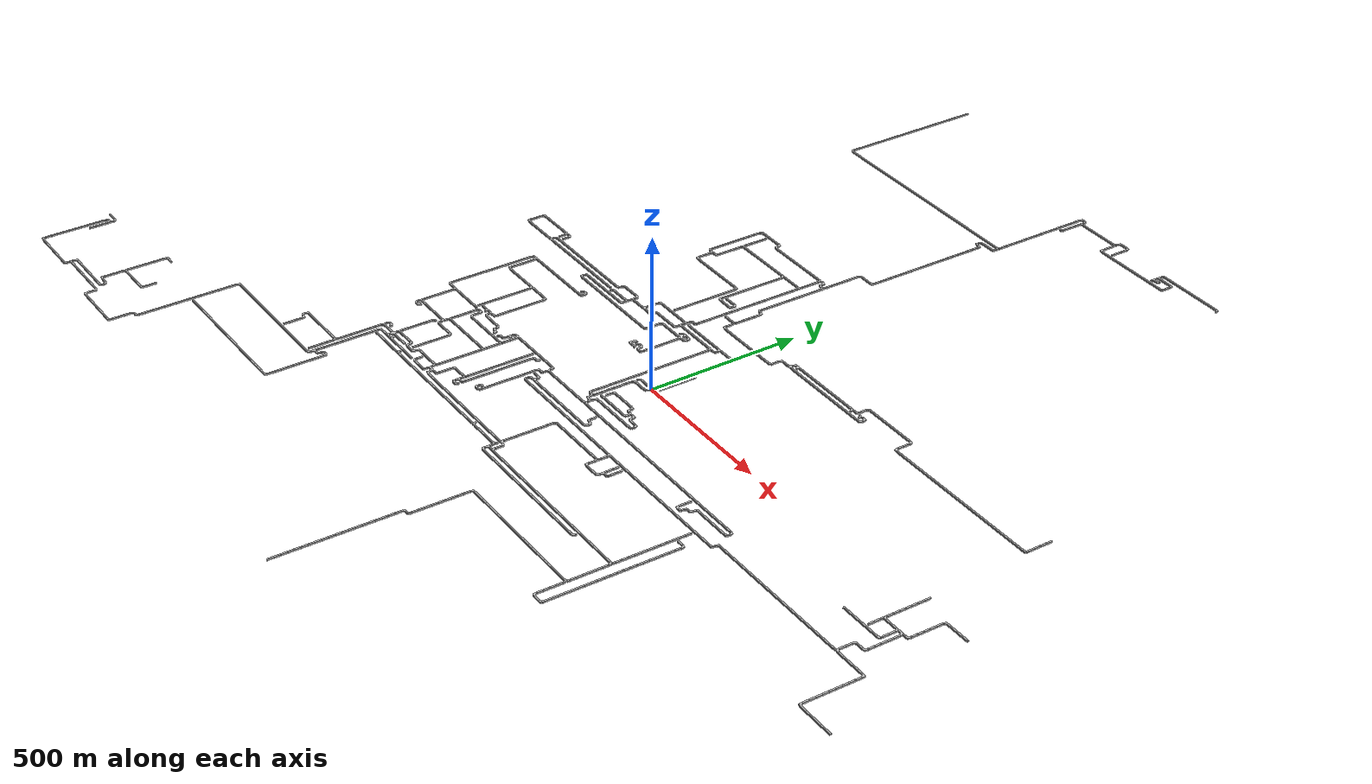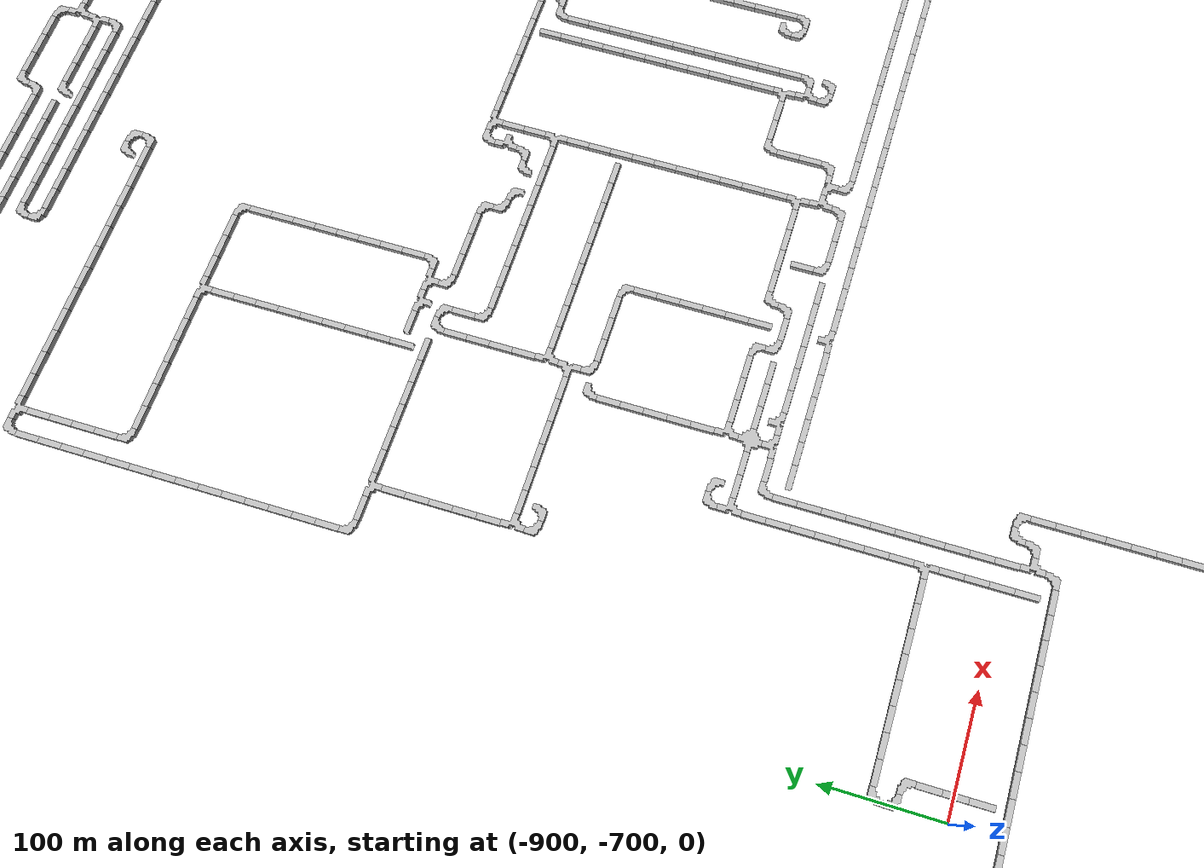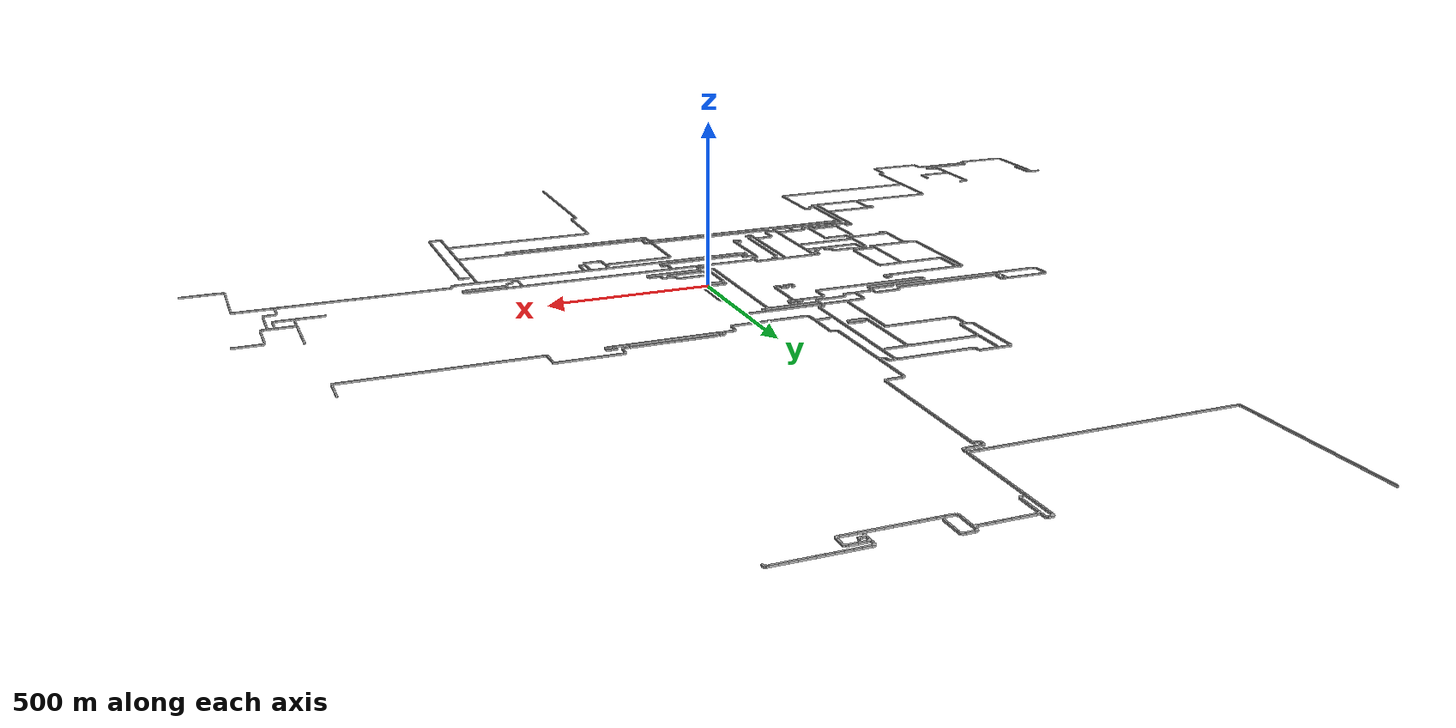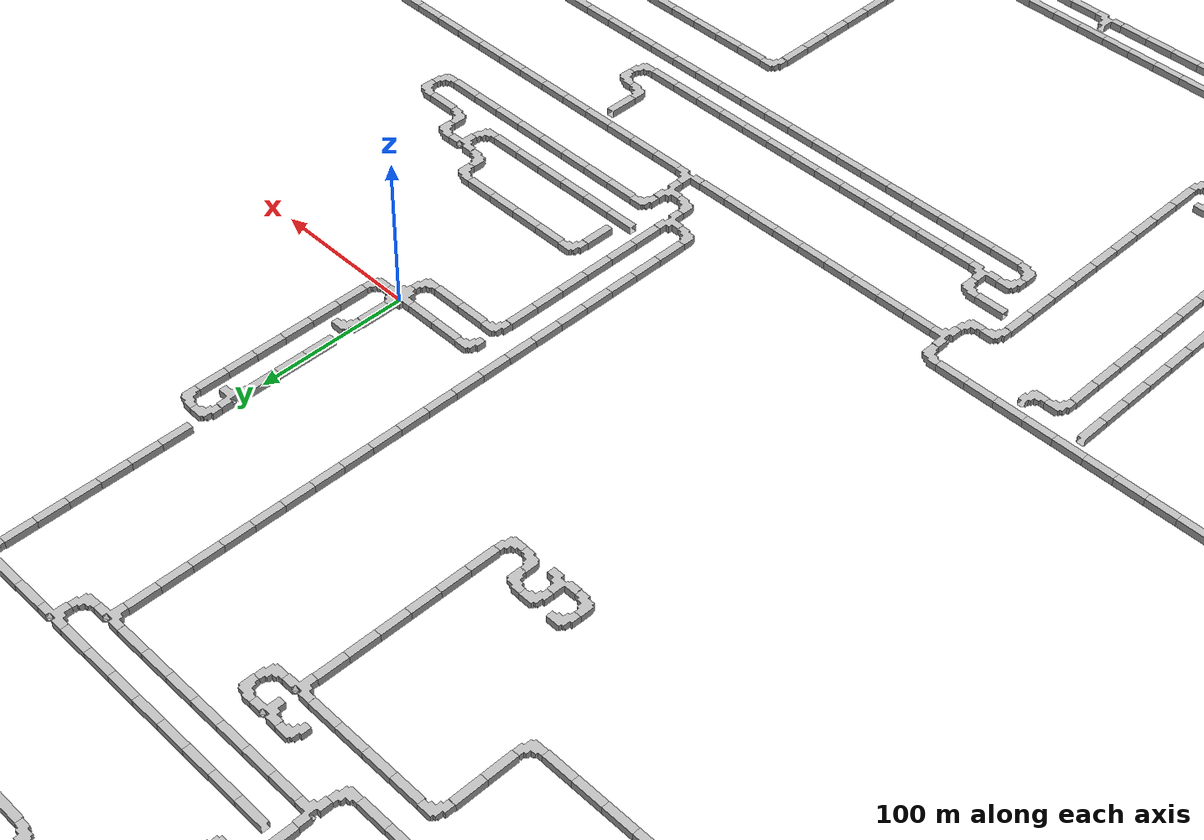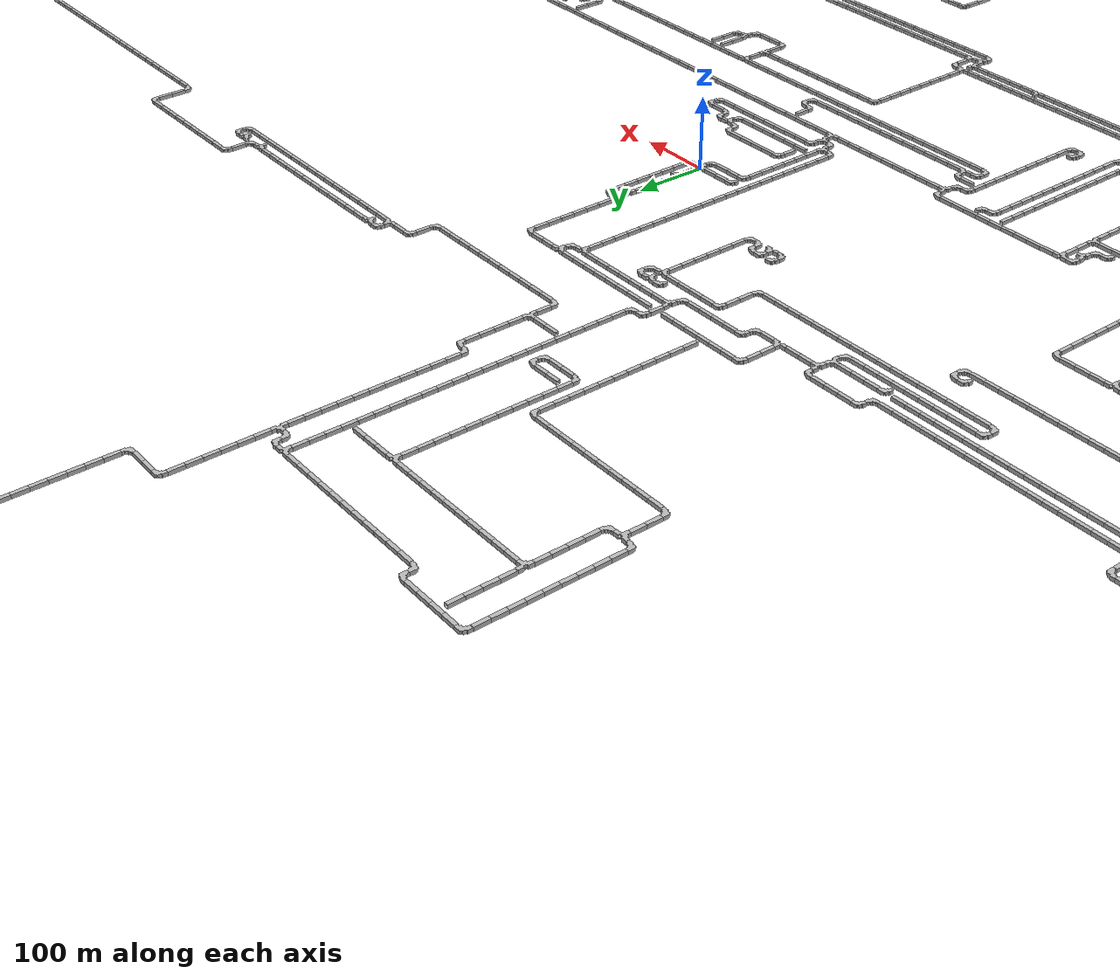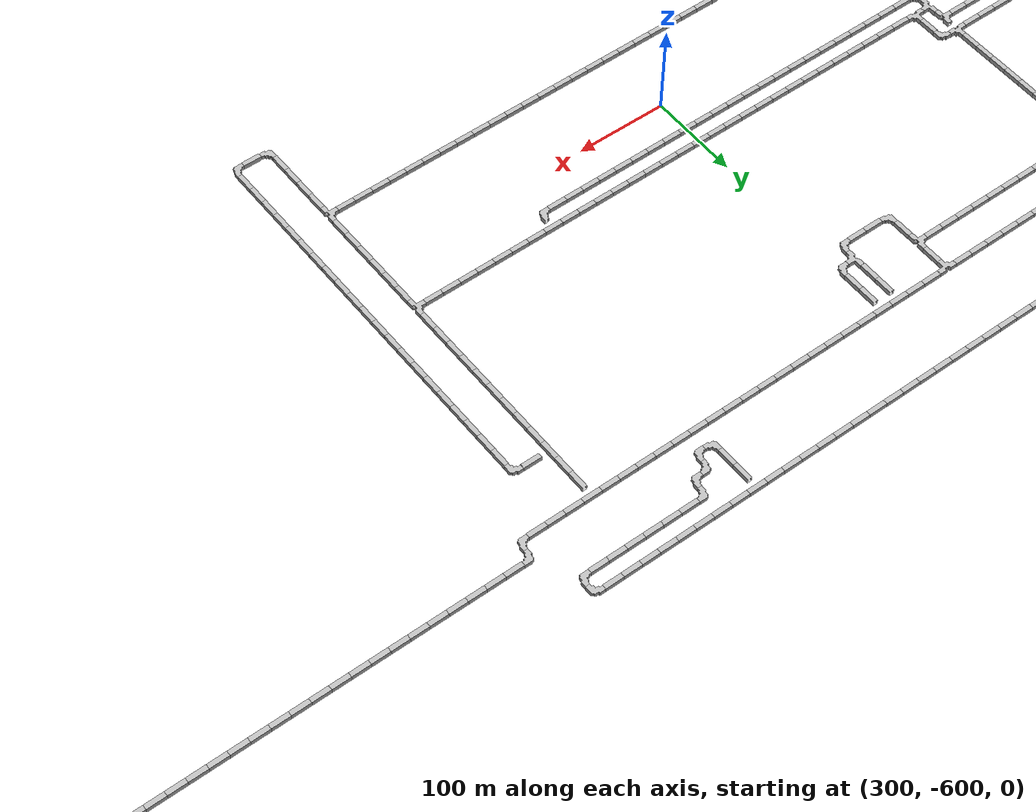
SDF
<sdf version="1.6">
 <world name="cave_32000_64">
  <include>
   <static>true</static>
   <name>cave_0_0</name>
   <pose>0 0 0 0 0 -1.5707963267948966</pose>
   <uri>model://cave_4way_20m</uri>
  </include>
  <include>
   <static>true</static>
   <name>cave_1_0</name>
   <pose>20 0 0 0 0 1.5707963267948966</pose>
   <uri>model://cave_L_20m</uri>
  </include>
  <include>
   <static>true</static>
   <name>cave_1_1</name>
   <pose>20 20 0 0 0 0.0</pose>
   <uri>model://cave_straight_20m</uri>
  </include>
  <include>
   <static>true</static>
   <name>cave_1_2</name>
   <pose>20 40 0 0 0 0.0</pose>
   <uri>model://cave_straight_20m</uri>
  </include>
  <include>
   <static>true</static>
   <name>cave_1_3</name>
   <pose>20 60 0 0 0 0.0</pose>
   <uri>model://cave_straight_20m</uri>
  </include>
  <include>
   <static>true</static>
   <name>cave_1_4</name>
   <pose>20 80 0 0 0 0.0</pose>
   <uri>model://cave_straight_20m</uri>
  </include>
  <include>
   <static>true</static>
   <name>cave_1_5</name>
   <pose>20 100 0 0 0 0.0</pose>
   <uri>model://cave_straight_20m</uri>
  </include>
  <include>
   <static>true</static>
   <name>cave_1_6</name>
   <pose>20 120 0 0 0 0.0</pose>
   <uri>model://cave_straight_20m</uri>
  </include>
  <include>
   <static>true</static>
   <name>cave_1_7</name>
   <pose>20 140 0 0 0 3.141592653589793</pose>
   <uri>model://cave_L_20m</uri>
  </include>
  <include>
   <static>true</static>
   <name>cave_0_7</name>
   <pose>0 140 0 0 0 -1.5707963267948966</pose>
   <uri>model://cave_L_20m</uri>
  </include>
  <include>
   <static>true</static>
   <name>cave_0_6</name>
   <pose>0 120 0 0 0 -1.5707963267948966</pose>
   <uri>model://cave_3way_20m</uri>
  </include>
  <include>
   <static>true</static>
   <name>cave_0_5</name>
   <pose>0 100 0 0 0 0.0</pose>
   <uri>model://cave_straight_20m</uri>
  </include>
  <include>
   <static>true</static>
   <name>cave_0_4</name>
   <pose>0 80 0 0 0 0.0</pose>
   <uri>model://cave_straight_20m</uri>
  </include>
  <include>
   <static>true</static>
   <name>cave_0_3</name>
   <pose>0 60 0 0 0 0.0</pose>
   <uri>model://cave_straight_20m</uri>
  </include>
  <include>
   <static>true</static>
   <name>cave_0_-1</name>
   <pose>0 -20 0 0 0 1.5707963267948966</pose>
   <uri>model://cave_L_20m</uri>
  </include>
  <include>
   <static>true</static>
   <name>cave_-1_-1</name>
   <pose>-20 -20 0 0 0 1.5707963267948966</pose>
   <uri>model://cave_straight_20m</uri>
  </include>
  <include>
   <static>true</static>
   <name>cave_-2_-1</name>
   <pose>-40 -20 0 0 0 1.5707963267948966</pose>
   <uri>model://cave_straight_20m</uri>
  </include>
  <include>
   <static>true</static>
   <name>cave_-3_-1</name>
   <pose>-60 -20 0 0 0 -1.5707963267948966</pose>
   <uri>model://cave_L_20m</uri>
  </include>
  <include>
   <static>true</static>
   <name>cave_-3_-2</name>
   <pose>-60 -40 0 0 0 0.0</pose>
   <uri>model://cave_straight_20m</uri>
  </include>
  <include>
   <static>true</static>
   <name>cave_-3_-3</name>
   <pose>-60 -60 0 0 0 0.0</pose>
   <uri>model://cave_straight_20m</uri>
  </include>
  <include>
   <static>true</static>
   <name>cave_-3_-4</name>
   <pose>-60 -80 0 0 0 0.0</pose>
   <uri>model://cave_straight_20m</uri>
  </include>
  <include>
   <static>true</static>
   <name>cave_-3_-5</name>
   <pose>-60 -100 0 0 0 0.0</pose>
   <uri>model://cave_straight_20m</uri>
  </include>
  <include>
   <static>true</static>
   <name>cave_-3_-6</name>
   <pose>-60 -120 0 0 0 0.0</pose>
   <uri>model://cave_straight_20m</uri>
  </include>
  <include>
   <static>true</static>
   <name>cave_-3_-7</name>
   <pose>-60 -140 0 0 0 0.0</pose>
   <uri>model://cave_straight_20m</uri>
  </include>
  <include>
   <static>true</static>
   <name>cave_-3_-8</name>
   <pose>-60 -160 0 0 0 1.5707963267948966</pose>
   <uri>model://cave_3way_20m</uri>
  </include>
  <include>
   <static>true</static>
   <name>cave_-3_-9</name>
   <pose>-60 -180 0 0 0 0.0</pose>
   <uri>model://cave_L_20m</uri>
  </include>
  <include>
   <static>true</static>
   <name>cave_-2_-9</name>
   <pose>-40 -180 0 0 0 1.5707963267948966</pose>
   <uri>model://cave_3way_20m</uri>
  </include>
  <include>
   <static>true</static>
   <name>cave_-2_-10</name>
   <pose>-40 -200 0 0 0 0.0</pose>
   <uri>model://cave_3way_20m</uri>
  </include>
  <include>
   <static>true</static>
   <name>cave_-1_-10</name>
   <pose>-20 -200 0 0 0 1.5707963267948966</pose>
   <uri>model://cave_straight_20m</uri>
  </include>
  <include>
   <static>true</static>
   <name>cave_0_-10</name>
   <pose>0 -200 0 0 0 1.5707963267948966</pose>
   <uri>model://cave_straight_20m</uri>
  </include>
  <include>
   <static>true</static>
   <name>cave_1_-10</name>
   <pose>20 -200 0 0 0 1.5707963267948966</pose>
   <uri>model://cave_straight_20m</uri>
  </include>
  <include>
   <static>true</static>
   <name>cave_2_-10</name>
   <pose>40 -200 0 0 0 1.5707963267948966</pose>
   <uri>model://cave_straight_20m</uri>
  </include>
  <include>
   <static>true</static>
   <name>cave_3_-10</name>
   <pose>60 -200 0 0 0 1.5707963267948966</pose>
   <uri>model://cave_straight_20m</uri>
  </include>
  <include>
   <static>true</static>
   <name>cave_4_-10</name>
   <pose>80 -200 0 0 0 1.5707963267948966</pose>
   <uri>model://cave_straight_20m</uri>
  </include>
  <include>
   <static>true</static>
   <name>cave_5_-10</name>
   <pose>100 -200 0 0 0 1.5707963267948966</pose>
   <uri>model://cave_straight_20m</uri>
  </include>
  <include>
   <static>true</static>
   <name>cave_6_-10</name>
   <pose>120 -200 0 0 0 1.5707963267948966</pose>
   <uri>model://cave_straight_20m</uri>
  </include>
  <include>
   <static>true</static>
   <name>cave_7_-10</name>
   <pose>140 -200 0 0 0 1.5707963267948966</pose>
   <uri>model://cave_straight_20m</uri>
  </include>
  <include>
   <static>true</static>
   <name>cave_8_-10</name>
   <pose>160 -200 0 0 0 1.5707963267948966</pose>
   <uri>model://cave_straight_20m</uri>
  </include>
  <include>
   <static>true</static>
   <name>cave_9_-10</name>
   <pose>180 -200 0 0 0 1.5707963267948966</pose>
   <uri>model://cave_straight_20m</uri>
  </include>
  <include>
   <static>true</static>
   <name>cave_10_-10</name>
   <pose>200 -200 0 0 0 1.5707963267948966</pose>
   <uri>model://cave_straight_20m</uri>
  </include>
  <include>
   <static>true</static>
   <name>cave_11_-10</name>
   <pose>220 -200 0 0 0 1.5707963267948966</pose>
   <uri>model://cave_straight_20m</uri>
  </include>
  <include>
   <static>true</static>
   <name>cave_12_-10</name>
   <pose>240 -200 0 0 0 1.5707963267948966</pose>
   <uri>model://cave_straight_20m</uri>
  </include>
  <include>
   <static>true</static>
   <name>cave_13_-10</name>
   <pose>260 -200 0 0 0 1.5707963267948966</pose>
   <uri>model://cave_straight_20m</uri>
  </include>
  <include>
   <static>true</static>
   <name>cave_14_-10</name>
   <pose>280 -200 0 0 0 1.5707963267948966</pose>
   <uri>model://cave_straight_20m</uri>
  </include>
  <include>
   <static>true</static>
   <name>cave_15_-10</name>
   <pose>300 -200 0 0 0 1.5707963267948966</pose>
   <uri>model://cave_straight_20m</uri>
  </include>
  <include>
   <static>true</static>
   <name>cave_16_-10</name>
   <pose>320 -200 0 0 0 1.5707963267948966</pose>
   <uri>model://cave_straight_20m</uri>
  </include>
  <include>
   <static>true</static>
   <name>cave_17_-10</name>
   <pose>340 -200 0 0 0 1.5707963267948966</pose>
   <uri>model://cave_straight_20m</uri>
  </include>
  <include>
   <static>true</static>
   <name>cave_18_-10</name>
   <pose>360 -200 0 0 0 1.5707963267948966</pose>
   <uri>model://cave_straight_20m</uri>
  </include>
  <include>
   <static>true</static>
   <name>cave_19_-10</name>
   <pose>380 -200 0 0 0 1.5707963267948966</pose>
   <uri>model://cave_straight_20m</uri>
  </include>
  <include>
   <static>true</static>
   <name>cave_20_-10</name>
   <pose>400 -200 0 0 0 1.5707963267948966</pose>
   <uri>model://cave_straight_20m</uri>
  </include>
  <include>
   <static>true</static>
   <name>cave_21_-10</name>
   <pose>420 -200 0 0 0 1.5707963267948966</pose>
   <uri>model://cave_straight_20m</uri>
  </include>
  <include>
   <static>true</static>
   <name>cave_22_-10</name>
   <pose>440 -200 0 0 0 1.5707963267948966</pose>
   <uri>model://cave_straight_20m</uri>
  </include>
  <include>
   <static>true</static>
   <name>cave_23_-10</name>
   <pose>460 -200 0 0 0 1.5707963267948966</pose>
   <uri>model://cave_straight_20m</uri>
  </include>
  <include>
   <static>true</static>
   <name>cave_24_-10</name>
   <pose>480 -200 0 0 0 1.5707963267948966</pose>
   <uri>model://cave_straight_20m</uri>
  </include>
  <include>
   <static>true</static>
   <name>cave_25_-10</name>
   <pose>500 -200 0 0 0 1.5707963267948966</pose>
   <uri>model://cave_straight_20m</uri>
  </include>
  <include>
   <static>true</static>
   <name>cave_26_-10</name>
   <pose>520 -200 0 0 0 1.5707963267948966</pose>
   <uri>model://cave_straight_20m</uri>
  </include>
  <include>
   <static>true</static>
   <name>cave_27_-10</name>
   <pose>540 -200 0 0 0 1.5707963267948966</pose>
   <uri>model://cave_straight_20m</uri>
  </include>
  <include>
   <static>true</static>
   <name>cave_28_-10</name>
   <pose>560 -200 0 0 0 1.5707963267948966</pose>
   <uri>model://cave_straight_20m</uri>
  </include>
  <include>
   <static>true</static>
   <name>cave_29_-10</name>
   <pose>580 -200 0 0 0 1.5707963267948966</pose>
   <uri>model://cave_straight_20m</uri>
  </include>
  <include>
   <static>true</static>
   <name>cave_30_-10</name>
   <pose>600 -200 0 0 0 1.5707963267948966</pose>
   <uri>model://cave_straight_20m</uri>
  </include>
  <include>
   <static>true</static>
   <name>cave_31_-10</name>
   <pose>620 -200 0 0 0 1.5707963267948966</pose>
   <uri>model://cave_straight_20m</uri>
  </include>
  <include>
   <static>true</static>
   <name>cave_32_-10</name>
   <pose>640 -200 0 0 0 1.5707963267948966</pose>
   <uri>model://cave_straight_20m</uri>
  </include>
  <include>
   <static>true</static>
   <name>cave_33_-10</name>
   <pose>660 -200 0 0 0 1.5707963267948966</pose>
   <uri>model://cave_straight_20m</uri>
  </include>
  <include>
   <static>true</static>
   <name>cave_34_-10</name>
   <pose>680 -200 0 0 0 1.5707963267948966</pose>
   <uri>model://cave_straight_20m</uri>
  </include>
  <include>
   <static>true</static>
   <name>cave_35_-10</name>
   <pose>700 -200 0 0 0 3.141592653589793</pose>
   <uri>model://cave_L_20m</uri>
  </include>
  <include>
   <static>true</static>
   <name>cave_35_-11</name>
   <pose>700 -220 0 0 0 1.5707963267948966</pose>
   <uri>model://cave_L_20m</uri>
  </include>
  <include>
   <static>true</static>
   <name>cave_34_-11</name>
   <pose>680 -220 0 0 0 1.5707963267948966</pose>
   <uri>model://cave_straight_20m</uri>
  </include>
  <include>
   <static>true</static>
   <name>cave_33_-11</name>
   <pose>660 -220 0 0 0 1.5707963267948966</pose>
   <uri>model://cave_straight_20m</uri>
  </include>
  <include>
   <static>true</static>
   <name>cave_32_-11</name>
   <pose>640 -220 0 0 0 1.5707963267948966</pose>
   <uri>model://cave_straight_20m</uri>
  </include>
  <include>
   <static>true</static>
   <name>cave_31_-11</name>
   <pose>620 -220 0 0 0 1.5707963267948966</pose>
   <uri>model://cave_straight_20m</uri>
  </include>
  <include>
   <static>true</static>
   <name>cave_30_-11</name>
   <pose>600 -220 0 0 0 1.5707963267948966</pose>
   <uri>model://cave_straight_20m</uri>
  </include>
  <include>
   <static>true</static>
   <name>cave_29_-11</name>
   <pose>580 -220 0 0 0 1.5707963267948966</pose>
   <uri>model://cave_straight_20m</uri>
  </include>
  <include>
   <static>true</static>
   <name>cave_28_-11</name>
   <pose>560 -220 0 0 0 -1.5707963267948966</pose>
   <uri>model://cave_L_20m</uri>
  </include>
  <include>
   <static>true</static>
   <name>cave_28_-12</name>
   <pose>560 -240 0 0 0 1.5707963267948966</pose>
   <uri>model://cave_L_20m</uri>
  </include>
  <include>
   <static>true</static>
   <name>cave_27_-12</name>
   <pose>540 -240 0 0 0 -1.5707963267948966</pose>
   <uri>model://cave_L_20m</uri>
  </include>
  <include>
   <static>true</static>
   <name>cave_27_-13</name>
   <pose>540 -260 0 0 0 1.5707963267948966</pose>
   <uri>model://cave_L_20m</uri>
  </include>
  <include>
   <static>true</static>
   <name>cave_26_-13</name>
   <pose>520 -260 0 0 0 0.0</pose>
   <uri>model://cave_L_20m</uri>
  </include>
  <include>
   <static>true</static>
   <name>cave_26_-12</name>
   <pose>520 -240 0 0 0 0.0</pose>
   <uri>model://cave_straight_20m</uri>
  </include>
  <include>
   <static>true</static>
   <name>cave_26_-11</name>
   <pose>520 -220 0 0 0 0.0</pose>
   <uri>model://cave_straight_20m</uri>
  </include>
  <include>
   <static>true</static>
   <name>cave_-3_-10</name>
   <pose>-60 -200 0 0 0 1.5707963267948966</pose>
   <uri>model://cave_straight_20m</uri>
  </include>
  <include>
   <static>true</static>
   <name>cave_-4_-10</name>
   <pose>-80 -200 0 0 0 1.5707963267948966</pose>
   <uri>model://cave_straight_20m</uri>
  </include>
  <include>
   <static>true</static>
   <name>cave_-5_-10</name>
   <pose>-100 -200 0 0 0 1.5707963267948966</pose>
   <uri>model://cave_straight_20m</uri>
  </include>
  <include>
   <static>true</static>
   <name>cave_-6_-10</name>
   <pose>-120 -200 0 0 0 1.5707963267948966</pose>
   <uri>model://cave_straight_20m</uri>
  </include>
  <include>
   <static>true</static>
   <name>cave_-7_-10</name>
   <pose>-140 -200 0 0 0 1.5707963267948966</pose>
   <uri>model://cave_straight_20m</uri>
  </include>
  <include>
   <static>true</static>
   <name>cave_-8_-10</name>
   <pose>-160 -200 0 0 0 1.5707963267948966</pose>
   <uri>model://cave_straight_20m</uri>
  </include>
  <include>
   <static>true</static>
   <name>cave_-9_-10</name>
   <pose>-180 -200 0 0 0 1.5707963267948966</pose>
   <uri>model://cave_straight_20m</uri>
  </include>
  <include>
   <static>true</static>
   <name>cave_-10_-10</name>
   <pose>-200 -200 0 0 0 1.5707963267948966</pose>
   <uri>model://cave_straight_20m</uri>
  </include>
  <include>
   <static>true</static>
   <name>cave_-11_-10</name>
   <pose>-220 -200 0 0 0 1.5707963267948966</pose>
   <uri>model://cave_straight_20m</uri>
  </include>
  <include>
   <static>true</static>
   <name>cave_-12_-10</name>
   <pose>-240 -200 0 0 0 -1.5707963267948966</pose>
   <uri>model://cave_3way_20m</uri>
  </include>
  <include>
   <static>true</static>
   <name>cave_-12_-11</name>
   <pose>-240 -220 0 0 0 1.5707963267948966</pose>
   <uri>model://cave_L_20m</uri>
  </include>
  <include>
   <static>true</static>
   <name>cave_-13_-11</name>
   <pose>-260 -220 0 0 0 -1.5707963267948966</pose>
   <uri>model://cave_L_20m</uri>
  </include>
  <include>
   <static>true</static>
   <name>cave_-13_-12</name>
   <pose>-260 -240 0 0 0 0.0</pose>
   <uri>model://cave_straight_20m</uri>
  </include>
  <include>
   <static>true</static>
   <name>cave_-13_-13</name>
   <pose>-260 -260 0 0 0 0.0</pose>
   <uri>model://cave_straight_20m</uri>
  </include>
  <include>
   <static>true</static>
   <name>cave_-13_-14</name>
   <pose>-260 -280 0 0 0 0.0</pose>
   <uri>model://cave_straight_20m</uri>
  </include>
  <include>
   <static>true</static>
   <name>cave_-13_-15</name>
   <pose>-260 -300 0 0 0 0.0</pose>
   <uri>model://cave_straight_20m</uri>
  </include>
  <include>
   <static>true</static>
   <name>cave_-13_-16</name>
   <pose>-260 -320 0 0 0 0.0</pose>
   <uri>model://cave_straight_20m</uri>
  </include>
  <include>
   <static>true</static>
   <name>cave_-13_-17</name>
   <pose>-260 -340 0 0 0 0.0</pose>
   <uri>model://cave_straight_20m</uri>
  </include>
  <include>
   <static>true</static>
   <name>cave_-13_-18</name>
   <pose>-260 -360 0 0 0 0.0</pose>
   <uri>model://cave_straight_20m</uri>
  </include>
  <include>
   <static>true</static>
   <name>cave_-13_-19</name>
   <pose>-260 -380 0 0 0 0.0</pose>
   <uri>model://cave_straight_20m</uri>
  </include>
  <include>
   <static>true</static>
   <name>cave_-13_-20</name>
   <pose>-260 -400 0 0 0 0.0</pose>
   <uri>model://cave_straight_20m</uri>
  </include>
  <include>
   <static>true</static>
   <name>cave_-13_-21</name>
   <pose>-260 -420 0 0 0 1.5707963267948966</pose>
   <uri>model://cave_L_20m</uri>
  </include>
  <include>
   <static>true</static>
   <name>cave_-14_-21</name>
   <pose>-280 -420 0 0 0 0.0</pose>
   <uri>model://cave_L_20m</uri>
  </include>
  <include>
   <static>true</static>
   <name>cave_-14_-20</name>
   <pose>-280 -400 0 0 0 -1.5707963267948966</pose>
   <uri>model://cave_L_20m</uri>
  </include>
  <include>
   <static>true</static>
   <name>cave_-12_-9</name>
   <pose>-240 -180 0 0 0 3.141592653589793</pose>
   <uri>model://cave_L_20m</uri>
  </include>
  <include>
   <static>true</static>
   <name>cave_-13_-9</name>
   <pose>-260 -180 0 0 0 1.5707963267948966</pose>
   <uri>model://cave_straight_20m</uri>
  </include>
  <include>
   <static>true</static>
   <name>cave_-14_-9</name>
   <pose>-280 -180 0 0 0 1.5707963267948966</pose>
   <uri>model://cave_straight_20m</uri>
  </include>
  <include>
   <static>true</static>
   <name>cave_-15_-9</name>
   <pose>-300 -180 0 0 0 1.5707963267948966</pose>
   <uri>model://cave_straight_20m</uri>
  </include>
  <include>
   <static>true</static>
   <name>cave_-16_-9</name>
   <pose>-320 -180 0 0 0 1.5707963267948966</pose>
   <uri>model://cave_straight_20m</uri>
  </include>
  <include>
   <static>true</static>
   <name>cave_-17_-9</name>
   <pose>-340 -180 0 0 0 1.5707963267948966</pose>
   <uri>model://cave_straight_20m</uri>
  </include>
  <include>
   <static>true</static>
   <name>cave_-18_-9</name>
   <pose>-360 -180 0 0 0 1.5707963267948966</pose>
   <uri>model://cave_straight_20m</uri>
  </include>
  <include>
   <static>true</static>
   <name>cave_-19_-9</name>
   <pose>-380 -180 0 0 0 1.5707963267948966</pose>
   <uri>model://cave_straight_20m</uri>
  </include>
  <include>
   <static>true</static>
   <name>cave_-20_-9</name>
   <pose>-400 -180 0 0 0 1.5707963267948966</pose>
   <uri>model://cave_straight_20m</uri>
  </include>
  <include>
   <static>true</static>
   <name>cave_-21_-9</name>
   <pose>-420 -180 0 0 0 1.5707963267948966</pose>
   <uri>model://cave_straight_20m</uri>
  </include>
  <include>
   <static>true</static>
   <name>cave_-22_-9</name>
   <pose>-440 -180 0 0 0 3.141592653589793</pose>
   <uri>model://cave_3way_20m</uri>
  </include>
  <include>
   <static>true</static>
   <name>cave_-22_-10</name>
   <pose>-440 -200 0 0 0 0.0</pose>
   <uri>model://cave_straight_20m</uri>
  </include>
  <include>
   <static>true</static>
   <name>cave_-22_-11</name>
   <pose>-440 -220 0 0 0 0.0</pose>
   <uri>model://cave_straight_20m</uri>
  </include>
  <include>
   <static>true</static>
   <name>cave_-22_-12</name>
   <pose>-440 -240 0 0 0 1.5707963267948966</pose>
   <uri>model://cave_3way_20m</uri>
  </include>
  <include>
   <static>true</static>
   <name>cave_-22_-13</name>
   <pose>-440 -260 0 0 0 0.0</pose>
   <uri>model://cave_straight_20m</uri>
  </include>
  <include>
   <static>true</static>
   <name>cave_-22_-14</name>
   <pose>-440 -280 0 0 0 0.0</pose>
   <uri>model://cave_straight_20m</uri>
  </include>
  <include>
   <static>true</static>
   <name>cave_-22_-15</name>
   <pose>-440 -300 0 0 0 0.0</pose>
   <uri>model://cave_straight_20m</uri>
  </include>
  <include>
   <static>true</static>
   <name>cave_-22_-16</name>
   <pose>-440 -320 0 0 0 0.0</pose>
   <uri>model://cave_straight_20m</uri>
  </include>
  <include>
   <static>true</static>
   <name>cave_-22_-17</name>
   <pose>-440 -340 0 0 0 0.0</pose>
   <uri>model://cave_straight_20m</uri>
  </include>
  <include>
   <static>true</static>
   <name>cave_-22_-18</name>
   <pose>-440 -360 0 0 0 0.0</pose>
   <uri>model://cave_straight_20m</uri>
  </include>
  <include>
   <static>true</static>
   <name>cave_-22_-19</name>
   <pose>-440 -380 0 0 0 0.0</pose>
   <uri>model://cave_straight_20m</uri>
  </include>
  <include>
   <static>true</static>
   <name>cave_-22_-20</name>
   <pose>-440 -400 0 0 0 0.0</pose>
   <uri>model://cave_straight_20m</uri>
  </include>
  <include>
   <static>true</static>
   <name>cave_-22_-21</name>
   <pose>-440 -420 0 0 0 0.0</pose>
   <uri>model://cave_straight_20m</uri>
  </include>
  <include>
   <static>true</static>
   <name>cave_-22_-22</name>
   <pose>-440 -440 0 0 0 0.0</pose>
   <uri>model://cave_straight_20m</uri>
  </include>
  <include>
   <static>true</static>
   <name>cave_-22_-23</name>
   <pose>-440 -460 0 0 0 1.5707963267948966</pose>
   <uri>model://cave_3way_20m</uri>
  </include>
  <include>
   <static>true</static>
   <name>cave_-22_-24</name>
   <pose>-440 -480 0 0 0 -1.5707963267948966</pose>
   <uri>model://cave_3way_20m</uri>
  </include>
  <include>
   <static>true</static>
   <name>cave_-21_-24</name>
   <pose>-420 -480 0 0 0 3.141592653589793</pose>
   <uri>model://cave_3way_20m</uri>
  </include>
  <include>
   <static>true</static>
   <name>cave_-20_-24</name>
   <pose>-400 -480 0 0 0 1.5707963267948966</pose>
   <uri>model://cave_L_20m</uri>
  </include>
  <include>
   <static>true</static>
   <name>cave_-20_-23</name>
   <pose>-400 -460 0 0 0 0.0</pose>
   <uri>model://cave_straight_20m</uri>
  </include>
  <include>
   <static>true</static>
   <name>cave_-20_-22</name>
   <pose>-400 -440 0 0 0 0.0</pose>
   <uri>model://cave_straight_20m</uri>
  </include>
  <include>
   <static>true</static>
   <name>cave_-20_-21</name>
   <pose>-400 -420 0 0 0 -1.5707963267948966</pose>
   <uri>model://cave_L_20m</uri>
  </include>
  <include>
   <static>true</static>
   <name>cave_-19_-21</name>
   <pose>-380 -420 0 0 0 1.5707963267948966</pose>
   <uri>model://cave_straight_20m</uri>
  </include>
  <include>
   <static>true</static>
   <name>cave_-18_-21</name>
   <pose>-360 -420 0 0 0 1.5707963267948966</pose>
   <uri>model://cave_straight_20m</uri>
  </include>
  <include>
   <static>true</static>
   <name>cave_-17_-21</name>
   <pose>-340 -420 0 0 0 1.5707963267948966</pose>
   <uri>model://cave_3way_20m</uri>
  </include>
  <include>
   <static>true</static>
   <name>cave_-17_-22</name>
   <pose>-340 -440 0 0 0 -1.5707963267948966</pose>
   <uri>model://cave_3way_20m</uri>
  </include>
  <include>
   <static>true</static>
   <name>cave_-16_-22</name>
   <pose>-320 -440 0 0 0 1.5707963267948966</pose>
   <uri>model://cave_L_20m</uri>
  </include>
  <include>
   <static>true</static>
   <name>cave_-16_-21</name>
   <pose>-320 -420 0 0 0 0.0</pose>
   <uri>model://cave_straight_20m</uri>
  </include>
  <include>
   <static>true</static>
   <name>cave_-16_-20</name>
   <pose>-320 -400 0 0 0 0.0</pose>
   <uri>model://cave_straight_20m</uri>
  </include>
  <include>
   <static>true</static>
   <name>cave_-16_-19</name>
   <pose>-320 -380 0 0 0 0.0</pose>
   <uri>model://cave_straight_20m</uri>
  </include>
  <include>
   <static>true</static>
   <name>cave_-16_-18</name>
   <pose>-320 -360 0 0 0 0.0</pose>
   <uri>model://cave_straight_20m</uri>
  </include>
  <include>
   <static>true</static>
   <name>cave_-16_-17</name>
   <pose>-320 -340 0 0 0 0.0</pose>
   <uri>model://cave_straight_20m</uri>
  </include>
  <include>
   <static>true</static>
   <name>cave_-16_-16</name>
   <pose>-320 -320 0 0 0 0.0</pose>
   <uri>model://cave_straight_20m</uri>
  </include>
  <include>
   <static>true</static>
   <name>cave_-16_-15</name>
   <pose>-320 -300 0 0 0 0.0</pose>
   <uri>model://cave_straight_20m</uri>
  </include>
  <include>
   <static>true</static>
   <name>cave_-16_-14</name>
   <pose>-320 -280 0 0 0 0.0</pose>
   <uri>model://cave_straight_20m</uri>
  </include>
  <include>
   <static>true</static>
   <name>cave_-16_-13</name>
   <pose>-320 -260 0 0 0 0.0</pose>
   <uri>model://cave_straight_20m</uri>
  </include>
  <include>
   <static>true</static>
   <name>cave_-16_-12</name>
   <pose>-320 -240 0 0 0 0.0</pose>
   <uri>model://cave_straight_20m</uri>
  </include>
  <include>
   <static>true</static>
   <name>cave_-16_-11</name>
   <pose>-320 -220 0 0 0 0.0</pose>
   <uri>model://cave_straight_20m</uri>
  </include>
  <include>
   <static>true</static>
   <name>cave_-16_-10</name>
   <pose>-320 -200 0 0 0 -1.5707963267948966</pose>
   <uri>model://cave_L_20m</uri>
  </include>
  <include>
   <static>true</static>
   <name>cave_-15_-10</name>
   <pose>-300 -200 0 0 0 1.5707963267948966</pose>
   <uri>model://cave_L_20m</uri>
  </include>
  <include>
   <static>true</static>
   <name>cave_-17_-23</name>
   <pose>-340 -460 0 0 0 0.0</pose>
   <uri>model://cave_L_20m</uri>
  </include>
  <include>
   <static>true</static>
   <name>cave_-16_-23</name>
   <pose>-320 -460 0 0 0 1.5707963267948966</pose>
   <uri>model://cave_L_20m</uri>
  </include>
  <include>
   <static>true</static>
   <name>cave_-17_-20</name>
   <pose>-340 -400 0 0 0 0.0</pose>
   <uri>model://cave_straight_20m</uri>
  </include>
  <include>
   <static>true</static>
   <name>cave_-17_-19</name>
   <pose>-340 -380 0 0 0 0.0</pose>
   <uri>model://cave_straight_20m</uri>
  </include>
  <include>
   <static>true</static>
   <name>cave_-17_-18</name>
   <pose>-340 -360 0 0 0 0.0</pose>
   <uri>model://cave_straight_20m</uri>
  </include>
  <include>
   <static>true</static>
   <name>cave_-17_-17</name>
   <pose>-340 -340 0 0 0 0.0</pose>
   <uri>model://cave_straight_20m</uri>
  </include>
  <include>
   <static>true</static>
   <name>cave_-17_-16</name>
   <pose>-340 -320 0 0 0 0.0</pose>
   <uri>model://cave_straight_20m</uri>
  </include>
  <include>
   <static>true</static>
   <name>cave_-17_-15</name>
   <pose>-340 -300 0 0 0 0.0</pose>
   <uri>model://cave_straight_20m</uri>
  </include>
  <include>
   <static>true</static>
   <name>cave_-17_-14</name>
   <pose>-340 -280 0 0 0 0.0</pose>
   <uri>model://cave_straight_20m</uri>
  </include>
  <include>
   <static>true</static>
   <name>cave_-17_-13</name>
   <pose>-340 -260 0 0 0 0.0</pose>
   <uri>model://cave_straight_20m</uri>
  </include>
  <include>
   <static>true</static>
   <name>cave_-17_-12</name>
   <pose>-340 -240 0 0 0 0.0</pose>
   <uri>model://cave_straight_20m</uri>
  </include>
  <include>
   <static>true</static>
   <name>cave_-17_-11</name>
   <pose>-340 -220 0 0 0 0.0</pose>
   <uri>model://cave_straight_20m</uri>
  </include>
  <include>
   <static>true</static>
   <name>cave_-17_-10</name>
   <pose>-340 -200 0 0 0 0.0</pose>
   <uri>model://cave_straight_20m</uri>
  </include>
  <include>
   <static>true</static>
   <name>cave_-21_-25</name>
   <pose>-420 -500 0 0 0 0.0</pose>
   <uri>model://cave_L_20m</uri>
  </include>
  <include>
   <static>true</static>
   <name>cave_-20_-25</name>
   <pose>-400 -500 0 0 0 1.5707963267948966</pose>
   <uri>model://cave_straight_20m</uri>
  </include>
  <include>
   <static>true</static>
   <name>cave_-19_-25</name>
   <pose>-380 -500 0 0 0 1.5707963267948966</pose>
   <uri>model://cave_straight_20m</uri>
  </include>
  <include>
   <static>true</static>
   <name>cave_-18_-25</name>
   <pose>-360 -500 0 0 0 1.5707963267948966</pose>
   <uri>model://cave_straight_20m</uri>
  </include>
  <include>
   <static>true</static>
   <name>cave_-17_-25</name>
   <pose>-340 -500 0 0 0 1.5707963267948966</pose>
   <uri>model://cave_straight_20m</uri>
  </include>
  <include>
   <static>true</static>
   <name>cave_-16_-25</name>
   <pose>-320 -500 0 0 0 1.5707963267948966</pose>
   <uri>model://cave_straight_20m</uri>
  </include>
  <include>
   <static>true</static>
   <name>cave_-15_-25</name>
   <pose>-300 -500 0 0 0 1.5707963267948966</pose>
   <uri>model://cave_straight_20m</uri>
  </include>
  <include>
   <static>true</static>
   <name>cave_-14_-25</name>
   <pose>-280 -500 0 0 0 1.5707963267948966</pose>
   <uri>model://cave_straight_20m</uri>
  </include>
  <include>
   <static>true</static>
   <name>cave_-13_-25</name>
   <pose>-260 -500 0 0 0 1.5707963267948966</pose>
   <uri>model://cave_straight_20m</uri>
  </include>
  <include>
   <static>true</static>
   <name>cave_-12_-25</name>
   <pose>-240 -500 0 0 0 1.5707963267948966</pose>
   <uri>model://cave_straight_20m</uri>
  </include>
  <include>
   <static>true</static>
   <name>cave_-11_-25</name>
   <pose>-220 -500 0 0 0 1.5707963267948966</pose>
   <uri>model://cave_straight_20m</uri>
  </include>
  <include>
   <static>true</static>
   <name>cave_-10_-25</name>
   <pose>-200 -500 0 0 0 1.5707963267948966</pose>
   <uri>model://cave_straight_20m</uri>
  </include>
  <include>
   <static>true</static>
   <name>cave_-9_-25</name>
   <pose>-180 -500 0 0 0 1.5707963267948966</pose>
   <uri>model://cave_straight_20m</uri>
  </include>
  <include>
   <static>true</static>
   <name>cave_-8_-25</name>
   <pose>-160 -500 0 0 0 1.5707963267948966</pose>
   <uri>model://cave_straight_20m</uri>
  </include>
  <include>
   <static>true</static>
   <name>cave_-7_-25</name>
   <pose>-140 -500 0 0 0 1.5707963267948966</pose>
   <uri>model://cave_straight_20m</uri>
  </include>
  <include>
   <static>true</static>
   <name>cave_-6_-25</name>
   <pose>-120 -500 0 0 0 1.5707963267948966</pose>
   <uri>model://cave_straight_20m</uri>
  </include>
  <include>
   <static>true</static>
   <name>cave_-5_-25</name>
   <pose>-100 -500 0 0 0 1.5707963267948966</pose>
   <uri>model://cave_straight_20m</uri>
  </include>
  <include>
   <static>true</static>
   <name>cave_-4_-25</name>
   <pose>-80 -500 0 0 0 1.5707963267948966</pose>
   <uri>model://cave_straight_20m</uri>
  </include>
  <include>
   <static>true</static>
   <name>cave_-3_-25</name>
   <pose>-60 -500 0 0 0 1.5707963267948966</pose>
   <uri>model://cave_straight_20m</uri>
  </include>
  <include>
   <static>true</static>
   <name>cave_-2_-25</name>
   <pose>-40 -500 0 0 0 1.5707963267948966</pose>
   <uri>model://cave_straight_20m</uri>
  </include>
  <include>
   <static>true</static>
   <name>cave_-1_-25</name>
   <pose>-20 -500 0 0 0 1.5707963267948966</pose>
   <uri>model://cave_straight_20m</uri>
  </include>
  <include>
   <static>true</static>
   <name>cave_0_-25</name>
   <pose>0 -500 0 0 0 0.0</pose>
   <uri>model://cave_3way_20m</uri>
  </include>
  <include>
   <static>true</static>
   <name>cave_1_-25</name>
   <pose>20 -500 0 0 0 3.141592653589793</pose>
   <uri>model://cave_L_20m</uri>
  </include>
  <include>
   <static>true</static>
   <name>cave_1_-26</name>
   <pose>20 -520 0 0 0 0.0</pose>
   <uri>model://cave_straight_20m</uri>
  </include>
  <include>
   <static>true</static>
   <name>cave_1_-27</name>
   <pose>20 -540 0 0 0 0.0</pose>
   <uri>model://cave_3way_20m</uri>
  </include>
  <include>
   <static>true</static>
   <name>cave_2_-27</name>
   <pose>40 -540 0 0 0 1.5707963267948966</pose>
   <uri>model://cave_straight_20m</uri>
  </include>
  <include>
   <static>true</static>
   <name>cave_3_-27</name>
   <pose>60 -540 0 0 0 1.5707963267948966</pose>
   <uri>model://cave_straight_20m</uri>
  </include>
  <include>
   <static>true</static>
   <name>cave_4_-27</name>
   <pose>80 -540 0 0 0 1.5707963267948966</pose>
   <uri>model://cave_straight_20m</uri>
  </include>
  <include>
   <static>true</static>
   <name>cave_5_-27</name>
   <pose>100 -540 0 0 0 1.5707963267948966</pose>
   <uri>model://cave_straight_20m</uri>
  </include>
  <include>
   <static>true</static>
   <name>cave_6_-27</name>
   <pose>120 -540 0 0 0 1.5707963267948966</pose>
   <uri>model://cave_straight_20m</uri>
  </include>
  <include>
   <static>true</static>
   <name>cave_7_-27</name>
   <pose>140 -540 0 0 0 1.5707963267948966</pose>
   <uri>model://cave_straight_20m</uri>
  </include>
  <include>
   <static>true</static>
   <name>cave_8_-27</name>
   <pose>160 -540 0 0 0 1.5707963267948966</pose>
   <uri>model://cave_straight_20m</uri>
  </include>
  <include>
   <static>true</static>
   <name>cave_9_-27</name>
   <pose>180 -540 0 0 0 1.5707963267948966</pose>
   <uri>model://cave_straight_20m</uri>
  </include>
  <include>
   <static>true</static>
   <name>cave_10_-27</name>
   <pose>200 -540 0 0 0 1.5707963267948966</pose>
   <uri>model://cave_straight_20m</uri>
  </include>
  <include>
   <static>true</static>
   <name>cave_11_-27</name>
   <pose>220 -540 0 0 0 1.5707963267948966</pose>
   <uri>model://cave_straight_20m</uri>
  </include>
  <include>
   <static>true</static>
   <name>cave_12_-27</name>
   <pose>240 -540 0 0 0 1.5707963267948966</pose>
   <uri>model://cave_straight_20m</uri>
  </include>
  <include>
   <static>true</static>
   <name>cave_13_-27</name>
   <pose>260 -540 0 0 0 1.5707963267948966</pose>
   <uri>model://cave_straight_20m</uri>
  </include>
  <include>
   <static>true</static>
   <name>cave_14_-27</name>
   <pose>280 -540 0 0 0 1.5707963267948966</pose>
   <uri>model://cave_straight_20m</uri>
  </include>
  <include>
   <static>true</static>
   <name>cave_15_-27</name>
   <pose>300 -540 0 0 0 1.5707963267948966</pose>
   <uri>model://cave_straight_20m</uri>
  </include>
  <include>
   <static>true</static>
   <name>cave_16_-27</name>
   <pose>320 -540 0 0 0 1.5707963267948966</pose>
   <uri>model://cave_straight_20m</uri>
  </include>
  <include>
   <static>true</static>
   <name>cave_17_-27</name>
   <pose>340 -540 0 0 0 1.5707963267948966</pose>
   <uri>model://cave_straight_20m</uri>
  </include>
  <include>
   <static>true</static>
   <name>cave_18_-27</name>
   <pose>360 -540 0 0 0 1.5707963267948966</pose>
   <uri>model://cave_straight_20m</uri>
  </include>
  <include>
   <static>true</static>
   <name>cave_19_-27</name>
   <pose>380 -540 0 0 0 1.5707963267948966</pose>
   <uri>model://cave_straight_20m</uri>
  </include>
  <include>
   <static>true</static>
   <name>cave_20_-27</name>
   <pose>400 -540 0 0 0 1.5707963267948966</pose>
   <uri>model://cave_straight_20m</uri>
  </include>
  <include>
   <static>true</static>
   <name>cave_21_-27</name>
   <pose>420 -540 0 0 0 1.5707963267948966</pose>
   <uri>model://cave_straight_20m</uri>
  </include>
  <include>
   <static>true</static>
   <name>cave_22_-27</name>
   <pose>440 -540 0 0 0 1.5707963267948966</pose>
   <uri>model://cave_straight_20m</uri>
  </include>
  <include>
   <static>true</static>
   <name>cave_23_-27</name>
   <pose>460 -540 0 0 0 1.5707963267948966</pose>
   <uri>model://cave_straight_20m</uri>
  </include>
  <include>
   <static>true</static>
   <name>cave_24_-27</name>
   <pose>480 -540 0 0 0 1.5707963267948966</pose>
   <uri>model://cave_straight_20m</uri>
  </include>
  <include>
   <static>true</static>
   <name>cave_25_-27</name>
   <pose>500 -540 0 0 0 1.5707963267948966</pose>
   <uri>model://cave_straight_20m</uri>
  </include>
  <include>
   <static>true</static>
   <name>cave_26_-27</name>
   <pose>520 -540 0 0 0 1.5707963267948966</pose>
   <uri>model://cave_straight_20m</uri>
  </include>
  <include>
   <static>true</static>
   <name>cave_27_-27</name>
   <pose>540 -540 0 0 0 1.5707963267948966</pose>
   <uri>model://cave_straight_20m</uri>
  </include>
  <include>
   <static>true</static>
   <name>cave_28_-27</name>
   <pose>560 -540 0 0 0 1.5707963267948966</pose>
   <uri>model://cave_straight_20m</uri>
  </include>
  <include>
   <static>true</static>
   <name>cave_29_-27</name>
   <pose>580 -540 0 0 0 1.5707963267948966</pose>
   <uri>model://cave_straight_20m</uri>
  </include>
  <include>
   <static>true</static>
   <name>cave_30_-27</name>
   <pose>600 -540 0 0 0 1.5707963267948966</pose>
   <uri>model://cave_straight_20m</uri>
  </include>
  <include>
   <static>true</static>
   <name>cave_31_-27</name>
   <pose>620 -540 0 0 0 1.5707963267948966</pose>
   <uri>model://cave_straight_20m</uri>
  </include>
  <include>
   <static>true</static>
   <name>cave_32_-27</name>
   <pose>640 -540 0 0 0 1.5707963267948966</pose>
   <uri>model://cave_3way_20m</uri>
  </include>
  <include>
   <static>true</static>
   <name>cave_32_-28</name>
   <pose>640 -560 0 0 0 0.0</pose>
   <uri>model://cave_straight_20m</uri>
  </include>
  <include>
   <static>true</static>
   <name>cave_32_-29</name>
   <pose>640 -580 0 0 0 0.0</pose>
   <uri>model://cave_straight_20m</uri>
  </include>
  <include>
   <static>true</static>
   <name>cave_32_-30</name>
   <pose>640 -600 0 0 0 0.0</pose>
   <uri>model://cave_straight_20m</uri>
  </include>
  <include>
   <static>true</static>
   <name>cave_32_-31</name>
   <pose>640 -620 0 0 0 0.0</pose>
   <uri>model://cave_straight_20m</uri>
  </include>
  <include>
   <static>true</static>
   <name>cave_32_-32</name>
   <pose>640 -640 0 0 0 0.0</pose>
   <uri>model://cave_straight_20m</uri>
  </include>
  <include>
   <static>true</static>
   <name>cave_32_-33</name>
   <pose>640 -660 0 0 0 0.0</pose>
   <uri>model://cave_straight_20m</uri>
  </include>
  <include>
   <static>true</static>
   <name>cave_32_-34</name>
   <pose>640 -680 0 0 0 1.5707963267948966</pose>
   <uri>model://cave_3way_20m</uri>
  </include>
  <include>
   <static>true</static>
   <name>cave_32_-35</name>
   <pose>640 -700 0 0 0 0.0</pose>
   <uri>model://cave_straight_20m</uri>
  </include>
  <include>
   <static>true</static>
   <name>cave_32_-36</name>
   <pose>640 -720 0 0 0 0.0</pose>
   <uri>model://cave_straight_20m</uri>
  </include>
  <include>
   <static>true</static>
   <name>cave_32_-37</name>
   <pose>640 -740 0 0 0 0.0</pose>
   <uri>model://cave_straight_20m</uri>
  </include>
  <include>
   <static>true</static>
   <name>cave_32_-38</name>
   <pose>640 -760 0 0 0 0.0</pose>
   <uri>model://cave_straight_20m</uri>
  </include>
  <include>
   <static>true</static>
   <name>cave_32_-39</name>
   <pose>640 -780 0 0 0 0.0</pose>
   <uri>model://cave_L_20m</uri>
  </include>
  <include>
   <static>true</static>
   <name>cave_33_-39</name>
   <pose>660 -780 0 0 0 1.5707963267948966</pose>
   <uri>model://cave_straight_20m</uri>
  </include>
  <include>
   <static>true</static>
   <name>cave_34_-39</name>
   <pose>680 -780 0 0 0 1.5707963267948966</pose>
   <uri>model://cave_L_20m</uri>
  </include>
  <include>
   <static>true</static>
   <name>cave_34_-38</name>
   <pose>680 -760 0 0 0 0.0</pose>
   <uri>model://cave_straight_20m</uri>
  </include>
  <include>
   <static>true</static>
   <name>cave_34_-37</name>
   <pose>680 -740 0 0 0 0.0</pose>
   <uri>model://cave_straight_20m</uri>
  </include>
  <include>
   <static>true</static>
   <name>cave_34_-36</name>
   <pose>680 -720 0 0 0 0.0</pose>
   <uri>model://cave_straight_20m</uri>
  </include>
  <include>
   <static>true</static>
   <name>cave_34_-35</name>
   <pose>680 -700 0 0 0 0.0</pose>
   <uri>model://cave_straight_20m</uri>
  </include>
  <include>
   <static>true</static>
   <name>cave_34_-34</name>
   <pose>680 -680 0 0 0 0.0</pose>
   <uri>model://cave_straight_20m</uri>
  </include>
  <include>
   <static>true</static>
   <name>cave_34_-33</name>
   <pose>680 -660 0 0 0 0.0</pose>
   <uri>model://cave_straight_20m</uri>
  </include>
  <include>
   <static>true</static>
   <name>cave_34_-32</name>
   <pose>680 -640 0 0 0 0.0</pose>
   <uri>model://cave_straight_20m</uri>
  </include>
  <include>
   <static>true</static>
   <name>cave_34_-31</name>
   <pose>680 -620 0 0 0 0.0</pose>
   <uri>model://cave_straight_20m</uri>
  </include>
  <include>
   <static>true</static>
   <name>cave_34_-30</name>
   <pose>680 -600 0 0 0 0.0</pose>
   <uri>model://cave_straight_20m</uri>
  </include>
  <include>
   <static>true</static>
   <name>cave_34_-29</name>
   <pose>680 -580 0 0 0 0.0</pose>
   <uri>model://cave_straight_20m</uri>
  </include>
  <include>
   <static>true</static>
   <name>cave_34_-28</name>
   <pose>680 -560 0 0 0 0.0</pose>
   <uri>model://cave_straight_20m</uri>
  </include>
  <include>
   <static>true</static>
   <name>cave_34_-27</name>
   <pose>680 -540 0 0 0 0.0</pose>
   <uri>model://cave_straight_20m</uri>
  </include>
  <include>
   <static>true</static>
   <name>cave_34_-26</name>
   <pose>680 -520 0 0 0 0.0</pose>
   <uri>model://cave_straight_20m</uri>
  </include>
  <include>
   <static>true</static>
   <name>cave_34_-25</name>
   <pose>680 -500 0 0 0 0.0</pose>
   <uri>model://cave_straight_20m</uri>
  </include>
  <include>
   <static>true</static>
   <name>cave_34_-24</name>
   <pose>680 -480 0 0 0 0.0</pose>
   <uri>model://cave_straight_20m</uri>
  </include>
  <include>
   <static>true</static>
   <name>cave_34_-23</name>
   <pose>680 -460 0 0 0 0.0</pose>
   <uri>model://cave_straight_20m</uri>
  </include>
  <include>
   <static>true</static>
   <name>cave_34_-22</name>
   <pose>680 -440 0 0 0 0.0</pose>
   <uri>model://cave_straight_20m</uri>
  </include>
  <include>
   <static>true</static>
   <name>cave_34_-21</name>
   <pose>680 -420 0 0 0 0.0</pose>
   <uri>model://cave_straight_20m</uri>
  </include>
  <include>
   <static>true</static>
   <name>cave_34_-20</name>
   <pose>680 -400 0 0 0 0.0</pose>
   <uri>model://cave_straight_20m</uri>
  </include>
  <include>
   <static>true</static>
   <name>cave_34_-19</name>
   <pose>680 -380 0 0 0 0.0</pose>
   <uri>model://cave_straight_20m</uri>
  </include>
  <include>
   <static>true</static>
   <name>cave_34_-18</name>
   <pose>680 -360 0 0 0 0.0</pose>
   <uri>model://cave_straight_20m</uri>
  </include>
  <include>
   <static>true</static>
   <name>cave_34_-17</name>
   <pose>680 -340 0 0 0 3.141592653589793</pose>
   <uri>model://cave_L_20m</uri>
  </include>
  <include>
   <static>true</static>
   <name>cave_33_-17</name>
   <pose>660 -340 0 0 0 1.5707963267948966</pose>
   <uri>model://cave_straight_20m</uri>
  </include>
  <include>
   <static>true</static>
   <name>cave_31_-34</name>
   <pose>620 -680 0 0 0 1.5707963267948966</pose>
   <uri>model://cave_straight_20m</uri>
  </include>
  <include>
   <static>true</static>
   <name>cave_30_-34</name>
   <pose>600 -680 0 0 0 1.5707963267948966</pose>
   <uri>model://cave_straight_20m</uri>
  </include>
  <include>
   <static>true</static>
   <name>cave_29_-34</name>
   <pose>580 -680 0 0 0 1.5707963267948966</pose>
   <uri>model://cave_straight_20m</uri>
  </include>
  <include>
   <static>true</static>
   <name>cave_28_-34</name>
   <pose>560 -680 0 0 0 1.5707963267948966</pose>
   <uri>model://cave_straight_20m</uri>
  </include>
  <include>
   <static>true</static>
   <name>cave_27_-34</name>
   <pose>540 -680 0 0 0 1.5707963267948966</pose>
   <uri>model://cave_straight_20m</uri>
  </include>
  <include>
   <static>true</static>
   <name>cave_26_-34</name>
   <pose>520 -680 0 0 0 1.5707963267948966</pose>
   <uri>model://cave_straight_20m</uri>
  </include>
  <include>
   <static>true</static>
   <name>cave_25_-34</name>
   <pose>500 -680 0 0 0 1.5707963267948966</pose>
   <uri>model://cave_straight_20m</uri>
  </include>
  <include>
   <static>true</static>
   <name>cave_24_-34</name>
   <pose>480 -680 0 0 0 1.5707963267948966</pose>
   <uri>model://cave_straight_20m</uri>
  </include>
  <include>
   <static>true</static>
   <name>cave_23_-34</name>
   <pose>460 -680 0 0 0 1.5707963267948966</pose>
   <uri>model://cave_straight_20m</uri>
  </include>
  <include>
   <static>true</static>
   <name>cave_22_-34</name>
   <pose>440 -680 0 0 0 1.5707963267948966</pose>
   <uri>model://cave_straight_20m</uri>
  </include>
  <include>
   <static>true</static>
   <name>cave_21_-34</name>
   <pose>420 -680 0 0 0 1.5707963267948966</pose>
   <uri>model://cave_straight_20m</uri>
  </include>
  <include>
   <static>true</static>
   <name>cave_20_-34</name>
   <pose>400 -680 0 0 0 1.5707963267948966</pose>
   <uri>model://cave_straight_20m</uri>
  </include>
  <include>
   <static>true</static>
   <name>cave_19_-34</name>
   <pose>380 -680 0 0 0 1.5707963267948966</pose>
   <uri>model://cave_straight_20m</uri>
  </include>
  <include>
   <static>true</static>
   <name>cave_18_-34</name>
   <pose>360 -680 0 0 0 1.5707963267948966</pose>
   <uri>model://cave_straight_20m</uri>
  </include>
  <include>
   <static>true</static>
   <name>cave_17_-34</name>
   <pose>340 -680 0 0 0 1.5707963267948966</pose>
   <uri>model://cave_straight_20m</uri>
  </include>
  <include>
   <static>true</static>
   <name>cave_16_-34</name>
   <pose>320 -680 0 0 0 1.5707963267948966</pose>
   <uri>model://cave_straight_20m</uri>
  </include>
  <include>
   <static>true</static>
   <name>cave_15_-34</name>
   <pose>300 -680 0 0 0 1.5707963267948966</pose>
   <uri>model://cave_straight_20m</uri>
  </include>
  <include>
   <static>true</static>
   <name>cave_14_-34</name>
   <pose>280 -680 0 0 0 1.5707963267948966</pose>
   <uri>model://cave_straight_20m</uri>
  </include>
  <include>
   <static>true</static>
   <name>cave_13_-34</name>
   <pose>260 -680 0 0 0 1.5707963267948966</pose>
   <uri>model://cave_straight_20m</uri>
  </include>
  <include>
   <static>true</static>
   <name>cave_12_-34</name>
   <pose>240 -680 0 0 0 1.5707963267948966</pose>
   <uri>model://cave_straight_20m</uri>
  </include>
  <include>
   <static>true</static>
   <name>cave_11_-34</name>
   <pose>220 -680 0 0 0 1.5707963267948966</pose>
   <uri>model://cave_straight_20m</uri>
  </include>
  <include>
   <static>true</static>
   <name>cave_10_-34</name>
   <pose>200 -680 0 0 0 1.5707963267948966</pose>
   <uri>model://cave_straight_20m</uri>
  </include>
  <include>
   <static>true</static>
   <name>cave_9_-34</name>
   <pose>180 -680 0 0 0 1.5707963267948966</pose>
   <uri>model://cave_straight_20m</uri>
  </include>
  <include>
   <static>true</static>
   <name>cave_8_-34</name>
   <pose>160 -680 0 0 0 -1.5707963267948966</pose>
   <uri>model://cave_L_20m</uri>
  </include>
  <include>
   <static>true</static>
   <name>cave_8_-35</name>
   <pose>160 -700 0 0 0 0.0</pose>
   <uri>model://cave_straight_20m</uri>
  </include>
  <include>
   <static>true</static>
   <name>cave_8_-36</name>
   <pose>160 -720 0 0 0 0.0</pose>
   <uri>model://cave_straight_20m</uri>
  </include>
  <include>
   <static>true</static>
   <name>cave_8_-37</name>
   <pose>160 -740 0 0 0 0.0</pose>
   <uri>model://cave_straight_20m</uri>
  </include>
  <include>
   <static>true</static>
   <name>cave_8_-38</name>
   <pose>160 -760 0 0 0 0.0</pose>
   <uri>model://cave_straight_20m</uri>
  </include>
  <include>
   <static>true</static>
   <name>cave_8_-39</name>
   <pose>160 -780 0 0 0 0.0</pose>
   <uri>model://cave_straight_20m</uri>
  </include>
  <include>
   <static>true</static>
   <name>cave_8_-40</name>
   <pose>160 -800 0 0 0 0.0</pose>
   <uri>model://cave_straight_20m</uri>
  </include>
  <include>
   <static>true</static>
   <name>cave_8_-41</name>
   <pose>160 -820 0 0 0 0.0</pose>
   <uri>model://cave_straight_20m</uri>
  </include>
  <include>
   <static>true</static>
   <name>cave_8_-42</name>
   <pose>160 -840 0 0 0 0.0</pose>
   <uri>model://cave_straight_20m</uri>
  </include>
  <include>
   <static>true</static>
   <name>cave_8_-43</name>
   <pose>160 -860 0 0 0 0.0</pose>
   <uri>model://cave_straight_20m</uri>
  </include>
  <include>
   <static>true</static>
   <name>cave_8_-44</name>
   <pose>160 -880 0 0 0 1.5707963267948966</pose>
   <uri>model://cave_L_20m</uri>
  </include>
  <include>
   <static>true</static>
   <name>cave_7_-44</name>
   <pose>140 -880 0 0 0 -1.5707963267948966</pose>
   <uri>model://cave_L_20m</uri>
  </include>
  <include>
   <static>true</static>
   <name>cave_7_-45</name>
   <pose>140 -900 0 0 0 0.0</pose>
   <uri>model://cave_straight_20m</uri>
  </include>
  <include>
   <static>true</static>
   <name>cave_7_-46</name>
   <pose>140 -920 0 0 0 0.0</pose>
   <uri>model://cave_straight_20m</uri>
  </include>
  <include>
   <static>true</static>
   <name>cave_7_-47</name>
   <pose>140 -940 0 0 0 0.0</pose>
   <uri>model://cave_straight_20m</uri>
  </include>
  <include>
   <static>true</static>
   <name>cave_7_-48</name>
   <pose>140 -960 0 0 0 0.0</pose>
   <uri>model://cave_straight_20m</uri>
  </include>
  <include>
   <static>true</static>
   <name>cave_7_-49</name>
   <pose>140 -980 0 0 0 0.0</pose>
   <uri>model://cave_straight_20m</uri>
  </include>
  <include>
   <static>true</static>
   <name>cave_7_-50</name>
   <pose>140 -1000 0 0 0 0.0</pose>
   <uri>model://cave_straight_20m</uri>
  </include>
  <include>
   <static>true</static>
   <name>cave_7_-51</name>
   <pose>140 -1020 0 0 0 0.0</pose>
   <uri>model://cave_straight_20m</uri>
  </include>
  <include>
   <static>true</static>
   <name>cave_7_-52</name>
   <pose>140 -1040 0 0 0 0.0</pose>
   <uri>model://cave_straight_20m</uri>
  </include>
  <include>
   <static>true</static>
   <name>cave_7_-53</name>
   <pose>140 -1060 0 0 0 0.0</pose>
   <uri>model://cave_straight_20m</uri>
  </include>
  <include>
   <static>true</static>
   <name>cave_7_-54</name>
   <pose>140 -1080 0 0 0 0.0</pose>
   <uri>model://cave_straight_20m</uri>
  </include>
  <include>
   <static>true</static>
   <name>cave_7_-55</name>
   <pose>140 -1100 0 0 0 0.0</pose>
   <uri>model://cave_straight_20m</uri>
  </include>
  <include>
   <static>true</static>
   <name>cave_7_-56</name>
   <pose>140 -1120 0 0 0 0.0</pose>
   <uri>model://cave_straight_20m</uri>
  </include>
  <include>
   <static>true</static>
   <name>cave_7_-57</name>
   <pose>140 -1140 0 0 0 0.0</pose>
   <uri>model://cave_straight_20m</uri>
  </include>
  <include>
   <static>true</static>
   <name>cave_7_-58</name>
   <pose>140 -1160 0 0 0 0.0</pose>
   <uri>model://cave_straight_20m</uri>
  </include>
  <include>
   <static>true</static>
   <name>cave_7_-59</name>
   <pose>140 -1180 0 0 0 0.0</pose>
   <uri>model://cave_straight_20m</uri>
  </include>
  <include>
   <static>true</static>
   <name>cave_7_-60</name>
   <pose>140 -1200 0 0 0 0.0</pose>
   <uri>model://cave_straight_20m</uri>
  </include>
  <include>
   <static>true</static>
   <name>cave_7_-61</name>
   <pose>140 -1220 0 0 0 0.0</pose>
   <uri>model://cave_straight_20m</uri>
  </include>
  <include>
   <static>true</static>
   <name>cave_7_-62</name>
   <pose>140 -1240 0 0 0 0.0</pose>
   <uri>model://cave_straight_20m</uri>
  </include>
  <include>
   <static>true</static>
   <name>cave_7_-63</name>
   <pose>140 -1260 0 0 0 0.0</pose>
   <uri>model://cave_straight_20m</uri>
  </include>
  <include>
   <static>true</static>
   <name>cave_7_-64</name>
   <pose>140 -1280 0 0 0 0.0</pose>
   <uri>model://cave_straight_20m</uri>
  </include>
  <include>
   <static>true</static>
   <name>cave_32_-26</name>
   <pose>640 -520 0 0 0 0.0</pose>
   <uri>model://cave_straight_20m</uri>
  </include>
  <include>
   <static>true</static>
   <name>cave_32_-25</name>
   <pose>640 -500 0 0 0 0.0</pose>
   <uri>model://cave_straight_20m</uri>
  </include>
  <include>
   <static>true</static>
   <name>cave_32_-24</name>
   <pose>640 -480 0 0 0 0.0</pose>
   <uri>model://cave_straight_20m</uri>
  </include>
  <include>
   <static>true</static>
   <name>cave_32_-23</name>
   <pose>640 -460 0 0 0 0.0</pose>
   <uri>model://cave_straight_20m</uri>
  </include>
  <include>
   <static>true</static>
   <name>cave_32_-22</name>
   <pose>640 -440 0 0 0 0.0</pose>
   <uri>model://cave_straight_20m</uri>
  </include>
  <include>
   <static>true</static>
   <name>cave_32_-21</name>
   <pose>640 -420 0 0 0 0.0</pose>
   <uri>model://cave_straight_20m</uri>
  </include>
  <include>
   <static>true</static>
   <name>cave_32_-20</name>
   <pose>640 -400 0 0 0 0.0</pose>
   <uri>model://cave_straight_20m</uri>
  </include>
  <include>
   <static>true</static>
   <name>cave_32_-19</name>
   <pose>640 -380 0 0 0 0.0</pose>
   <uri>model://cave_straight_20m</uri>
  </include>
  <include>
   <static>true</static>
   <name>cave_32_-18</name>
   <pose>640 -360 0 0 0 0.0</pose>
   <uri>model://cave_straight_20m</uri>
  </include>
  <include>
   <static>true</static>
   <name>cave_32_-17</name>
   <pose>640 -340 0 0 0 0.0</pose>
   <uri>model://cave_straight_20m</uri>
  </include>
  <include>
   <static>true</static>
   <name>cave_32_-16</name>
   <pose>640 -320 0 0 0 0.0</pose>
   <uri>model://cave_straight_20m</uri>
  </include>
  <include>
   <static>true</static>
   <name>cave_32_-15</name>
   <pose>640 -300 0 0 0 0.0</pose>
   <uri>model://cave_straight_20m</uri>
  </include>
  <include>
   <static>true</static>
   <name>cave_0_-27</name>
   <pose>0 -540 0 0 0 -1.5707963267948966</pose>
   <uri>model://cave_3way_20m</uri>
  </include>
  <include>
   <static>true</static>
   <name>cave_0_-28</name>
   <pose>0 -560 0 0 0 0.0</pose>
   <uri>model://cave_L_20m</uri>
  </include>
  <include>
   <static>true</static>
   <name>cave_1_-28</name>
   <pose>20 -560 0 0 0 1.5707963267948966</pose>
   <uri>model://cave_straight_20m</uri>
  </include>
  <include>
   <static>true</static>
   <name>cave_2_-28</name>
   <pose>40 -560 0 0 0 1.5707963267948966</pose>
   <uri>model://cave_straight_20m</uri>
  </include>
  <include>
   <static>true</static>
   <name>cave_3_-28</name>
   <pose>60 -560 0 0 0 1.5707963267948966</pose>
   <uri>model://cave_straight_20m</uri>
  </include>
  <include>
   <static>true</static>
   <name>cave_4_-28</name>
   <pose>80 -560 0 0 0 1.5707963267948966</pose>
   <uri>model://cave_straight_20m</uri>
  </include>
  <include>
   <static>true</static>
   <name>cave_5_-28</name>
   <pose>100 -560 0 0 0 1.5707963267948966</pose>
   <uri>model://cave_straight_20m</uri>
  </include>
  <include>
   <static>true</static>
   <name>cave_6_-28</name>
   <pose>120 -560 0 0 0 1.5707963267948966</pose>
   <uri>model://cave_straight_20m</uri>
  </include>
  <include>
   <static>true</static>
   <name>cave_7_-28</name>
   <pose>140 -560 0 0 0 1.5707963267948966</pose>
   <uri>model://cave_straight_20m</uri>
  </include>
  <include>
   <static>true</static>
   <name>cave_8_-28</name>
   <pose>160 -560 0 0 0 1.5707963267948966</pose>
   <uri>model://cave_straight_20m</uri>
  </include>
  <include>
   <static>true</static>
   <name>cave_9_-28</name>
   <pose>180 -560 0 0 0 1.5707963267948966</pose>
   <uri>model://cave_straight_20m</uri>
  </include>
  <include>
   <static>true</static>
   <name>cave_10_-28</name>
   <pose>200 -560 0 0 0 1.5707963267948966</pose>
   <uri>model://cave_straight_20m</uri>
  </include>
  <include>
   <static>true</static>
   <name>cave_11_-28</name>
   <pose>220 -560 0 0 0 1.5707963267948966</pose>
   <uri>model://cave_straight_20m</uri>
  </include>
  <include>
   <static>true</static>
   <name>cave_12_-28</name>
   <pose>240 -560 0 0 0 1.5707963267948966</pose>
   <uri>model://cave_straight_20m</uri>
  </include>
  <include>
   <static>true</static>
   <name>cave_13_-28</name>
   <pose>260 -560 0 0 0 1.5707963267948966</pose>
   <uri>model://cave_straight_20m</uri>
  </include>
  <include>
   <static>true</static>
   <name>cave_14_-28</name>
   <pose>280 -560 0 0 0 1.5707963267948966</pose>
   <uri>model://cave_straight_20m</uri>
  </include>
  <include>
   <static>true</static>
   <name>cave_15_-28</name>
   <pose>300 -560 0 0 0 1.5707963267948966</pose>
   <uri>model://cave_straight_20m</uri>
  </include>
  <include>
   <static>true</static>
   <name>cave_16_-28</name>
   <pose>320 -560 0 0 0 1.5707963267948966</pose>
   <uri>model://cave_straight_20m</uri>
  </include>
  <include>
   <static>true</static>
   <name>cave_17_-28</name>
   <pose>340 -560 0 0 0 1.5707963267948966</pose>
   <uri>model://cave_straight_20m</uri>
  </include>
  <include>
   <static>true</static>
   <name>cave_18_-28</name>
   <pose>360 -560 0 0 0 1.5707963267948966</pose>
   <uri>model://cave_straight_20m</uri>
  </include>
  <include>
   <static>true</static>
   <name>cave_19_-28</name>
   <pose>380 -560 0 0 0 1.5707963267948966</pose>
   <uri>model://cave_straight_20m</uri>
  </include>
  <include>
   <static>true</static>
   <name>cave_20_-28</name>
   <pose>400 -560 0 0 0 1.5707963267948966</pose>
   <uri>model://cave_straight_20m</uri>
  </include>
  <include>
   <static>true</static>
   <name>cave_21_-28</name>
   <pose>420 -560 0 0 0 1.5707963267948966</pose>
   <uri>model://cave_straight_20m</uri>
  </include>
  <include>
   <static>true</static>
   <name>cave_22_-28</name>
   <pose>440 -560 0 0 0 1.5707963267948966</pose>
   <uri>model://cave_straight_20m</uri>
  </include>
  <include>
   <static>true</static>
   <name>cave_23_-28</name>
   <pose>460 -560 0 0 0 1.5707963267948966</pose>
   <uri>model://cave_straight_20m</uri>
  </include>
  <include>
   <static>true</static>
   <name>cave_24_-28</name>
   <pose>480 -560 0 0 0 1.5707963267948966</pose>
   <uri>model://cave_L_20m</uri>
  </include>
  <include>
   <static>true</static>
   <name>cave_0_-26</name>
   <pose>0 -520 0 0 0 1.5707963267948966</pose>
   <uri>model://cave_3way_20m</uri>
  </include>
  <include>
   <static>true</static>
   <name>cave_-1_-26</name>
   <pose>-20 -520 0 0 0 1.5707963267948966</pose>
   <uri>model://cave_straight_20m</uri>
  </include>
  <include>
   <static>true</static>
   <name>cave_-2_-26</name>
   <pose>-40 -520 0 0 0 1.5707963267948966</pose>
   <uri>model://cave_straight_20m</uri>
  </include>
  <include>
   <static>true</static>
   <name>cave_-3_-26</name>
   <pose>-60 -520 0 0 0 1.5707963267948966</pose>
   <uri>model://cave_straight_20m</uri>
  </include>
  <include>
   <static>true</static>
   <name>cave_-4_-26</name>
   <pose>-80 -520 0 0 0 1.5707963267948966</pose>
   <uri>model://cave_straight_20m</uri>
  </include>
  <include>
   <static>true</static>
   <name>cave_-5_-26</name>
   <pose>-100 -520 0 0 0 1.5707963267948966</pose>
   <uri>model://cave_straight_20m</uri>
  </include>
  <include>
   <static>true</static>
   <name>cave_-6_-26</name>
   <pose>-120 -520 0 0 0 0.0</pose>
   <uri>model://cave_3way_20m</uri>
  </include>
  <include>
   <static>true</static>
   <name>cave_-7_-26</name>
   <pose>-140 -520 0 0 0 1.5707963267948966</pose>
   <uri>model://cave_straight_20m</uri>
  </include>
  <include>
   <static>true</static>
   <name>cave_-8_-26</name>
   <pose>-160 -520 0 0 0 1.5707963267948966</pose>
   <uri>model://cave_straight_20m</uri>
  </include>
  <include>
   <static>true</static>
   <name>cave_-9_-26</name>
   <pose>-180 -520 0 0 0 1.5707963267948966</pose>
   <uri>model://cave_straight_20m</uri>
  </include>
  <include>
   <static>true</static>
   <name>cave_-10_-26</name>
   <pose>-200 -520 0 0 0 1.5707963267948966</pose>
   <uri>model://cave_straight_20m</uri>
  </include>
  <include>
   <static>true</static>
   <name>cave_-11_-26</name>
   <pose>-220 -520 0 0 0 1.5707963267948966</pose>
   <uri>model://cave_straight_20m</uri>
  </include>
  <include>
   <static>true</static>
   <name>cave_-12_-26</name>
   <pose>-240 -520 0 0 0 1.5707963267948966</pose>
   <uri>model://cave_straight_20m</uri>
  </include>
  <include>
   <static>true</static>
   <name>cave_-13_-26</name>
   <pose>-260 -520 0 0 0 1.5707963267948966</pose>
   <uri>model://cave_straight_20m</uri>
  </include>
  <include>
   <static>true</static>
   <name>cave_-14_-26</name>
   <pose>-280 -520 0 0 0 1.5707963267948966</pose>
   <uri>model://cave_straight_20m</uri>
  </include>
  <include>
   <static>true</static>
   <name>cave_-15_-26</name>
   <pose>-300 -520 0 0 0 1.5707963267948966</pose>
   <uri>model://cave_straight_20m</uri>
  </include>
  <include>
   <static>true</static>
   <name>cave_-16_-26</name>
   <pose>-320 -520 0 0 0 1.5707963267948966</pose>
   <uri>model://cave_straight_20m</uri>
  </include>
  <include>
   <static>true</static>
   <name>cave_-17_-26</name>
   <pose>-340 -520 0 0 0 1.5707963267948966</pose>
   <uri>model://cave_straight_20m</uri>
  </include>
  <include>
   <static>true</static>
   <name>cave_-18_-26</name>
   <pose>-360 -520 0 0 0 1.5707963267948966</pose>
   <uri>model://cave_straight_20m</uri>
  </include>
  <include>
   <static>true</static>
   <name>cave_-19_-26</name>
   <pose>-380 -520 0 0 0 1.5707963267948966</pose>
   <uri>model://cave_straight_20m</uri>
  </include>
  <include>
   <static>true</static>
   <name>cave_-20_-26</name>
   <pose>-400 -520 0 0 0 1.5707963267948966</pose>
   <uri>model://cave_straight_20m</uri>
  </include>
  <include>
   <static>true</static>
   <name>cave_-21_-26</name>
   <pose>-420 -520 0 0 0 1.5707963267948966</pose>
   <uri>model://cave_straight_20m</uri>
  </include>
  <include>
   <static>true</static>
   <name>cave_-22_-26</name>
   <pose>-440 -520 0 0 0 1.5707963267948966</pose>
   <uri>model://cave_straight_20m</uri>
  </include>
  <include>
   <static>true</static>
   <name>cave_-23_-26</name>
   <pose>-460 -520 0 0 0 1.5707963267948966</pose>
   <uri>model://cave_straight_20m</uri>
  </include>
  <include>
   <static>true</static>
   <name>cave_-24_-26</name>
   <pose>-480 -520 0 0 0 1.5707963267948966</pose>
   <uri>model://cave_straight_20m</uri>
  </include>
  <include>
   <static>true</static>
   <name>cave_-25_-26</name>
   <pose>-500 -520 0 0 0 1.5707963267948966</pose>
   <uri>model://cave_straight_20m</uri>
  </include>
  <include>
   <static>true</static>
   <name>cave_-26_-26</name>
   <pose>-520 -520 0 0 0 1.5707963267948966</pose>
   <uri>model://cave_straight_20m</uri>
  </include>
  <include>
   <static>true</static>
   <name>cave_-27_-26</name>
   <pose>-540 -520 0 0 0 1.5707963267948966</pose>
   <uri>model://cave_straight_20m</uri>
  </include>
  <include>
   <static>true</static>
   <name>cave_-28_-26</name>
   <pose>-560 -520 0 0 0 0.0</pose>
   <uri>model://cave_3way_20m</uri>
  </include>
  <include>
   <static>true</static>
   <name>cave_-29_-26</name>
   <pose>-580 -520 0 0 0 1.5707963267948966</pose>
   <uri>model://cave_straight_20m</uri>
  </include>
  <include>
   <static>true</static>
   <name>cave_-30_-26</name>
   <pose>-600 -520 0 0 0 1.5707963267948966</pose>
   <uri>model://cave_straight_20m</uri>
  </include>
  <include>
   <static>true</static>
   <name>cave_-31_-26</name>
   <pose>-620 -520 0 0 0 1.5707963267948966</pose>
   <uri>model://cave_straight_20m</uri>
  </include>
  <include>
   <static>true</static>
   <name>cave_-32_-26</name>
   <pose>-640 -520 0 0 0 1.5707963267948966</pose>
   <uri>model://cave_straight_20m</uri>
  </include>
  <include>
   <static>true</static>
   <name>cave_-33_-26</name>
   <pose>-660 -520 0 0 0 1.5707963267948966</pose>
   <uri>model://cave_straight_20m</uri>
  </include>
  <include>
   <static>true</static>
   <name>cave_-34_-26</name>
   <pose>-680 -520 0 0 0 1.5707963267948966</pose>
   <uri>model://cave_straight_20m</uri>
  </include>
  <include>
   <static>true</static>
   <name>cave_0_-24</name>
   <pose>0 -480 0 0 0 0.0</pose>
   <uri>model://cave_straight_20m</uri>
  </include>
  <include>
   <static>true</static>
   <name>cave_0_-23</name>
   <pose>0 -460 0 0 0 0.0</pose>
   <uri>model://cave_straight_20m</uri>
  </include>
  <include>
   <static>true</static>
   <name>cave_0_-22</name>
   <pose>0 -440 0 0 0 0.0</pose>
   <uri>model://cave_straight_20m</uri>
  </include>
  <include>
   <static>true</static>
   <name>cave_0_-21</name>
   <pose>0 -420 0 0 0 0.0</pose>
   <uri>model://cave_straight_20m</uri>
  </include>
  <include>
   <static>true</static>
   <name>cave_0_-20</name>
   <pose>0 -400 0 0 0 0.0</pose>
   <uri>model://cave_straight_20m</uri>
  </include>
  <include>
   <static>true</static>
   <name>cave_0_-19</name>
   <pose>0 -380 0 0 0 0.0</pose>
   <uri>model://cave_straight_20m</uri>
  </include>
  <include>
   <static>true</static>
   <name>cave_0_-18</name>
   <pose>0 -360 0 0 0 0.0</pose>
   <uri>model://cave_straight_20m</uri>
  </include>
  <include>
   <static>true</static>
   <name>cave_0_-17</name>
   <pose>0 -340 0 0 0 0.0</pose>
   <uri>model://cave_straight_20m</uri>
  </include>
  <include>
   <static>true</static>
   <name>cave_0_-16</name>
   <pose>0 -320 0 0 0 -1.5707963267948966</pose>
   <uri>model://cave_L_20m</uri>
  </include>
  <include>
   <static>true</static>
   <name>cave_1_-16</name>
   <pose>20 -320 0 0 0 1.5707963267948966</pose>
   <uri>model://cave_straight_20m</uri>
  </include>
  <include>
   <static>true</static>
   <name>cave_2_-16</name>
   <pose>40 -320 0 0 0 1.5707963267948966</pose>
   <uri>model://cave_straight_20m</uri>
  </include>
  <include>
   <static>true</static>
   <name>cave_3_-16</name>
   <pose>60 -320 0 0 0 1.5707963267948966</pose>
   <uri>model://cave_straight_20m</uri>
  </include>
  <include>
   <static>true</static>
   <name>cave_4_-16</name>
   <pose>80 -320 0 0 0 1.5707963267948966</pose>
   <uri>model://cave_straight_20m</uri>
  </include>
  <include>
   <static>true</static>
   <name>cave_5_-16</name>
   <pose>100 -320 0 0 0 1.5707963267948966</pose>
   <uri>model://cave_straight_20m</uri>
  </include>
  <include>
   <static>true</static>
   <name>cave_6_-16</name>
   <pose>120 -320 0 0 0 1.5707963267948966</pose>
   <uri>model://cave_straight_20m</uri>
  </include>
  <include>
   <static>true</static>
   <name>cave_7_-16</name>
   <pose>140 -320 0 0 0 1.5707963267948966</pose>
   <uri>model://cave_straight_20m</uri>
  </include>
  <include>
   <static>true</static>
   <name>cave_8_-16</name>
   <pose>160 -320 0 0 0 1.5707963267948966</pose>
   <uri>model://cave_straight_20m</uri>
  </include>
  <include>
   <static>true</static>
   <name>cave_9_-16</name>
   <pose>180 -320 0 0 0 1.5707963267948966</pose>
   <uri>model://cave_straight_20m</uri>
  </include>
  <include>
   <static>true</static>
   <name>cave_10_-16</name>
   <pose>200 -320 0 0 0 1.5707963267948966</pose>
   <uri>model://cave_straight_20m</uri>
  </include>
  <include>
   <static>true</static>
   <name>cave_11_-16</name>
   <pose>220 -320 0 0 0 1.5707963267948966</pose>
   <uri>model://cave_3way_20m</uri>
  </include>
  <include>
   <static>true</static>
   <name>cave_11_-17</name>
   <pose>220 -340 0 0 0 0.0</pose>
   <uri>model://cave_straight_20m</uri>
  </include>
  <include>
   <static>true</static>
   <name>cave_11_-18</name>
   <pose>220 -360 0 0 0 0.0</pose>
   <uri>model://cave_L_20m</uri>
  </include>
  <include>
   <static>true</static>
   <name>cave_12_-18</name>
   <pose>240 -360 0 0 0 1.5707963267948966</pose>
   <uri>model://cave_straight_20m</uri>
  </include>
  <include>
   <static>true</static>
   <name>cave_13_-18</name>
   <pose>260 -360 0 0 0 1.5707963267948966</pose>
   <uri>model://cave_straight_20m</uri>
  </include>
  <include>
   <static>true</static>
   <name>cave_14_-18</name>
   <pose>280 -360 0 0 0 1.5707963267948966</pose>
   <uri>model://cave_L_20m</uri>
  </include>
  <include>
   <static>true</static>
   <name>cave_14_-17</name>
   <pose>280 -340 0 0 0 -1.5707963267948966</pose>
   <uri>model://cave_3way_20m</uri>
  </include>
  <include>
   <static>true</static>
   <name>cave_15_-17</name>
   <pose>300 -340 0 0 0 1.5707963267948966</pose>
   <uri>model://cave_L_20m</uri>
  </include>
  <include>
   <static>true</static>
   <name>cave_15_-16</name>
   <pose>300 -320 0 0 0 0.0</pose>
   <uri>model://cave_straight_20m</uri>
  </include>
  <include>
   <static>true</static>
   <name>cave_15_-15</name>
   <pose>300 -300 0 0 0 0.0</pose>
   <uri>model://cave_straight_20m</uri>
  </include>
  <include>
   <static>true</static>
   <name>cave_14_-16</name>
   <pose>280 -320 0 0 0 0.0</pose>
   <uri>model://cave_straight_20m</uri>
  </include>
  <include>
   <static>true</static>
   <name>cave_14_-15</name>
   <pose>280 -300 0 0 0 0.0</pose>
   <uri>model://cave_straight_20m</uri>
  </include>
  <include>
   <static>true</static>
   <name>cave_11_-15</name>
   <pose>220 -300 0 0 0 0.0</pose>
   <uri>model://cave_straight_20m</uri>
  </include>
  <include>
   <static>true</static>
   <name>cave_11_-14</name>
   <pose>220 -280 0 0 0 3.141592653589793</pose>
   <uri>model://cave_3way_20m</uri>
  </include>
  <include>
   <static>true</static>
   <name>cave_12_-14</name>
   <pose>240 -280 0 0 0 1.5707963267948966</pose>
   <uri>model://cave_straight_20m</uri>
  </include>
  <include>
   <static>true</static>
   <name>cave_13_-14</name>
   <pose>260 -280 0 0 0 1.5707963267948966</pose>
   <uri>model://cave_straight_20m</uri>
  </include>
  <include>
   <static>true</static>
   <name>cave_14_-14</name>
   <pose>280 -280 0 0 0 1.5707963267948966</pose>
   <uri>model://cave_straight_20m</uri>
  </include>
  <include>
   <static>true</static>
   <name>cave_15_-14</name>
   <pose>300 -280 0 0 0 1.5707963267948966</pose>
   <uri>model://cave_straight_20m</uri>
  </include>
  <include>
   <static>true</static>
   <name>cave_16_-14</name>
   <pose>320 -280 0 0 0 1.5707963267948966</pose>
   <uri>model://cave_straight_20m</uri>
  </include>
  <include>
   <static>true</static>
   <name>cave_17_-14</name>
   <pose>340 -280 0 0 0 1.5707963267948966</pose>
   <uri>model://cave_straight_20m</uri>
  </include>
  <include>
   <static>true</static>
   <name>cave_18_-14</name>
   <pose>360 -280 0 0 0 1.5707963267948966</pose>
   <uri>model://cave_straight_20m</uri>
  </include>
  <include>
   <static>true</static>
   <name>cave_19_-14</name>
   <pose>380 -280 0 0 0 1.5707963267948966</pose>
   <uri>model://cave_straight_20m</uri>
  </include>
  <include>
   <static>true</static>
   <name>cave_20_-14</name>
   <pose>400 -280 0 0 0 1.5707963267948966</pose>
   <uri>model://cave_straight_20m</uri>
  </include>
  <include>
   <static>true</static>
   <name>cave_21_-14</name>
   <pose>420 -280 0 0 0 1.5707963267948966</pose>
   <uri>model://cave_straight_20m</uri>
  </include>
  <include>
   <static>true</static>
   <name>cave_22_-14</name>
   <pose>440 -280 0 0 0 1.5707963267948966</pose>
   <uri>model://cave_straight_20m</uri>
  </include>
  <include>
   <static>true</static>
   <name>cave_23_-14</name>
   <pose>460 -280 0 0 0 1.5707963267948966</pose>
   <uri>model://cave_straight_20m</uri>
  </include>
  <include>
   <static>true</static>
   <name>cave_24_-14</name>
   <pose>480 -280 0 0 0 1.5707963267948966</pose>
   <uri>model://cave_straight_20m</uri>
  </include>
  <include>
   <static>true</static>
   <name>cave_25_-14</name>
   <pose>500 -280 0 0 0 1.5707963267948966</pose>
   <uri>model://cave_straight_20m</uri>
  </include>
  <include>
   <static>true</static>
   <name>cave_26_-14</name>
   <pose>520 -280 0 0 0 1.5707963267948966</pose>
   <uri>model://cave_straight_20m</uri>
  </include>
  <include>
   <static>true</static>
   <name>cave_27_-14</name>
   <pose>540 -280 0 0 0 1.5707963267948966</pose>
   <uri>model://cave_straight_20m</uri>
  </include>
  <include>
   <static>true</static>
   <name>cave_28_-14</name>
   <pose>560 -280 0 0 0 1.5707963267948966</pose>
   <uri>model://cave_straight_20m</uri>
  </include>
  <include>
   <static>true</static>
   <name>cave_29_-14</name>
   <pose>580 -280 0 0 0 1.5707963267948966</pose>
   <uri>model://cave_straight_20m</uri>
  </include>
  <include>
   <static>true</static>
   <name>cave_30_-14</name>
   <pose>600 -280 0 0 0 1.5707963267948966</pose>
   <uri>model://cave_straight_20m</uri>
  </include>
  <include>
   <static>true</static>
   <name>cave_31_-14</name>
   <pose>620 -280 0 0 0 1.5707963267948966</pose>
   <uri>model://cave_straight_20m</uri>
  </include>
  <include>
   <static>true</static>
   <name>cave_32_-14</name>
   <pose>640 -280 0 0 0 1.5707963267948966</pose>
   <uri>model://cave_straight_20m</uri>
  </include>
  <include>
   <static>true</static>
   <name>cave_33_-14</name>
   <pose>660 -280 0 0 0 1.5707963267948966</pose>
   <uri>model://cave_straight_20m</uri>
  </include>
  <include>
   <static>true</static>
   <name>cave_34_-14</name>
   <pose>680 -280 0 0 0 1.5707963267948966</pose>
   <uri>model://cave_straight_20m</uri>
  </include>
  <include>
   <static>true</static>
   <name>cave_35_-14</name>
   <pose>700 -280 0 0 0 1.5707963267948966</pose>
   <uri>model://cave_straight_20m</uri>
  </include>
  <include>
   <static>true</static>
   <name>cave_36_-14</name>
   <pose>720 -280 0 0 0 1.5707963267948966</pose>
   <uri>model://cave_L_20m</uri>
  </include>
  <include>
   <static>true</static>
   <name>cave_36_-13</name>
   <pose>720 -260 0 0 0 -1.5707963267948966</pose>
   <uri>model://cave_L_20m</uri>
  </include>
  <include>
   <static>true</static>
   <name>cave_37_-13</name>
   <pose>740 -260 0 0 0 1.5707963267948966</pose>
   <uri>model://cave_straight_20m</uri>
  </include>
  <include>
   <static>true</static>
   <name>cave_38_-13</name>
   <pose>760 -260 0 0 0 1.5707963267948966</pose>
   <uri>model://cave_straight_20m</uri>
  </include>
  <include>
   <static>true</static>
   <name>cave_39_-13</name>
   <pose>780 -260 0 0 0 1.5707963267948966</pose>
   <uri>model://cave_straight_20m</uri>
  </include>
  <include>
   <static>true</static>
   <name>cave_40_-13</name>
   <pose>800 -260 0 0 0 1.5707963267948966</pose>
   <uri>model://cave_straight_20m</uri>
  </include>
  <include>
   <static>true</static>
   <name>cave_41_-13</name>
   <pose>820 -260 0 0 0 1.5707963267948966</pose>
   <uri>model://cave_straight_20m</uri>
  </include>
  <include>
   <static>true</static>
   <name>cave_42_-13</name>
   <pose>840 -260 0 0 0 1.5707963267948966</pose>
   <uri>model://cave_straight_20m</uri>
  </include>
  <include>
   <static>true</static>
   <name>cave_43_-13</name>
   <pose>860 -260 0 0 0 1.5707963267948966</pose>
   <uri>model://cave_straight_20m</uri>
  </include>
  <include>
   <static>true</static>
   <name>cave_44_-13</name>
   <pose>880 -260 0 0 0 1.5707963267948966</pose>
   <uri>model://cave_straight_20m</uri>
  </include>
  <include>
   <static>true</static>
   <name>cave_45_-13</name>
   <pose>900 -260 0 0 0 1.5707963267948966</pose>
   <uri>model://cave_straight_20m</uri>
  </include>
  <include>
   <static>true</static>
   <name>cave_46_-13</name>
   <pose>920 -260 0 0 0 1.5707963267948966</pose>
   <uri>model://cave_straight_20m</uri>
  </include>
  <include>
   <static>true</static>
   <name>cave_47_-13</name>
   <pose>940 -260 0 0 0 1.5707963267948966</pose>
   <uri>model://cave_straight_20m</uri>
  </include>
  <include>
   <static>true</static>
   <name>cave_48_-13</name>
   <pose>960 -260 0 0 0 1.5707963267948966</pose>
   <uri>model://cave_straight_20m</uri>
  </include>
  <include>
   <static>true</static>
   <name>cave_49_-13</name>
   <pose>980 -260 0 0 0 1.5707963267948966</pose>
   <uri>model://cave_straight_20m</uri>
  </include>
  <include>
   <static>true</static>
   <name>cave_50_-13</name>
   <pose>1000 -260 0 0 0 1.5707963267948966</pose>
   <uri>model://cave_straight_20m</uri>
  </include>
  <include>
   <static>true</static>
   <name>cave_51_-13</name>
   <pose>1020 -260 0 0 0 1.5707963267948966</pose>
   <uri>model://cave_straight_20m</uri>
  </include>
  <include>
   <static>true</static>
   <name>cave_52_-13</name>
   <pose>1040 -260 0 0 0 1.5707963267948966</pose>
   <uri>model://cave_straight_20m</uri>
  </include>
  <include>
   <static>true</static>
   <name>cave_53_-13</name>
   <pose>1060 -260 0 0 0 1.5707963267948966</pose>
   <uri>model://cave_straight_20m</uri>
  </include>
  <include>
   <static>true</static>
   <name>cave_54_-13</name>
   <pose>1080 -260 0 0 0 1.5707963267948966</pose>
   <uri>model://cave_straight_20m</uri>
  </include>
  <include>
   <static>true</static>
   <name>cave_55_-13</name>
   <pose>1100 -260 0 0 0 1.5707963267948966</pose>
   <uri>model://cave_straight_20m</uri>
  </include>
  <include>
   <static>true</static>
   <name>cave_56_-13</name>
   <pose>1120 -260 0 0 0 1.5707963267948966</pose>
   <uri>model://cave_straight_20m</uri>
  </include>
  <include>
   <static>true</static>
   <name>cave_57_-13</name>
   <pose>1140 -260 0 0 0 1.5707963267948966</pose>
   <uri>model://cave_straight_20m</uri>
  </include>
  <include>
   <static>true</static>
   <name>cave_58_-13</name>
   <pose>1160 -260 0 0 0 1.5707963267948966</pose>
   <uri>model://cave_straight_20m</uri>
  </include>
  <include>
   <static>true</static>
   <name>cave_59_-13</name>
   <pose>1180 -260 0 0 0 1.5707963267948966</pose>
   <uri>model://cave_straight_20m</uri>
  </include>
  <include>
   <static>true</static>
   <name>cave_60_-13</name>
   <pose>1200 -260 0 0 0 1.5707963267948966</pose>
   <uri>model://cave_straight_20m</uri>
  </include>
  <include>
   <static>true</static>
   <name>cave_61_-13</name>
   <pose>1220 -260 0 0 0 1.5707963267948966</pose>
   <uri>model://cave_straight_20m</uri>
  </include>
  <include>
   <static>true</static>
   <name>cave_62_-13</name>
   <pose>1240 -260 0 0 0 0.0</pose>
   <uri>model://cave_3way_20m</uri>
  </include>
  <include>
   <static>true</static>
   <name>cave_63_-13</name>
   <pose>1260 -260 0 0 0 1.5707963267948966</pose>
   <uri>model://cave_straight_20m</uri>
  </include>
  <include>
   <static>true</static>
   <name>cave_64_-13</name>
   <pose>1280 -260 0 0 0 1.5707963267948966</pose>
   <uri>model://cave_straight_20m</uri>
  </include>
  <include>
   <static>true</static>
   <name>cave_65_-13</name>
   <pose>1300 -260 0 0 0 1.5707963267948966</pose>
   <uri>model://cave_straight_20m</uri>
  </include>
  <include>
   <static>true</static>
   <name>cave_66_-13</name>
   <pose>1320 -260 0 0 0 1.5707963267948966</pose>
   <uri>model://cave_straight_20m</uri>
  </include>
  <include>
   <static>true</static>
   <name>cave_67_-13</name>
   <pose>1340 -260 0 0 0 1.5707963267948966</pose>
   <uri>model://cave_straight_20m</uri>
  </include>
  <include>
   <static>true</static>
   <name>cave_68_-13</name>
   <pose>1360 -260 0 0 0 3.141592653589793</pose>
   <uri>model://cave_L_20m</uri>
  </include>
  <include>
   <static>true</static>
   <name>cave_68_-14</name>
   <pose>1360 -280 0 0 0 0.0</pose>
   <uri>model://cave_straight_20m</uri>
  </include>
  <include>
   <static>true</static>
   <name>cave_68_-15</name>
   <pose>1360 -300 0 0 0 0.0</pose>
   <uri>model://cave_straight_20m</uri>
  </include>
  <include>
   <static>true</static>
   <name>cave_68_-16</name>
   <pose>1360 -320 0 0 0 0.0</pose>
   <uri>model://cave_straight_20m</uri>
  </include>
  <include>
   <static>true</static>
   <name>cave_68_-17</name>
   <pose>1360 -340 0 0 0 0.0</pose>
   <uri>model://cave_straight_20m</uri>
  </include>
  <include>
   <static>true</static>
   <name>cave_68_-18</name>
   <pose>1360 -360 0 0 0 0.0</pose>
   <uri>model://cave_straight_20m</uri>
  </include>
  <include>
   <static>true</static>
   <name>cave_68_-19</name>
   <pose>1360 -380 0 0 0 0.0</pose>
   <uri>model://cave_straight_20m</uri>
  </include>
  <include>
   <static>true</static>
   <name>cave_68_-20</name>
   <pose>1360 -400 0 0 0 0.0</pose>
   <uri>model://cave_straight_20m</uri>
  </include>
  <include>
   <static>true</static>
   <name>cave_68_-21</name>
   <pose>1360 -420 0 0 0 0.0</pose>
   <uri>model://cave_straight_20m</uri>
  </include>
  <include>
   <static>true</static>
   <name>cave_68_-22</name>
   <pose>1360 -440 0 0 0 0.0</pose>
   <uri>model://cave_straight_20m</uri>
  </include>
  <include>
   <static>true</static>
   <name>cave_68_-23</name>
   <pose>1360 -460 0 0 0 0.0</pose>
   <uri>model://cave_L_20m</uri>
  </include>
  <include>
   <static>true</static>
   <name>cave_69_-23</name>
   <pose>1380 -460 0 0 0 1.5707963267948966</pose>
   <uri>model://cave_straight_20m</uri>
  </include>
  <include>
   <static>true</static>
   <name>cave_70_-23</name>
   <pose>1400 -460 0 0 0 1.5707963267948966</pose>
   <uri>model://cave_straight_20m</uri>
  </include>
  <include>
   <static>true</static>
   <name>cave_71_-23</name>
   <pose>1420 -460 0 0 0 1.5707963267948966</pose>
   <uri>model://cave_straight_20m</uri>
  </include>
  <include>
   <static>true</static>
   <name>cave_72_-23</name>
   <pose>1440 -460 0 0 0 1.5707963267948966</pose>
   <uri>model://cave_straight_20m</uri>
  </include>
  <include>
   <static>true</static>
   <name>cave_73_-23</name>
   <pose>1460 -460 0 0 0 1.5707963267948966</pose>
   <uri>model://cave_straight_20m</uri>
  </include>
  <include>
   <static>true</static>
   <name>cave_74_-23</name>
   <pose>1480 -460 0 0 0 1.5707963267948966</pose>
   <uri>model://cave_straight_20m</uri>
  </include>
  <include>
   <static>true</static>
   <name>cave_62_-12</name>
   <pose>1240 -240 0 0 0 0.0</pose>
   <uri>model://cave_straight_20m</uri>
  </include>
  <include>
   <static>true</static>
   <name>cave_62_-11</name>
   <pose>1240 -220 0 0 0 0.0</pose>
   <uri>model://cave_straight_20m</uri>
  </include>
  <include>
   <static>true</static>
   <name>cave_62_-10</name>
   <pose>1240 -200 0 0 0 -1.5707963267948966</pose>
   <uri>model://cave_L_20m</uri>
  </include>
  <include>
   <static>true</static>
   <name>cave_63_-10</name>
   <pose>1260 -200 0 0 0 1.5707963267948966</pose>
   <uri>model://cave_straight_20m</uri>
  </include>
  <include>
   <static>true</static>
   <name>cave_64_-10</name>
   <pose>1280 -200 0 0 0 1.5707963267948966</pose>
   <uri>model://cave_L_20m</uri>
  </include>
  <include>
   <static>true</static>
   <name>cave_64_-9</name>
   <pose>1280 -180 0 0 0 0.0</pose>
   <uri>model://cave_straight_20m</uri>
  </include>
  <include>
   <static>true</static>
   <name>cave_64_-8</name>
   <pose>1280 -160 0 0 0 0.0</pose>
   <uri>model://cave_straight_20m</uri>
  </include>
  <include>
   <static>true</static>
   <name>cave_64_-7</name>
   <pose>1280 -140 0 0 0 0.0</pose>
   <uri>model://cave_straight_20m</uri>
  </include>
  <include>
   <static>true</static>
   <name>cave_64_-6</name>
   <pose>1280 -120 0 0 0 0.0</pose>
   <uri>model://cave_straight_20m</uri>
  </include>
  <include>
   <static>true</static>
   <name>cave_64_-5</name>
   <pose>1280 -100 0 0 0 0.0</pose>
   <uri>model://cave_straight_20m</uri>
  </include>
  <include>
   <static>true</static>
   <name>cave_64_-4</name>
   <pose>1280 -80 0 0 0 3.141592653589793</pose>
   <uri>model://cave_3way_20m</uri>
  </include>
  <include>
   <static>true</static>
   <name>cave_65_-4</name>
   <pose>1300 -80 0 0 0 1.5707963267948966</pose>
   <uri>model://cave_L_20m</uri>
  </include>
  <include>
   <static>true</static>
   <name>cave_65_-3</name>
   <pose>1300 -60 0 0 0 0.0</pose>
   <uri>model://cave_straight_20m</uri>
  </include>
  <include>
   <static>true</static>
   <name>cave_65_-2</name>
   <pose>1300 -40 0 0 0 0.0</pose>
   <uri>model://cave_straight_20m</uri>
  </include>
  <include>
   <static>true</static>
   <name>cave_65_-1</name>
   <pose>1300 -20 0 0 0 0.0</pose>
   <uri>model://cave_straight_20m</uri>
  </include>
  <include>
   <static>true</static>
   <name>cave_65_0</name>
   <pose>1300 0 0 0 0 0.0</pose>
   <uri>model://cave_straight_20m</uri>
  </include>
  <include>
   <static>true</static>
   <name>cave_65_1</name>
   <pose>1300 20 0 0 0 0.0</pose>
   <uri>model://cave_straight_20m</uri>
  </include>
  <include>
   <static>true</static>
   <name>cave_65_2</name>
   <pose>1300 40 0 0 0 -1.5707963267948966</pose>
   <uri>model://cave_L_20m</uri>
  </include>
  <include>
   <static>true</static>
   <name>cave_66_2</name>
   <pose>1320 40 0 0 0 1.5707963267948966</pose>
   <uri>model://cave_straight_20m</uri>
  </include>
  <include>
   <static>true</static>
   <name>cave_67_2</name>
   <pose>1340 40 0 0 0 1.5707963267948966</pose>
   <uri>model://cave_straight_20m</uri>
  </include>
  <include>
   <static>true</static>
   <name>cave_68_2</name>
   <pose>1360 40 0 0 0 1.5707963267948966</pose>
   <uri>model://cave_straight_20m</uri>
  </include>
  <include>
   <static>true</static>
   <name>cave_69_2</name>
   <pose>1380 40 0 0 0 1.5707963267948966</pose>
   <uri>model://cave_straight_20m</uri>
  </include>
  <include>
   <static>true</static>
   <name>cave_63_-4</name>
   <pose>1260 -80 0 0 0 3.141592653589793</pose>
   <uri>model://cave_3way_20m</uri>
  </include>
  <include>
   <static>true</static>
   <name>cave_63_-5</name>
   <pose>1260 -100 0 0 0 0.0</pose>
   <uri>model://cave_straight_20m</uri>
  </include>
  <include>
   <static>true</static>
   <name>cave_63_-6</name>
   <pose>1260 -120 0 0 0 0.0</pose>
   <uri>model://cave_straight_20m</uri>
  </include>
  <include>
   <static>true</static>
   <name>cave_63_-7</name>
   <pose>1260 -140 0 0 0 1.5707963267948966</pose>
   <uri>model://cave_L_20m</uri>
  </include>
  <include>
   <static>true</static>
   <name>cave_62_-7</name>
   <pose>1240 -140 0 0 0 1.5707963267948966</pose>
   <uri>model://cave_straight_20m</uri>
  </include>
  <include>
   <static>true</static>
   <name>cave_61_-7</name>
   <pose>1220 -140 0 0 0 1.5707963267948966</pose>
   <uri>model://cave_straight_20m</uri>
  </include>
  <include>
   <static>true</static>
   <name>cave_60_-7</name>
   <pose>1200 -140 0 0 0 1.5707963267948966</pose>
   <uri>model://cave_straight_20m</uri>
  </include>
  <include>
   <static>true</static>
   <name>cave_59_-7</name>
   <pose>1180 -140 0 0 0 1.5707963267948966</pose>
   <uri>model://cave_straight_20m</uri>
  </include>
  <include>
   <static>true</static>
   <name>cave_58_-7</name>
   <pose>1160 -140 0 0 0 1.5707963267948966</pose>
   <uri>model://cave_straight_20m</uri>
  </include>
  <include>
   <static>true</static>
   <name>cave_57_-7</name>
   <pose>1140 -140 0 0 0 1.5707963267948966</pose>
   <uri>model://cave_straight_20m</uri>
  </include>
  <include>
   <static>true</static>
   <name>cave_56_-7</name>
   <pose>1120 -140 0 0 0 1.5707963267948966</pose>
   <uri>model://cave_straight_20m</uri>
  </include>
  <include>
   <static>true</static>
   <name>cave_62_-4</name>
   <pose>1240 -80 0 0 0 1.5707963267948966</pose>
   <uri>model://cave_straight_20m</uri>
  </include>
  <include>
   <static>true</static>
   <name>cave_61_-4</name>
   <pose>1220 -80 0 0 0 1.5707963267948966</pose>
   <uri>model://cave_straight_20m</uri>
  </include>
  <include>
   <static>true</static>
   <name>cave_60_-4</name>
   <pose>1200 -80 0 0 0 -1.5707963267948966</pose>
   <uri>model://cave_3way_20m</uri>
  </include>
  <include>
   <static>true</static>
   <name>cave_60_-5</name>
   <pose>1200 -100 0 0 0 0.0</pose>
   <uri>model://cave_straight_20m</uri>
  </include>
  <include>
   <static>true</static>
   <name>cave_60_-6</name>
   <pose>1200 -120 0 0 0 0.0</pose>
   <uri>model://cave_straight_20m</uri>
  </include>
  <include>
   <static>true</static>
   <name>cave_60_-3</name>
   <pose>1200 -60 0 0 0 0.0</pose>
   <uri>model://cave_straight_20m</uri>
  </include>
  <include>
   <static>true</static>
   <name>cave_60_-2</name>
   <pose>1200 -40 0 0 0 0.0</pose>
   <uri>model://cave_straight_20m</uri>
  </include>
  <include>
   <static>true</static>
   <name>cave_60_-1</name>
   <pose>1200 -20 0 0 0 0.0</pose>
   <uri>model://cave_straight_20m</uri>
  </include>
  <include>
   <static>true</static>
   <name>cave_60_0</name>
   <pose>1200 0 0 0 0 0.0</pose>
   <uri>model://cave_straight_20m</uri>
  </include>
  <include>
   <static>true</static>
   <name>cave_60_1</name>
   <pose>1200 20 0 0 0 0.0</pose>
   <uri>model://cave_straight_20m</uri>
  </include>
  <include>
   <static>true</static>
   <name>cave_60_2</name>
   <pose>1200 40 0 0 0 0.0</pose>
   <uri>model://cave_straight_20m</uri>
  </include>
  <include>
   <static>true</static>
   <name>cave_60_3</name>
   <pose>1200 60 0 0 0 0.0</pose>
   <uri>model://cave_straight_20m</uri>
  </include>
  <include>
   <static>true</static>
   <name>cave_10_-14</name>
   <pose>200 -280 0 0 0 1.5707963267948966</pose>
   <uri>model://cave_straight_20m</uri>
  </include>
  <include>
   <static>true</static>
   <name>cave_9_-14</name>
   <pose>180 -280 0 0 0 1.5707963267948966</pose>
   <uri>model://cave_straight_20m</uri>
  </include>
  <include>
   <static>true</static>
   <name>cave_8_-14</name>
   <pose>160 -280 0 0 0 1.5707963267948966</pose>
   <uri>model://cave_straight_20m</uri>
  </include>
  <include>
   <static>true</static>
   <name>cave_7_-14</name>
   <pose>140 -280 0 0 0 1.5707963267948966</pose>
   <uri>model://cave_straight_20m</uri>
  </include>
  <include>
   <static>true</static>
   <name>cave_6_-14</name>
   <pose>120 -280 0 0 0 1.5707963267948966</pose>
   <uri>model://cave_straight_20m</uri>
  </include>
  <include>
   <static>true</static>
   <name>cave_5_-14</name>
   <pose>100 -280 0 0 0 1.5707963267948966</pose>
   <uri>model://cave_straight_20m</uri>
  </include>
  <include>
   <static>true</static>
   <name>cave_4_-14</name>
   <pose>80 -280 0 0 0 1.5707963267948966</pose>
   <uri>model://cave_straight_20m</uri>
  </include>
  <include>
   <static>true</static>
   <name>cave_3_-14</name>
   <pose>60 -280 0 0 0 1.5707963267948966</pose>
   <uri>model://cave_straight_20m</uri>
  </include>
  <include>
   <static>true</static>
   <name>cave_2_-14</name>
   <pose>40 -280 0 0 0 1.5707963267948966</pose>
   <uri>model://cave_straight_20m</uri>
  </include>
  <include>
   <static>true</static>
   <name>cave_1_-14</name>
   <pose>20 -280 0 0 0 1.5707963267948966</pose>
   <uri>model://cave_straight_20m</uri>
  </include>
  <include>
   <static>true</static>
   <name>cave_0_-14</name>
   <pose>0 -280 0 0 0 1.5707963267948966</pose>
   <uri>model://cave_straight_20m</uri>
  </include>
  <include>
   <static>true</static>
   <name>cave_-1_-14</name>
   <pose>-20 -280 0 0 0 1.5707963267948966</pose>
   <uri>model://cave_straight_20m</uri>
  </include>
  <include>
   <static>true</static>
   <name>cave_-2_-14</name>
   <pose>-40 -280 0 0 0 1.5707963267948966</pose>
   <uri>model://cave_straight_20m</uri>
  </include>
  <include>
   <static>true</static>
   <name>cave_-3_-14</name>
   <pose>-60 -280 0 0 0 1.5707963267948966</pose>
   <uri>model://cave_straight_20m</uri>
  </include>
  <include>
   <static>true</static>
   <name>cave_-4_-14</name>
   <pose>-80 -280 0 0 0 1.5707963267948966</pose>
   <uri>model://cave_straight_20m</uri>
  </include>
  <include>
   <static>true</static>
   <name>cave_-5_-14</name>
   <pose>-100 -280 0 0 0 1.5707963267948966</pose>
   <uri>model://cave_straight_20m</uri>
  </include>
  <include>
   <static>true</static>
   <name>cave_-6_-14</name>
   <pose>-120 -280 0 0 0 1.5707963267948966</pose>
   <uri>model://cave_straight_20m</uri>
  </include>
  <include>
   <static>true</static>
   <name>cave_-7_-14</name>
   <pose>-140 -280 0 0 0 1.5707963267948966</pose>
   <uri>model://cave_straight_20m</uri>
  </include>
  <include>
   <static>true</static>
   <name>cave_-8_-14</name>
   <pose>-160 -280 0 0 0 1.5707963267948966</pose>
   <uri>model://cave_straight_20m</uri>
  </include>
  <include>
   <static>true</static>
   <name>cave_-9_-14</name>
   <pose>-180 -280 0 0 0 1.5707963267948966</pose>
   <uri>model://cave_straight_20m</uri>
  </include>
  <include>
   <static>true</static>
   <name>cave_-10_-14</name>
   <pose>-200 -280 0 0 0 1.5707963267948966</pose>
   <uri>model://cave_straight_20m</uri>
  </include>
  <include>
   <static>true</static>
   <name>cave_-11_-14</name>
   <pose>-220 -280 0 0 0 1.5707963267948966</pose>
   <uri>model://cave_straight_20m</uri>
  </include>
  <include>
   <static>true</static>
   <name>cave_-12_-14</name>
   <pose>-240 -280 0 0 0 0.0</pose>
   <uri>model://cave_L_20m</uri>
  </include>
  <include>
   <static>true</static>
   <name>cave_-12_-13</name>
   <pose>-240 -260 0 0 0 -1.5707963267948966</pose>
   <uri>model://cave_L_20m</uri>
  </include>
  <include>
   <static>true</static>
   <name>cave_-11_-13</name>
   <pose>-220 -260 0 0 0 0.0</pose>
   <uri>model://cave_3way_20m</uri>
  </include>
  <include>
   <static>true</static>
   <name>cave_-10_-13</name>
   <pose>-200 -260 0 0 0 1.5707963267948966</pose>
   <uri>model://cave_straight_20m</uri>
  </include>
  <include>
   <static>true</static>
   <name>cave_-9_-13</name>
   <pose>-180 -260 0 0 0 1.5707963267948966</pose>
   <uri>model://cave_straight_20m</uri>
  </include>
  <include>
   <static>true</static>
   <name>cave_-8_-13</name>
   <pose>-160 -260 0 0 0 1.5707963267948966</pose>
   <uri>model://cave_straight_20m</uri>
  </include>
  <include>
   <static>true</static>
   <name>cave_-7_-13</name>
   <pose>-140 -260 0 0 0 1.5707963267948966</pose>
   <uri>model://cave_straight_20m</uri>
  </include>
  <include>
   <static>true</static>
   <name>cave_-6_-13</name>
   <pose>-120 -260 0 0 0 1.5707963267948966</pose>
   <uri>model://cave_straight_20m</uri>
  </include>
  <include>
   <static>true</static>
   <name>cave_-5_-13</name>
   <pose>-100 -260 0 0 0 1.5707963267948966</pose>
   <uri>model://cave_straight_20m</uri>
  </include>
  <include>
   <static>true</static>
   <name>cave_-4_-13</name>
   <pose>-80 -260 0 0 0 1.5707963267948966</pose>
   <uri>model://cave_straight_20m</uri>
  </include>
  <include>
   <static>true</static>
   <name>cave_-3_-13</name>
   <pose>-60 -260 0 0 0 1.5707963267948966</pose>
   <uri>model://cave_straight_20m</uri>
  </include>
  <include>
   <static>true</static>
   <name>cave_-2_-13</name>
   <pose>-40 -260 0 0 0 1.5707963267948966</pose>
   <uri>model://cave_straight_20m</uri>
  </include>
  <include>
   <static>true</static>
   <name>cave_-1_-13</name>
   <pose>-20 -260 0 0 0 1.5707963267948966</pose>
   <uri>model://cave_straight_20m</uri>
  </include>
  <include>
   <static>true</static>
   <name>cave_0_-13</name>
   <pose>0 -260 0 0 0 1.5707963267948966</pose>
   <uri>model://cave_straight_20m</uri>
  </include>
  <include>
   <static>true</static>
   <name>cave_1_-13</name>
   <pose>20 -260 0 0 0 1.5707963267948966</pose>
   <uri>model://cave_straight_20m</uri>
  </include>
  <include>
   <static>true</static>
   <name>cave_2_-13</name>
   <pose>40 -260 0 0 0 1.5707963267948966</pose>
   <uri>model://cave_straight_20m</uri>
  </include>
  <include>
   <static>true</static>
   <name>cave_3_-13</name>
   <pose>60 -260 0 0 0 1.5707963267948966</pose>
   <uri>model://cave_L_20m</uri>
  </include>
  <include>
   <static>true</static>
   <name>cave_3_-12</name>
   <pose>60 -240 0 0 0 3.141592653589793</pose>
   <uri>model://cave_L_20m</uri>
  </include>
  <include>
   <static>true</static>
   <name>cave_2_-12</name>
   <pose>40 -240 0 0 0 0.0</pose>
   <uri>model://cave_L_20m</uri>
  </include>
  <include>
   <static>true</static>
   <name>cave_2_-11</name>
   <pose>40 -220 0 0 0 0.0</pose>
   <uri>model://cave_straight_20m</uri>
  </include>
  <include>
   <static>true</static>
   <name>cave_-11_-12</name>
   <pose>-220 -240 0 0 0 3.141592653589793</pose>
   <uri>model://cave_L_20m</uri>
  </include>
  <include>
   <static>true</static>
   <name>cave_-12_-12</name>
   <pose>-240 -240 0 0 0 1.5707963267948966</pose>
   <uri>model://cave_straight_20m</uri>
  </include>
  <include>
   <static>true</static>
   <name>cave_-22_-25</name>
   <pose>-440 -500 0 0 0 1.5707963267948966</pose>
   <uri>model://cave_L_20m</uri>
  </include>
  <include>
   <static>true</static>
   <name>cave_-23_-25</name>
   <pose>-460 -500 0 0 0 1.5707963267948966</pose>
   <uri>model://cave_straight_20m</uri>
  </include>
  <include>
   <static>true</static>
   <name>cave_-24_-25</name>
   <pose>-480 -500 0 0 0 1.5707963267948966</pose>
   <uri>model://cave_straight_20m</uri>
  </include>
  <include>
   <static>true</static>
   <name>cave_-25_-25</name>
   <pose>-500 -500 0 0 0 0.0</pose>
   <uri>model://cave_L_20m</uri>
  </include>
  <include>
   <static>true</static>
   <name>cave_-25_-24</name>
   <pose>-500 -480 0 0 0 0.0</pose>
   <uri>model://cave_straight_20m</uri>
  </include>
  <include>
   <static>true</static>
   <name>cave_-23_-23</name>
   <pose>-460 -460 0 0 0 1.5707963267948966</pose>
   <uri>model://cave_straight_20m</uri>
  </include>
  <include>
   <static>true</static>
   <name>cave_-24_-23</name>
   <pose>-480 -460 0 0 0 1.5707963267948966</pose>
   <uri>model://cave_straight_20m</uri>
  </include>
  <include>
   <static>true</static>
   <name>cave_-25_-23</name>
   <pose>-500 -460 0 0 0 1.5707963267948966</pose>
   <uri>model://cave_straight_20m</uri>
  </include>
  <include>
   <static>true</static>
   <name>cave_-26_-23</name>
   <pose>-520 -460 0 0 0 1.5707963267948966</pose>
   <uri>model://cave_straight_20m</uri>
  </include>
  <include>
   <static>true</static>
   <name>cave_-27_-23</name>
   <pose>-540 -460 0 0 0 -1.5707963267948966</pose>
   <uri>model://cave_L_20m</uri>
  </include>
  <include>
   <static>true</static>
   <name>cave_-27_-24</name>
   <pose>-540 -480 0 0 0 1.5707963267948966</pose>
   <uri>model://cave_L_20m</uri>
  </include>
  <include>
   <static>true</static>
   <name>cave_-28_-24</name>
   <pose>-560 -480 0 0 0 1.5707963267948966</pose>
   <uri>model://cave_straight_20m</uri>
  </include>
  <include>
   <static>true</static>
   <name>cave_-29_-24</name>
   <pose>-580 -480 0 0 0 0.0</pose>
   <uri>model://cave_L_20m</uri>
  </include>
  <include>
   <static>true</static>
   <name>cave_-29_-23</name>
   <pose>-580 -460 0 0 0 3.141592653589793</pose>
   <uri>model://cave_L_20m</uri>
  </include>
  <include>
   <static>true</static>
   <name>cave_-30_-23</name>
   <pose>-600 -460 0 0 0 1.5707963267948966</pose>
   <uri>model://cave_straight_20m</uri>
  </include>
  <include>
   <static>true</static>
   <name>cave_-31_-23</name>
   <pose>-620 -460 0 0 0 1.5707963267948966</pose>
   <uri>model://cave_straight_20m</uri>
  </include>
  <include>
   <static>true</static>
   <name>cave_-32_-23</name>
   <pose>-640 -460 0 0 0 1.5707963267948966</pose>
   <uri>model://cave_straight_20m</uri>
  </include>
  <include>
   <static>true</static>
   <name>cave_-33_-23</name>
   <pose>-660 -460 0 0 0 -1.5707963267948966</pose>
   <uri>model://cave_3way_20m</uri>
  </include>
  <include>
   <static>true</static>
   <name>cave_-33_-24</name>
   <pose>-660 -480 0 0 0 -1.5707963267948966</pose>
   <uri>model://cave_4way_20m</uri>
  </include>
  <include>
   <static>true</static>
   <name>cave_-32_-24</name>
   <pose>-640 -480 0 0 0 1.5707963267948966</pose>
   <uri>model://cave_straight_20m</uri>
  </include>
  <include>
   <static>true</static>
   <name>cave_-31_-24</name>
   <pose>-620 -480 0 0 0 1.5707963267948966</pose>
   <uri>model://cave_straight_20m</uri>
  </include>
  <include>
   <static>true</static>
   <name>cave_-30_-24</name>
   <pose>-600 -480 0 0 0 1.5707963267948966</pose>
   <uri>model://cave_straight_20m</uri>
  </include>
  <include>
   <static>true</static>
   <name>cave_-33_-25</name>
   <pose>-660 -500 0 0 0 0.0</pose>
   <uri>model://cave_3way_20m</uri>
  </include>
  <include>
   <static>true</static>
   <name>cave_-32_-25</name>
   <pose>-640 -500 0 0 0 0.0</pose>
   <uri>model://cave_3way_20m</uri>
  </include>
  <include>
   <static>true</static>
   <name>cave_-31_-25</name>
   <pose>-620 -500 0 0 0 1.5707963267948966</pose>
   <uri>model://cave_straight_20m</uri>
  </include>
  <include>
   <static>true</static>
   <name>cave_-30_-25</name>
   <pose>-600 -500 0 0 0 1.5707963267948966</pose>
   <uri>model://cave_straight_20m</uri>
  </include>
  <include>
   <static>true</static>
   <name>cave_-29_-25</name>
   <pose>-580 -500 0 0 0 1.5707963267948966</pose>
   <uri>model://cave_straight_20m</uri>
  </include>
  <include>
   <static>true</static>
   <name>cave_-28_-25</name>
   <pose>-560 -500 0 0 0 1.5707963267948966</pose>
   <uri>model://cave_straight_20m</uri>
  </include>
  <include>
   <static>true</static>
   <name>cave_-27_-25</name>
   <pose>-540 -500 0 0 0 1.5707963267948966</pose>
   <uri>model://cave_straight_20m</uri>
  </include>
  <include>
   <static>true</static>
   <name>cave_-26_-25</name>
   <pose>-520 -500 0 0 0 1.5707963267948966</pose>
   <uri>model://cave_straight_20m</uri>
  </include>
  <include>
   <static>true</static>
   <name>cave_-34_-25</name>
   <pose>-680 -500 0 0 0 1.5707963267948966</pose>
   <uri>model://cave_straight_20m</uri>
  </include>
  <include>
   <static>true</static>
   <name>cave_-35_-25</name>
   <pose>-700 -500 0 0 0 -1.5707963267948966</pose>
   <uri>model://cave_L_20m</uri>
  </include>
  <include>
   <static>true</static>
   <name>cave_-35_-26</name>
   <pose>-700 -520 0 0 0 0.0</pose>
   <uri>model://cave_straight_20m</uri>
  </include>
  <include>
   <static>true</static>
   <name>cave_-35_-27</name>
   <pose>-700 -540 0 0 0 0.0</pose>
   <uri>model://cave_straight_20m</uri>
  </include>
  <include>
   <static>true</static>
   <name>cave_-35_-28</name>
   <pose>-700 -560 0 0 0 0.0</pose>
   <uri>model://cave_straight_20m</uri>
  </include>
  <include>
   <static>true</static>
   <name>cave_-35_-29</name>
   <pose>-700 -580 0 0 0 0.0</pose>
   <uri>model://cave_straight_20m</uri>
  </include>
  <include>
   <static>true</static>
   <name>cave_-35_-30</name>
   <pose>-700 -600 0 0 0 0.0</pose>
   <uri>model://cave_straight_20m</uri>
  </include>
  <include>
   <static>true</static>
   <name>cave_-35_-31</name>
   <pose>-700 -620 0 0 0 0.0</pose>
   <uri>model://cave_straight_20m</uri>
  </include>
  <include>
   <static>true</static>
   <name>cave_-35_-32</name>
   <pose>-700 -640 0 0 0 0.0</pose>
   <uri>model://cave_straight_20m</uri>
  </include>
  <include>
   <static>true</static>
   <name>cave_-35_-33</name>
   <pose>-700 -660 0 0 0 0.0</pose>
   <uri>model://cave_straight_20m</uri>
  </include>
  <include>
   <static>true</static>
   <name>cave_-35_-34</name>
   <pose>-700 -680 0 0 0 0.0</pose>
   <uri>model://cave_straight_20m</uri>
  </include>
  <include>
   <static>true</static>
   <name>cave_-35_-35</name>
   <pose>-700 -700 0 0 0 0.0</pose>
   <uri>model://cave_straight_20m</uri>
  </include>
  <include>
   <static>true</static>
   <name>cave_-35_-36</name>
   <pose>-700 -720 0 0 0 -1.5707963267948966</pose>
   <uri>model://cave_3way_20m</uri>
  </include>
  <include>
   <static>true</static>
   <name>cave_-34_-36</name>
   <pose>-680 -720 0 0 0 1.5707963267948966</pose>
   <uri>model://cave_L_20m</uri>
  </include>
  <include>
   <static>true</static>
   <name>cave_-34_-35</name>
   <pose>-680 -700 0 0 0 -1.5707963267948966</pose>
   <uri>model://cave_L_20m</uri>
  </include>
  <include>
   <static>true</static>
   <name>cave_-33_-35</name>
   <pose>-660 -700 0 0 0 3.141592653589793</pose>
   <uri>model://cave_L_20m</uri>
  </include>
  <include>
   <static>true</static>
   <name>cave_-33_-36</name>
   <pose>-660 -720 0 0 0 0.0</pose>
   <uri>model://cave_straight_20m</uri>
  </include>
  <include>
   <static>true</static>
   <name>cave_-33_-37</name>
   <pose>-660 -740 0 0 0 0.0</pose>
   <uri>model://cave_straight_20m</uri>
  </include>
  <include>
   <static>true</static>
   <name>cave_-33_-38</name>
   <pose>-660 -760 0 0 0 0.0</pose>
   <uri>model://cave_straight_20m</uri>
  </include>
  <include>
   <static>true</static>
   <name>cave_-33_-39</name>
   <pose>-660 -780 0 0 0 0.0</pose>
   <uri>model://cave_straight_20m</uri>
  </include>
  <include>
   <static>true</static>
   <name>cave_-33_-40</name>
   <pose>-660 -800 0 0 0 0.0</pose>
   <uri>model://cave_straight_20m</uri>
  </include>
  <include>
   <static>true</static>
   <name>cave_-33_-41</name>
   <pose>-660 -820 0 0 0 0.0</pose>
   <uri>model://cave_straight_20m</uri>
  </include>
  <include>
   <static>true</static>
   <name>cave_-33_-42</name>
   <pose>-660 -840 0 0 0 0.0</pose>
   <uri>model://cave_straight_20m</uri>
  </include>
  <include>
   <static>true</static>
   <name>cave_-33_-43</name>
   <pose>-660 -860 0 0 0 0.0</pose>
   <uri>model://cave_straight_20m</uri>
  </include>
  <include>
   <static>true</static>
   <name>cave_-33_-44</name>
   <pose>-660 -880 0 0 0 0.0</pose>
   <uri>model://cave_straight_20m</uri>
  </include>
  <include>
   <static>true</static>
   <name>cave_-33_-45</name>
   <pose>-660 -900 0 0 0 1.5707963267948966</pose>
   <uri>model://cave_L_20m</uri>
  </include>
  <include>
   <static>true</static>
   <name>cave_-34_-45</name>
   <pose>-680 -900 0 0 0 1.5707963267948966</pose>
   <uri>model://cave_straight_20m</uri>
  </include>
  <include>
   <static>true</static>
   <name>cave_-35_-45</name>
   <pose>-700 -900 0 0 0 1.5707963267948966</pose>
   <uri>model://cave_straight_20m</uri>
  </include>
  <include>
   <static>true</static>
   <name>cave_-36_-45</name>
   <pose>-720 -900 0 0 0 1.5707963267948966</pose>
   <uri>model://cave_straight_20m</uri>
  </include>
  <include>
   <static>true</static>
   <name>cave_-37_-45</name>
   <pose>-740 -900 0 0 0 1.5707963267948966</pose>
   <uri>model://cave_straight_20m</uri>
  </include>
  <include>
   <static>true</static>
   <name>cave_-38_-45</name>
   <pose>-760 -900 0 0 0 1.5707963267948966</pose>
   <uri>model://cave_straight_20m</uri>
  </include>
  <include>
   <static>true</static>
   <name>cave_-39_-45</name>
   <pose>-780 -900 0 0 0 1.5707963267948966</pose>
   <uri>model://cave_straight_20m</uri>
  </include>
  <include>
   <static>true</static>
   <name>cave_-40_-45</name>
   <pose>-800 -900 0 0 0 1.5707963267948966</pose>
   <uri>model://cave_straight_20m</uri>
  </include>
  <include>
   <static>true</static>
   <name>cave_-41_-45</name>
   <pose>-820 -900 0 0 0 1.5707963267948966</pose>
   <uri>model://cave_straight_20m</uri>
  </include>
  <include>
   <static>true</static>
   <name>cave_-42_-45</name>
   <pose>-840 -900 0 0 0 1.5707963267948966</pose>
   <uri>model://cave_straight_20m</uri>
  </include>
  <include>
   <static>true</static>
   <name>cave_-43_-45</name>
   <pose>-860 -900 0 0 0 1.5707963267948966</pose>
   <uri>model://cave_straight_20m</uri>
  </include>
  <include>
   <static>true</static>
   <name>cave_-44_-45</name>
   <pose>-880 -900 0 0 0 1.5707963267948966</pose>
   <uri>model://cave_straight_20m</uri>
  </include>
  <include>
   <static>true</static>
   <name>cave_-45_-45</name>
   <pose>-900 -900 0 0 0 1.5707963267948966</pose>
   <uri>model://cave_straight_20m</uri>
  </include>
  <include>
   <static>true</static>
   <name>cave_-46_-45</name>
   <pose>-920 -900 0 0 0 1.5707963267948966</pose>
   <uri>model://cave_straight_20m</uri>
  </include>
  <include>
   <static>true</static>
   <name>cave_-47_-45</name>
   <pose>-940 -900 0 0 0 1.5707963267948966</pose>
   <uri>model://cave_straight_20m</uri>
  </include>
  <include>
   <static>true</static>
   <name>cave_-48_-45</name>
   <pose>-960 -900 0 0 0 1.5707963267948966</pose>
   <uri>model://cave_straight_20m</uri>
  </include>
  <include>
   <static>true</static>
   <name>cave_-49_-45</name>
   <pose>-980 -900 0 0 0 1.5707963267948966</pose>
   <uri>model://cave_straight_20m</uri>
  </include>
  <include>
   <static>true</static>
   <name>cave_-50_-45</name>
   <pose>-1000 -900 0 0 0 1.5707963267948966</pose>
   <uri>model://cave_straight_20m</uri>
  </include>
  <include>
   <static>true</static>
   <name>cave_-51_-45</name>
   <pose>-1020 -900 0 0 0 1.5707963267948966</pose>
   <uri>model://cave_straight_20m</uri>
  </include>
  <include>
   <static>true</static>
   <name>cave_-52_-45</name>
   <pose>-1040 -900 0 0 0 1.5707963267948966</pose>
   <uri>model://cave_straight_20m</uri>
  </include>
  <include>
   <static>true</static>
   <name>cave_-53_-45</name>
   <pose>-1060 -900 0 0 0 1.5707963267948966</pose>
   <uri>model://cave_straight_20m</uri>
  </include>
  <include>
   <static>true</static>
   <name>cave_-54_-45</name>
   <pose>-1080 -900 0 0 0 1.5707963267948966</pose>
   <uri>model://cave_straight_20m</uri>
  </include>
  <include>
   <static>true</static>
   <name>cave_-55_-45</name>
   <pose>-1100 -900 0 0 0 1.5707963267948966</pose>
   <uri>model://cave_straight_20m</uri>
  </include>
  <include>
   <static>true</static>
   <name>cave_-56_-45</name>
   <pose>-1120 -900 0 0 0 1.5707963267948966</pose>
   <uri>model://cave_straight_20m</uri>
  </include>
  <include>
   <static>true</static>
   <name>cave_-57_-45</name>
   <pose>-1140 -900 0 0 0 1.5707963267948966</pose>
   <uri>model://cave_straight_20m</uri>
  </include>
  <include>
   <static>true</static>
   <name>cave_-35_-37</name>
   <pose>-700 -740 0 0 0 1.5707963267948966</pose>
   <uri>model://cave_L_20m</uri>
  </include>
  <include>
   <static>true</static>
   <name>cave_-36_-37</name>
   <pose>-720 -740 0 0 0 1.5707963267948966</pose>
   <uri>model://cave_straight_20m</uri>
  </include>
  <include>
   <static>true</static>
   <name>cave_-37_-37</name>
   <pose>-740 -740 0 0 0 1.5707963267948966</pose>
   <uri>model://cave_straight_20m</uri>
  </include>
  <include>
   <static>true</static>
   <name>cave_-38_-37</name>
   <pose>-760 -740 0 0 0 1.5707963267948966</pose>
   <uri>model://cave_straight_20m</uri>
  </include>
  <include>
   <static>true</static>
   <name>cave_-39_-37</name>
   <pose>-780 -740 0 0 0 1.5707963267948966</pose>
   <uri>model://cave_straight_20m</uri>
  </include>
  <include>
   <static>true</static>
   <name>cave_-40_-37</name>
   <pose>-800 -740 0 0 0 1.5707963267948966</pose>
   <uri>model://cave_straight_20m</uri>
  </include>
  <include>
   <static>true</static>
   <name>cave_-41_-37</name>
   <pose>-820 -740 0 0 0 1.5707963267948966</pose>
   <uri>model://cave_straight_20m</uri>
  </include>
  <include>
   <static>true</static>
   <name>cave_-42_-37</name>
   <pose>-840 -740 0 0 0 1.5707963267948966</pose>
   <uri>model://cave_straight_20m</uri>
  </include>
  <include>
   <static>true</static>
   <name>cave_-43_-37</name>
   <pose>-860 -740 0 0 0 1.5707963267948966</pose>
   <uri>model://cave_straight_20m</uri>
  </include>
  <include>
   <static>true</static>
   <name>cave_-44_-37</name>
   <pose>-880 -740 0 0 0 1.5707963267948966</pose>
   <uri>model://cave_straight_20m</uri>
  </include>
  <include>
   <static>true</static>
   <name>cave_-45_-37</name>
   <pose>-900 -740 0 0 0 1.5707963267948966</pose>
   <uri>model://cave_straight_20m</uri>
  </include>
  <include>
   <static>true</static>
   <name>cave_-46_-37</name>
   <pose>-920 -740 0 0 0 1.5707963267948966</pose>
   <uri>model://cave_straight_20m</uri>
  </include>
  <include>
   <static>true</static>
   <name>cave_-47_-37</name>
   <pose>-940 -740 0 0 0 1.5707963267948966</pose>
   <uri>model://cave_straight_20m</uri>
  </include>
  <include>
   <static>true</static>
   <name>cave_-48_-37</name>
   <pose>-960 -740 0 0 0 1.5707963267948966</pose>
   <uri>model://cave_straight_20m</uri>
  </include>
  <include>
   <static>true</static>
   <name>cave_-49_-37</name>
   <pose>-980 -740 0 0 0 1.5707963267948966</pose>
   <uri>model://cave_straight_20m</uri>
  </include>
  <include>
   <static>true</static>
   <name>cave_-50_-37</name>
   <pose>-1000 -740 0 0 0 1.5707963267948966</pose>
   <uri>model://cave_straight_20m</uri>
  </include>
  <include>
   <static>true</static>
   <name>cave_-51_-37</name>
   <pose>-1020 -740 0 0 0 1.5707963267948966</pose>
   <uri>model://cave_straight_20m</uri>
  </include>
  <include>
   <static>true</static>
   <name>cave_-52_-37</name>
   <pose>-1040 -740 0 0 0 1.5707963267948966</pose>
   <uri>model://cave_straight_20m</uri>
  </include>
  <include>
   <static>true</static>
   <name>cave_-53_-37</name>
   <pose>-1060 -740 0 0 0 1.5707963267948966</pose>
   <uri>model://cave_straight_20m</uri>
  </include>
  <include>
   <static>true</static>
   <name>cave_-54_-37</name>
   <pose>-1080 -740 0 0 0 1.5707963267948966</pose>
   <uri>model://cave_straight_20m</uri>
  </include>
  <include>
   <static>true</static>
   <name>cave_-55_-37</name>
   <pose>-1100 -740 0 0 0 1.5707963267948966</pose>
   <uri>model://cave_straight_20m</uri>
  </include>
  <include>
   <static>true</static>
   <name>cave_-56_-37</name>
   <pose>-1120 -740 0 0 0 1.5707963267948966</pose>
   <uri>model://cave_straight_20m</uri>
  </include>
  <include>
   <static>true</static>
   <name>cave_-57_-37</name>
   <pose>-1140 -740 0 0 0 1.5707963267948966</pose>
   <uri>model://cave_straight_20m</uri>
  </include>
  <include>
   <static>true</static>
   <name>cave_-58_-37</name>
   <pose>-1160 -740 0 0 0 -1.5707963267948966</pose>
   <uri>model://cave_L_20m</uri>
  </include>
  <include>
   <static>true</static>
   <name>cave_-58_-38</name>
   <pose>-1160 -760 0 0 0 0.0</pose>
   <uri>model://cave_straight_20m</uri>
  </include>
  <include>
   <static>true</static>
   <name>cave_-58_-39</name>
   <pose>-1160 -780 0 0 0 0.0</pose>
   <uri>model://cave_straight_20m</uri>
  </include>
  <include>
   <static>true</static>
   <name>cave_-58_-40</name>
   <pose>-1160 -800 0 0 0 0.0</pose>
   <uri>model://cave_straight_20m</uri>
  </include>
  <include>
   <static>true</static>
   <name>cave_-58_-41</name>
   <pose>-1160 -820 0 0 0 0.0</pose>
   <uri>model://cave_straight_20m</uri>
  </include>
  <include>
   <static>true</static>
   <name>cave_-58_-42</name>
   <pose>-1160 -840 0 0 0 0.0</pose>
   <uri>model://cave_straight_20m</uri>
  </include>
  <include>
   <static>true</static>
   <name>cave_-58_-43</name>
   <pose>-1160 -860 0 0 0 0.0</pose>
   <uri>model://cave_straight_20m</uri>
  </include>
  <include>
   <static>true</static>
   <name>cave_-58_-44</name>
   <pose>-1160 -880 0 0 0 0.0</pose>
   <uri>model://cave_straight_20m</uri>
  </include>
  <include>
   <static>true</static>
   <name>cave_-58_-45</name>
   <pose>-1160 -900 0 0 0 0.0</pose>
   <uri>model://cave_straight_20m</uri>
  </include>
  <include>
   <static>true</static>
   <name>cave_-58_-46</name>
   <pose>-1160 -920 0 0 0 0.0</pose>
   <uri>model://cave_straight_20m</uri>
  </include>
  <include>
   <static>true</static>
   <name>cave_-58_-47</name>
   <pose>-1160 -940 0 0 0 0.0</pose>
   <uri>model://cave_straight_20m</uri>
  </include>
  <include>
   <static>true</static>
   <name>cave_-58_-48</name>
   <pose>-1160 -960 0 0 0 0.0</pose>
   <uri>model://cave_straight_20m</uri>
  </include>
  <include>
   <static>true</static>
   <name>cave_-58_-49</name>
   <pose>-1160 -980 0 0 0 0.0</pose>
   <uri>model://cave_straight_20m</uri>
  </include>
  <include>
   <static>true</static>
   <name>cave_-58_-50</name>
   <pose>-1160 -1000 0 0 0 0.0</pose>
   <uri>model://cave_straight_20m</uri>
  </include>
  <include>
   <static>true</static>
   <name>cave_-58_-51</name>
   <pose>-1160 -1020 0 0 0 0.0</pose>
   <uri>model://cave_straight_20m</uri>
  </include>
  <include>
   <static>true</static>
   <name>cave_-58_-52</name>
   <pose>-1160 -1040 0 0 0 0.0</pose>
   <uri>model://cave_straight_20m</uri>
  </include>
  <include>
   <static>true</static>
   <name>cave_-58_-53</name>
   <pose>-1160 -1060 0 0 0 0.0</pose>
   <uri>model://cave_straight_20m</uri>
  </include>
  <include>
   <static>true</static>
   <name>cave_-58_-54</name>
   <pose>-1160 -1080 0 0 0 1.5707963267948966</pose>
   <uri>model://cave_L_20m</uri>
  </include>
  <include>
   <static>true</static>
   <name>cave_-59_-54</name>
   <pose>-1180 -1080 0 0 0 -1.5707963267948966</pose>
   <uri>model://cave_L_20m</uri>
  </include>
  <include>
   <static>true</static>
   <name>cave_-59_-55</name>
   <pose>-1180 -1100 0 0 0 0.0</pose>
   <uri>model://cave_straight_20m</uri>
  </include>
  <include>
   <static>true</static>
   <name>cave_-59_-56</name>
   <pose>-1180 -1120 0 0 0 0.0</pose>
   <uri>model://cave_straight_20m</uri>
  </include>
  <include>
   <static>true</static>
   <name>cave_-59_-57</name>
   <pose>-1180 -1140 0 0 0 0.0</pose>
   <uri>model://cave_straight_20m</uri>
  </include>
  <include>
   <static>true</static>
   <name>cave_-59_-58</name>
   <pose>-1180 -1160 0 0 0 1.5707963267948966</pose>
   <uri>model://cave_L_20m</uri>
  </include>
  <include>
   <static>true</static>
   <name>cave_-60_-58</name>
   <pose>-1200 -1160 0 0 0 1.5707963267948966</pose>
   <uri>model://cave_straight_20m</uri>
  </include>
  <include>
   <static>true</static>
   <name>cave_-61_-58</name>
   <pose>-1220 -1160 0 0 0 1.5707963267948966</pose>
   <uri>model://cave_straight_20m</uri>
  </include>
  <include>
   <static>true</static>
   <name>cave_-62_-58</name>
   <pose>-1240 -1160 0 0 0 1.5707963267948966</pose>
   <uri>model://cave_straight_20m</uri>
  </include>
  <include>
   <static>true</static>
   <name>cave_-63_-58</name>
   <pose>-1260 -1160 0 0 0 1.5707963267948966</pose>
   <uri>model://cave_straight_20m</uri>
  </include>
  <include>
   <static>true</static>
   <name>cave_-64_-58</name>
   <pose>-1280 -1160 0 0 0 1.5707963267948966</pose>
   <uri>model://cave_straight_20m</uri>
  </include>
  <include>
   <static>true</static>
   <name>cave_-65_-58</name>
   <pose>-1300 -1160 0 0 0 1.5707963267948966</pose>
   <uri>model://cave_straight_20m</uri>
  </include>
  <include>
   <static>true</static>
   <name>cave_-66_-58</name>
   <pose>-1320 -1160 0 0 0 1.5707963267948966</pose>
   <uri>model://cave_straight_20m</uri>
  </include>
  <include>
   <static>true</static>
   <name>cave_-67_-58</name>
   <pose>-1340 -1160 0 0 0 1.5707963267948966</pose>
   <uri>model://cave_straight_20m</uri>
  </include>
  <include>
   <static>true</static>
   <name>cave_-68_-58</name>
   <pose>-1360 -1160 0 0 0 0.0</pose>
   <uri>model://cave_L_20m</uri>
  </include>
  <include>
   <static>true</static>
   <name>cave_-68_-57</name>
   <pose>-1360 -1140 0 0 0 0.0</pose>
   <uri>model://cave_straight_20m</uri>
  </include>
  <include>
   <static>true</static>
   <name>cave_-68_-56</name>
   <pose>-1360 -1120 0 0 0 3.141592653589793</pose>
   <uri>model://cave_L_20m</uri>
  </include>
  <include>
   <static>true</static>
   <name>cave_-69_-56</name>
   <pose>-1380 -1120 0 0 0 1.5707963267948966</pose>
   <uri>model://cave_straight_20m</uri>
  </include>
  <include>
   <static>true</static>
   <name>cave_-70_-56</name>
   <pose>-1400 -1120 0 0 0 1.5707963267948966</pose>
   <uri>model://cave_straight_20m</uri>
  </include>
  <include>
   <static>true</static>
   <name>cave_-71_-56</name>
   <pose>-1420 -1120 0 0 0 1.5707963267948966</pose>
   <uri>model://cave_straight_20m</uri>
  </include>
  <include>
   <static>true</static>
   <name>cave_-72_-56</name>
   <pose>-1440 -1120 0 0 0 1.5707963267948966</pose>
   <uri>model://cave_straight_20m</uri>
  </include>
  <include>
   <static>true</static>
   <name>cave_-73_-56</name>
   <pose>-1460 -1120 0 0 0 1.5707963267948966</pose>
   <uri>model://cave_straight_20m</uri>
  </include>
  <include>
   <static>true</static>
   <name>cave_-74_-56</name>
   <pose>-1480 -1120 0 0 0 1.5707963267948966</pose>
   <uri>model://cave_straight_20m</uri>
  </include>
  <include>
   <static>true</static>
   <name>cave_-75_-56</name>
   <pose>-1500 -1120 0 0 0 1.5707963267948966</pose>
   <uri>model://cave_straight_20m</uri>
  </include>
  <include>
   <static>true</static>
   <name>cave_-76_-56</name>
   <pose>-1520 -1120 0 0 0 1.5707963267948966</pose>
   <uri>model://cave_straight_20m</uri>
  </include>
  <include>
   <static>true</static>
   <name>cave_-77_-56</name>
   <pose>-1540 -1120 0 0 0 1.5707963267948966</pose>
   <uri>model://cave_straight_20m</uri>
  </include>
  <include>
   <static>true</static>
   <name>cave_-78_-56</name>
   <pose>-1560 -1120 0 0 0 -1.5707963267948966</pose>
   <uri>model://cave_3way_20m</uri>
  </include>
  <include>
   <static>true</static>
   <name>cave_-78_-57</name>
   <pose>-1560 -1140 0 0 0 1.5707963267948966</pose>
   <uri>model://cave_L_20m</uri>
  </include>
  <include>
   <static>true</static>
   <name>cave_-79_-57</name>
   <pose>-1580 -1140 0 0 0 1.5707963267948966</pose>
   <uri>model://cave_straight_20m</uri>
  </include>
  <include>
   <static>true</static>
   <name>cave_-80_-57</name>
   <pose>-1600 -1140 0 0 0 1.5707963267948966</pose>
   <uri>model://cave_straight_20m</uri>
  </include>
  <include>
   <static>true</static>
   <name>cave_-81_-57</name>
   <pose>-1620 -1140 0 0 0 1.5707963267948966</pose>
   <uri>model://cave_straight_20m</uri>
  </include>
  <include>
   <static>true</static>
   <name>cave_-82_-57</name>
   <pose>-1640 -1140 0 0 0 1.5707963267948966</pose>
   <uri>model://cave_straight_20m</uri>
  </include>
  <include>
   <static>true</static>
   <name>cave_-83_-57</name>
   <pose>-1660 -1140 0 0 0 1.5707963267948966</pose>
   <uri>model://cave_straight_20m</uri>
  </include>
  <include>
   <static>true</static>
   <name>cave_-84_-57</name>
   <pose>-1680 -1140 0 0 0 1.5707963267948966</pose>
   <uri>model://cave_straight_20m</uri>
  </include>
  <include>
   <static>true</static>
   <name>cave_-85_-57</name>
   <pose>-1700 -1140 0 0 0 1.5707963267948966</pose>
   <uri>model://cave_straight_20m</uri>
  </include>
  <include>
   <static>true</static>
   <name>cave_-86_-57</name>
   <pose>-1720 -1140 0 0 0 1.5707963267948966</pose>
   <uri>model://cave_straight_20m</uri>
  </include>
  <include>
   <static>true</static>
   <name>cave_-87_-57</name>
   <pose>-1740 -1140 0 0 0 0.0</pose>
   <uri>model://cave_L_20m</uri>
  </include>
  <include>
   <static>true</static>
   <name>cave_-87_-56</name>
   <pose>-1740 -1120 0 0 0 0.0</pose>
   <uri>model://cave_straight_20m</uri>
  </include>
  <include>
   <static>true</static>
   <name>cave_-87_-55</name>
   <pose>-1740 -1100 0 0 0 0.0</pose>
   <uri>model://cave_straight_20m</uri>
  </include>
  <include>
   <static>true</static>
   <name>cave_-87_-54</name>
   <pose>-1740 -1080 0 0 0 0.0</pose>
   <uri>model://cave_straight_20m</uri>
  </include>
  <include>
   <static>true</static>
   <name>cave_-87_-53</name>
   <pose>-1740 -1060 0 0 0 0.0</pose>
   <uri>model://cave_straight_20m</uri>
  </include>
  <include>
   <static>true</static>
   <name>cave_-87_-52</name>
   <pose>-1740 -1040 0 0 0 0.0</pose>
   <uri>model://cave_straight_20m</uri>
  </include>
  <include>
   <static>true</static>
   <name>cave_-87_-51</name>
   <pose>-1740 -1020 0 0 0 0.0</pose>
   <uri>model://cave_straight_20m</uri>
  </include>
  <include>
   <static>true</static>
   <name>cave_-87_-50</name>
   <pose>-1740 -1000 0 0 0 0.0</pose>
   <uri>model://cave_straight_20m</uri>
  </include>
  <include>
   <static>true</static>
   <name>cave_-87_-49</name>
   <pose>-1740 -980 0 0 0 0.0</pose>
   <uri>model://cave_straight_20m</uri>
  </include>
  <include>
   <static>true</static>
   <name>cave_-87_-48</name>
   <pose>-1740 -960 0 0 0 0.0</pose>
   <uri>model://cave_straight_20m</uri>
  </include>
  <include>
   <static>true</static>
   <name>cave_-87_-47</name>
   <pose>-1740 -940 0 0 0 0.0</pose>
   <uri>model://cave_straight_20m</uri>
  </include>
  <include>
   <static>true</static>
   <name>cave_-87_-46</name>
   <pose>-1740 -920 0 0 0 -1.5707963267948966</pose>
   <uri>model://cave_L_20m</uri>
  </include>
  <include>
   <static>true</static>
   <name>cave_-86_-46</name>
   <pose>-1720 -920 0 0 0 1.5707963267948966</pose>
   <uri>model://cave_3way_20m</uri>
  </include>
  <include>
   <static>true</static>
   <name>cave_-86_-47</name>
   <pose>-1720 -940 0 0 0 0.0</pose>
   <uri>model://cave_straight_20m</uri>
  </include>
  <include>
   <static>true</static>
   <name>cave_-86_-48</name>
   <pose>-1720 -960 0 0 0 0.0</pose>
   <uri>model://cave_straight_20m</uri>
  </include>
  <include>
   <static>true</static>
   <name>cave_-86_-49</name>
   <pose>-1720 -980 0 0 0 0.0</pose>
   <uri>model://cave_straight_20m</uri>
  </include>
  <include>
   <static>true</static>
   <name>cave_-86_-45</name>
   <pose>-1720 -900 0 0 0 3.141592653589793</pose>
   <uri>model://cave_L_20m</uri>
  </include>
  <include>
   <static>true</static>
   <name>cave_-87_-45</name>
   <pose>-1740 -900 0 0 0 1.5707963267948966</pose>
   <uri>model://cave_straight_20m</uri>
  </include>
  <include>
   <static>true</static>
   <name>cave_-88_-45</name>
   <pose>-1760 -900 0 0 0 1.5707963267948966</pose>
   <uri>model://cave_straight_20m</uri>
  </include>
  <include>
   <static>true</static>
   <name>cave_-78_-55</name>
   <pose>-1560 -1100 0 0 0 -1.5707963267948966</pose>
   <uri>model://cave_L_20m</uri>
  </include>
  <include>
   <static>true</static>
   <name>cave_-77_-55</name>
   <pose>-1540 -1100 0 0 0 1.5707963267948966</pose>
   <uri>model://cave_straight_20m</uri>
  </include>
  <include>
   <static>true</static>
   <name>cave_-76_-55</name>
   <pose>-1520 -1100 0 0 0 1.5707963267948966</pose>
   <uri>model://cave_straight_20m</uri>
  </include>
  <include>
   <static>true</static>
   <name>cave_-75_-55</name>
   <pose>-1500 -1100 0 0 0 1.5707963267948966</pose>
   <uri>model://cave_straight_20m</uri>
  </include>
  <include>
   <static>true</static>
   <name>cave_-74_-55</name>
   <pose>-1480 -1100 0 0 0 1.5707963267948966</pose>
   <uri>model://cave_straight_20m</uri>
  </include>
  <include>
   <static>true</static>
   <name>cave_-73_-55</name>
   <pose>-1460 -1100 0 0 0 1.5707963267948966</pose>
   <uri>model://cave_straight_20m</uri>
  </include>
  <include>
   <static>true</static>
   <name>cave_-72_-55</name>
   <pose>-1440 -1100 0 0 0 1.5707963267948966</pose>
   <uri>model://cave_straight_20m</uri>
  </include>
  <include>
   <static>true</static>
   <name>cave_-71_-55</name>
   <pose>-1420 -1100 0 0 0 1.5707963267948966</pose>
   <uri>model://cave_straight_20m</uri>
  </include>
  <include>
   <static>true</static>
   <name>cave_-70_-55</name>
   <pose>-1400 -1100 0 0 0 1.5707963267948966</pose>
   <uri>model://cave_straight_20m</uri>
  </include>
  <include>
   <static>true</static>
   <name>cave_-69_-55</name>
   <pose>-1380 -1100 0 0 0 1.5707963267948966</pose>
   <uri>model://cave_L_20m</uri>
  </include>
  <include>
   <static>true</static>
   <name>cave_-69_-54</name>
   <pose>-1380 -1080 0 0 0 3.141592653589793</pose>
   <uri>model://cave_L_20m</uri>
  </include>
  <include>
   <static>true</static>
   <name>cave_-70_-54</name>
   <pose>-1400 -1080 0 0 0 1.5707963267948966</pose>
   <uri>model://cave_straight_20m</uri>
  </include>
  <include>
   <static>true</static>
   <name>cave_-71_-54</name>
   <pose>-1420 -1080 0 0 0 0.0</pose>
   <uri>model://cave_L_20m</uri>
  </include>
  <include>
   <static>true</static>
   <name>cave_-71_-53</name>
   <pose>-1420 -1060 0 0 0 0.0</pose>
   <uri>model://cave_straight_20m</uri>
  </include>
  <include>
   <static>true</static>
   <name>cave_-71_-52</name>
   <pose>-1420 -1040 0 0 0 0.0</pose>
   <uri>model://cave_straight_20m</uri>
  </include>
  <include>
   <static>true</static>
   <name>cave_-71_-51</name>
   <pose>-1420 -1020 0 0 0 0.0</pose>
   <uri>model://cave_straight_20m</uri>
  </include>
  <include>
   <static>true</static>
   <name>cave_-71_-50</name>
   <pose>-1420 -1000 0 0 0 -1.5707963267948966</pose>
   <uri>model://cave_3way_20m</uri>
  </include>
  <include>
   <static>true</static>
   <name>cave_-70_-50</name>
   <pose>-1400 -1000 0 0 0 1.5707963267948966</pose>
   <uri>model://cave_straight_20m</uri>
  </include>
  <include>
   <static>true</static>
   <name>cave_-69_-50</name>
   <pose>-1380 -1000 0 0 0 1.5707963267948966</pose>
   <uri>model://cave_straight_20m</uri>
  </include>
  <include>
   <static>true</static>
   <name>cave_-68_-50</name>
   <pose>-1360 -1000 0 0 0 1.5707963267948966</pose>
   <uri>model://cave_straight_20m</uri>
  </include>
  <include>
   <static>true</static>
   <name>cave_-67_-50</name>
   <pose>-1340 -1000 0 0 0 1.5707963267948966</pose>
   <uri>model://cave_straight_20m</uri>
  </include>
  <include>
   <static>true</static>
   <name>cave_-66_-50</name>
   <pose>-1320 -1000 0 0 0 1.5707963267948966</pose>
   <uri>model://cave_straight_20m</uri>
  </include>
  <include>
   <static>true</static>
   <name>cave_-65_-50</name>
   <pose>-1300 -1000 0 0 0 1.5707963267948966</pose>
   <uri>model://cave_L_20m</uri>
  </include>
  <include>
   <static>true</static>
   <name>cave_-65_-49</name>
   <pose>-1300 -980 0 0 0 0.0</pose>
   <uri>model://cave_straight_20m</uri>
  </include>
  <include>
   <static>true</static>
   <name>cave_-65_-48</name>
   <pose>-1300 -960 0 0 0 0.0</pose>
   <uri>model://cave_straight_20m</uri>
  </include>
  <include>
   <static>true</static>
   <name>cave_-71_-49</name>
   <pose>-1420 -980 0 0 0 0.0</pose>
   <uri>model://cave_straight_20m</uri>
  </include>
  <include>
   <static>true</static>
   <name>cave_-71_-48</name>
   <pose>-1420 -960 0 0 0 0.0</pose>
   <uri>model://cave_straight_20m</uri>
  </include>
  <include>
   <static>true</static>
   <name>cave_-71_-47</name>
   <pose>-1420 -940 0 0 0 0.0</pose>
   <uri>model://cave_straight_20m</uri>
  </include>
  <include>
   <static>true</static>
   <name>cave_-71_-46</name>
   <pose>-1420 -920 0 0 0 0.0</pose>
   <uri>model://cave_straight_20m</uri>
  </include>
  <include>
   <static>true</static>
   <name>cave_-71_-45</name>
   <pose>-1420 -900 0 0 0 0.0</pose>
   <uri>model://cave_straight_20m</uri>
  </include>
  <include>
   <static>true</static>
   <name>cave_-71_-44</name>
   <pose>-1420 -880 0 0 0 0.0</pose>
   <uri>model://cave_straight_20m</uri>
  </include>
  <include>
   <static>true</static>
   <name>cave_-71_-43</name>
   <pose>-1420 -860 0 0 0 -1.5707963267948966</pose>
   <uri>model://cave_L_20m</uri>
  </include>
  <include>
   <static>true</static>
   <name>cave_-70_-43</name>
   <pose>-1400 -860 0 0 0 1.5707963267948966</pose>
   <uri>model://cave_straight_20m</uri>
  </include>
  <include>
   <static>true</static>
   <name>cave_-34_-24</name>
   <pose>-680 -480 0 0 0 1.5707963267948966</pose>
   <uri>model://cave_straight_20m</uri>
  </include>
  <include>
   <static>true</static>
   <name>cave_-35_-24</name>
   <pose>-700 -480 0 0 0 1.5707963267948966</pose>
   <uri>model://cave_straight_20m</uri>
  </include>
  <include>
   <static>true</static>
   <name>cave_-36_-24</name>
   <pose>-720 -480 0 0 0 -1.5707963267948966</pose>
   <uri>model://cave_3way_20m</uri>
  </include>
  <include>
   <static>true</static>
   <name>cave_-36_-25</name>
   <pose>-720 -500 0 0 0 0.0</pose>
   <uri>model://cave_straight_20m</uri>
  </include>
  <include>
   <static>true</static>
   <name>cave_-36_-26</name>
   <pose>-720 -520 0 0 0 0.0</pose>
   <uri>model://cave_straight_20m</uri>
  </include>
  <include>
   <static>true</static>
   <name>cave_-36_-27</name>
   <pose>-720 -540 0 0 0 0.0</pose>
   <uri>model://cave_straight_20m</uri>
  </include>
  <include>
   <static>true</static>
   <name>cave_-36_-28</name>
   <pose>-720 -560 0 0 0 0.0</pose>
   <uri>model://cave_straight_20m</uri>
  </include>
  <include>
   <static>true</static>
   <name>cave_-36_-29</name>
   <pose>-720 -580 0 0 0 0.0</pose>
   <uri>model://cave_straight_20m</uri>
  </include>
  <include>
   <static>true</static>
   <name>cave_-36_-30</name>
   <pose>-720 -600 0 0 0 0.0</pose>
   <uri>model://cave_straight_20m</uri>
  </include>
  <include>
   <static>true</static>
   <name>cave_-36_-31</name>
   <pose>-720 -620 0 0 0 0.0</pose>
   <uri>model://cave_straight_20m</uri>
  </include>
  <include>
   <static>true</static>
   <name>cave_-36_-32</name>
   <pose>-720 -640 0 0 0 1.5707963267948966</pose>
   <uri>model://cave_3way_20m</uri>
  </include>
  <include>
   <static>true</static>
   <name>cave_-36_-33</name>
   <pose>-720 -660 0 0 0 0.0</pose>
   <uri>model://cave_straight_20m</uri>
  </include>
  <include>
   <static>true</static>
   <name>cave_-36_-34</name>
   <pose>-720 -680 0 0 0 0.0</pose>
   <uri>model://cave_straight_20m</uri>
  </include>
  <include>
   <static>true</static>
   <name>cave_-36_-35</name>
   <pose>-720 -700 0 0 0 0.0</pose>
   <uri>model://cave_straight_20m</uri>
  </include>
  <include>
   <static>true</static>
   <name>cave_-36_-36</name>
   <pose>-720 -720 0 0 0 0.0</pose>
   <uri>model://cave_straight_20m</uri>
  </include>
  <include>
   <static>true</static>
   <name>cave_-37_-32</name>
   <pose>-740 -640 0 0 0 1.5707963267948966</pose>
   <uri>model://cave_straight_20m</uri>
  </include>
  <include>
   <static>true</static>
   <name>cave_-38_-32</name>
   <pose>-760 -640 0 0 0 1.5707963267948966</pose>
   <uri>model://cave_straight_20m</uri>
  </include>
  <include>
   <static>true</static>
   <name>cave_-39_-32</name>
   <pose>-780 -640 0 0 0 1.5707963267948966</pose>
   <uri>model://cave_straight_20m</uri>
  </include>
  <include>
   <static>true</static>
   <name>cave_-40_-32</name>
   <pose>-800 -640 0 0 0 1.5707963267948966</pose>
   <uri>model://cave_straight_20m</uri>
  </include>
  <include>
   <static>true</static>
   <name>cave_-41_-32</name>
   <pose>-820 -640 0 0 0 1.5707963267948966</pose>
   <uri>model://cave_straight_20m</uri>
  </include>
  <include>
   <static>true</static>
   <name>cave_-42_-32</name>
   <pose>-840 -640 0 0 0 1.5707963267948966</pose>
   <uri>model://cave_straight_20m</uri>
  </include>
  <include>
   <static>true</static>
   <name>cave_-43_-32</name>
   <pose>-860 -640 0 0 0 1.5707963267948966</pose>
   <uri>model://cave_straight_20m</uri>
  </include>
  <include>
   <static>true</static>
   <name>cave_-44_-32</name>
   <pose>-880 -640 0 0 0 1.5707963267948966</pose>
   <uri>model://cave_straight_20m</uri>
  </include>
  <include>
   <static>true</static>
   <name>cave_-45_-32</name>
   <pose>-900 -640 0 0 0 -1.5707963267948966</pose>
   <uri>model://cave_L_20m</uri>
  </include>
  <include>
   <static>true</static>
   <name>cave_-45_-33</name>
   <pose>-900 -660 0 0 0 0.0</pose>
   <uri>model://cave_L_20m</uri>
  </include>
  <include>
   <static>true</static>
   <name>cave_-44_-33</name>
   <pose>-880 -660 0 0 0 3.141592653589793</pose>
   <uri>model://cave_L_20m</uri>
  </include>
  <include>
   <static>true</static>
   <name>cave_-44_-34</name>
   <pose>-880 -680 0 0 0 0.0</pose>
   <uri>model://cave_straight_20m</uri>
  </include>
  <include>
   <static>true</static>
   <name>cave_-44_-35</name>
   <pose>-880 -700 0 0 0 0.0</pose>
   <uri>model://cave_straight_20m</uri>
  </include>
  <include>
   <static>true</static>
   <name>cave_-44_-36</name>
   <pose>-880 -720 0 0 0 0.0</pose>
   <uri>model://cave_straight_20m</uri>
  </include>
  <include>
   <static>true</static>
   <name>cave_-36_-23</name>
   <pose>-720 -460 0 0 0 -1.5707963267948966</pose>
   <uri>model://cave_L_20m</uri>
  </include>
  <include>
   <static>true</static>
   <name>cave_-35_-23</name>
   <pose>-700 -460 0 0 0 3.141592653589793</pose>
   <uri>model://cave_L_20m</uri>
  </include>
  <include>
   <static>true</static>
   <name>cave_-33_-22</name>
   <pose>-660 -440 0 0 0 0.0</pose>
   <uri>model://cave_straight_20m</uri>
  </include>
  <include>
   <static>true</static>
   <name>cave_-33_-21</name>
   <pose>-660 -420 0 0 0 0.0</pose>
   <uri>model://cave_straight_20m</uri>
  </include>
  <include>
   <static>true</static>
   <name>cave_-33_-20</name>
   <pose>-660 -400 0 0 0 0.0</pose>
   <uri>model://cave_straight_20m</uri>
  </include>
  <include>
   <static>true</static>
   <name>cave_-33_-19</name>
   <pose>-660 -380 0 0 0 0.0</pose>
   <uri>model://cave_straight_20m</uri>
  </include>
  <include>
   <static>true</static>
   <name>cave_-33_-18</name>
   <pose>-660 -360 0 0 0 0.0</pose>
   <uri>model://cave_straight_20m</uri>
  </include>
  <include>
   <static>true</static>
   <name>cave_-33_-17</name>
   <pose>-660 -340 0 0 0 -1.5707963267948966</pose>
   <uri>model://cave_L_20m</uri>
  </include>
  <include>
   <static>true</static>
   <name>cave_-23_-12</name>
   <pose>-460 -240 0 0 0 1.5707963267948966</pose>
   <uri>model://cave_straight_20m</uri>
  </include>
  <include>
   <static>true</static>
   <name>cave_-24_-12</name>
   <pose>-480 -240 0 0 0 1.5707963267948966</pose>
   <uri>model://cave_straight_20m</uri>
  </include>
  <include>
   <static>true</static>
   <name>cave_-25_-12</name>
   <pose>-500 -240 0 0 0 1.5707963267948966</pose>
   <uri>model://cave_straight_20m</uri>
  </include>
  <include>
   <static>true</static>
   <name>cave_-26_-12</name>
   <pose>-520 -240 0 0 0 1.5707963267948966</pose>
   <uri>model://cave_straight_20m</uri>
  </include>
  <include>
   <static>true</static>
   <name>cave_-27_-12</name>
   <pose>-540 -240 0 0 0 1.5707963267948966</pose>
   <uri>model://cave_straight_20m</uri>
  </include>
  <include>
   <static>true</static>
   <name>cave_-28_-12</name>
   <pose>-560 -240 0 0 0 1.5707963267948966</pose>
   <uri>model://cave_straight_20m</uri>
  </include>
  <include>
   <static>true</static>
   <name>cave_-29_-12</name>
   <pose>-580 -240 0 0 0 1.5707963267948966</pose>
   <uri>model://cave_straight_20m</uri>
  </include>
  <include>
   <static>true</static>
   <name>cave_-30_-12</name>
   <pose>-600 -240 0 0 0 1.5707963267948966</pose>
   <uri>model://cave_straight_20m</uri>
  </include>
  <include>
   <static>true</static>
   <name>cave_-31_-12</name>
   <pose>-620 -240 0 0 0 0.0</pose>
   <uri>model://cave_L_20m</uri>
  </include>
  <include>
   <static>true</static>
   <name>cave_-31_-11</name>
   <pose>-620 -220 0 0 0 0.0</pose>
   <uri>model://cave_straight_20m</uri>
  </include>
  <include>
   <static>true</static>
   <name>cave_-31_-10</name>
   <pose>-620 -200 0 0 0 3.141592653589793</pose>
   <uri>model://cave_L_20m</uri>
  </include>
  <include>
   <static>true</static>
   <name>cave_-32_-10</name>
   <pose>-640 -200 0 0 0 -1.5707963267948966</pose>
   <uri>model://cave_L_20m</uri>
  </include>
  <include>
   <static>true</static>
   <name>cave_-32_-11</name>
   <pose>-640 -220 0 0 0 0.0</pose>
   <uri>model://cave_straight_20m</uri>
  </include>
  <include>
   <static>true</static>
   <name>cave_-32_-12</name>
   <pose>-640 -240 0 0 0 0.0</pose>
   <uri>model://cave_straight_20m</uri>
  </include>
  <include>
   <static>true</static>
   <name>cave_-32_-13</name>
   <pose>-640 -260 0 0 0 0.0</pose>
   <uri>model://cave_straight_20m</uri>
  </include>
  <include>
   <static>true</static>
   <name>cave_-32_-14</name>
   <pose>-640 -280 0 0 0 0.0</pose>
   <uri>model://cave_straight_20m</uri>
  </include>
  <include>
   <static>true</static>
   <name>cave_-32_-15</name>
   <pose>-640 -300 0 0 0 -1.5707963267948966</pose>
   <uri>model://cave_3way_20m</uri>
  </include>
  <include>
   <static>true</static>
   <name>cave_-31_-15</name>
   <pose>-620 -300 0 0 0 1.5707963267948966</pose>
   <uri>model://cave_straight_20m</uri>
  </include>
  <include>
   <static>true</static>
   <name>cave_-30_-15</name>
   <pose>-600 -300 0 0 0 1.5707963267948966</pose>
   <uri>model://cave_straight_20m</uri>
  </include>
  <include>
   <static>true</static>
   <name>cave_-29_-15</name>
   <pose>-580 -300 0 0 0 1.5707963267948966</pose>
   <uri>model://cave_straight_20m</uri>
  </include>
  <include>
   <static>true</static>
   <name>cave_-28_-15</name>
   <pose>-560 -300 0 0 0 1.5707963267948966</pose>
   <uri>model://cave_straight_20m</uri>
  </include>
  <include>
   <static>true</static>
   <name>cave_-27_-15</name>
   <pose>-540 -300 0 0 0 1.5707963267948966</pose>
   <uri>model://cave_straight_20m</uri>
  </include>
  <include>
   <static>true</static>
   <name>cave_-26_-15</name>
   <pose>-520 -300 0 0 0 1.5707963267948966</pose>
   <uri>model://cave_straight_20m</uri>
  </include>
  <include>
   <static>true</static>
   <name>cave_-25_-15</name>
   <pose>-500 -300 0 0 0 1.5707963267948966</pose>
   <uri>model://cave_straight_20m</uri>
  </include>
  <include>
   <static>true</static>
   <name>cave_-24_-15</name>
   <pose>-480 -300 0 0 0 1.5707963267948966</pose>
   <uri>model://cave_straight_20m</uri>
  </include>
  <include>
   <static>true</static>
   <name>cave_-23_-15</name>
   <pose>-460 -300 0 0 0 1.5707963267948966</pose>
   <uri>model://cave_straight_20m</uri>
  </include>
  <include>
   <static>true</static>
   <name>cave_-32_-16</name>
   <pose>-640 -320 0 0 0 1.5707963267948966</pose>
   <uri>model://cave_3way_20m</uri>
  </include>
  <include>
   <static>true</static>
   <name>cave_-32_-17</name>
   <pose>-640 -340 0 0 0 0.0</pose>
   <uri>model://cave_L_20m</uri>
  </include>
  <include>
   <static>true</static>
   <name>cave_-31_-17</name>
   <pose>-620 -340 0 0 0 1.5707963267948966</pose>
   <uri>model://cave_straight_20m</uri>
  </include>
  <include>
   <static>true</static>
   <name>cave_-30_-17</name>
   <pose>-600 -340 0 0 0 1.5707963267948966</pose>
   <uri>model://cave_straight_20m</uri>
  </include>
  <include>
   <static>true</static>
   <name>cave_-29_-17</name>
   <pose>-580 -340 0 0 0 1.5707963267948966</pose>
   <uri>model://cave_straight_20m</uri>
  </include>
  <include>
   <static>true</static>
   <name>cave_-28_-17</name>
   <pose>-560 -340 0 0 0 3.141592653589793</pose>
   <uri>model://cave_L_20m</uri>
  </include>
  <include>
   <static>true</static>
   <name>cave_-28_-18</name>
   <pose>-560 -360 0 0 0 0.0</pose>
   <uri>model://cave_straight_20m</uri>
  </include>
  <include>
   <static>true</static>
   <name>cave_-28_-19</name>
   <pose>-560 -380 0 0 0 0.0</pose>
   <uri>model://cave_straight_20m</uri>
  </include>
  <include>
   <static>true</static>
   <name>cave_-28_-20</name>
   <pose>-560 -400 0 0 0 0.0</pose>
   <uri>model://cave_straight_20m</uri>
  </include>
  <include>
   <static>true</static>
   <name>cave_-28_-21</name>
   <pose>-560 -420 0 0 0 0.0</pose>
   <uri>model://cave_straight_20m</uri>
  </include>
  <include>
   <static>true</static>
   <name>cave_-28_-22</name>
   <pose>-560 -440 0 0 0 0.0</pose>
   <uri>model://cave_straight_20m</uri>
  </include>
  <include>
   <static>true</static>
   <name>cave_-28_-23</name>
   <pose>-560 -460 0 0 0 0.0</pose>
   <uri>model://cave_straight_20m</uri>
  </include>
  <include>
   <static>true</static>
   <name>cave_-33_-16</name>
   <pose>-660 -320 0 0 0 1.5707963267948966</pose>
   <uri>model://cave_straight_20m</uri>
  </include>
  <include>
   <static>true</static>
   <name>cave_-34_-16</name>
   <pose>-680 -320 0 0 0 1.5707963267948966</pose>
   <uri>model://cave_straight_20m</uri>
  </include>
  <include>
   <static>true</static>
   <name>cave_-35_-16</name>
   <pose>-700 -320 0 0 0 1.5707963267948966</pose>
   <uri>model://cave_straight_20m</uri>
  </include>
  <include>
   <static>true</static>
   <name>cave_-36_-16</name>
   <pose>-720 -320 0 0 0 1.5707963267948966</pose>
   <uri>model://cave_straight_20m</uri>
  </include>
  <include>
   <static>true</static>
   <name>cave_-37_-16</name>
   <pose>-740 -320 0 0 0 1.5707963267948966</pose>
   <uri>model://cave_straight_20m</uri>
  </include>
  <include>
   <static>true</static>
   <name>cave_-38_-16</name>
   <pose>-760 -320 0 0 0 1.5707963267948966</pose>
   <uri>model://cave_straight_20m</uri>
  </include>
  <include>
   <static>true</static>
   <name>cave_-39_-16</name>
   <pose>-780 -320 0 0 0 -1.5707963267948966</pose>
   <uri>model://cave_3way_20m</uri>
  </include>
  <include>
   <static>true</static>
   <name>cave_-39_-17</name>
   <pose>-780 -340 0 0 0 0.0</pose>
   <uri>model://cave_L_20m</uri>
  </include>
  <include>
   <static>true</static>
   <name>cave_-38_-17</name>
   <pose>-760 -340 0 0 0 1.5707963267948966</pose>
   <uri>model://cave_L_20m</uri>
  </include>
  <include>
   <static>true</static>
   <name>cave_-39_-15</name>
   <pose>-780 -300 0 0 0 0.0</pose>
   <uri>model://cave_straight_20m</uri>
  </include>
  <include>
   <static>true</static>
   <name>cave_-39_-14</name>
   <pose>-780 -280 0 0 0 0.0</pose>
   <uri>model://cave_straight_20m</uri>
  </include>
  <include>
   <static>true</static>
   <name>cave_-39_-13</name>
   <pose>-780 -260 0 0 0 0.0</pose>
   <uri>model://cave_straight_20m</uri>
  </include>
  <include>
   <static>true</static>
   <name>cave_-39_-12</name>
   <pose>-780 -240 0 0 0 0.0</pose>
   <uri>model://cave_straight_20m</uri>
  </include>
  <include>
   <static>true</static>
   <name>cave_-39_-11</name>
   <pose>-780 -220 0 0 0 0.0</pose>
   <uri>model://cave_straight_20m</uri>
  </include>
  <include>
   <static>true</static>
   <name>cave_-39_-10</name>
   <pose>-780 -200 0 0 0 3.141592653589793</pose>
   <uri>model://cave_3way_20m</uri>
  </include>
  <include>
   <static>true</static>
   <name>cave_-38_-10</name>
   <pose>-760 -200 0 0 0 1.5707963267948966</pose>
   <uri>model://cave_straight_20m</uri>
  </include>
  <include>
   <static>true</static>
   <name>cave_-37_-10</name>
   <pose>-740 -200 0 0 0 1.5707963267948966</pose>
   <uri>model://cave_straight_20m</uri>
  </include>
  <include>
   <static>true</static>
   <name>cave_-36_-10</name>
   <pose>-720 -200 0 0 0 1.5707963267948966</pose>
   <uri>model://cave_straight_20m</uri>
  </include>
  <include>
   <static>true</static>
   <name>cave_-35_-10</name>
   <pose>-700 -200 0 0 0 1.5707963267948966</pose>
   <uri>model://cave_straight_20m</uri>
  </include>
  <include>
   <static>true</static>
   <name>cave_-34_-10</name>
   <pose>-680 -200 0 0 0 1.5707963267948966</pose>
   <uri>model://cave_straight_20m</uri>
  </include>
  <include>
   <static>true</static>
   <name>cave_-33_-10</name>
   <pose>-660 -200 0 0 0 1.5707963267948966</pose>
   <uri>model://cave_straight_20m</uri>
  </include>
  <include>
   <static>true</static>
   <name>cave_-40_-10</name>
   <pose>-800 -200 0 0 0 1.5707963267948966</pose>
   <uri>model://cave_straight_20m</uri>
  </include>
  <include>
   <static>true</static>
   <name>cave_-41_-10</name>
   <pose>-820 -200 0 0 0 0.0</pose>
   <uri>model://cave_L_20m</uri>
  </include>
  <include>
   <static>true</static>
   <name>cave_-41_-9</name>
   <pose>-820 -180 0 0 0 0.0</pose>
   <uri>model://cave_straight_20m</uri>
  </include>
  <include>
   <static>true</static>
   <name>cave_-41_-8</name>
   <pose>-820 -160 0 0 0 0.0</pose>
   <uri>model://cave_straight_20m</uri>
  </include>
  <include>
   <static>true</static>
   <name>cave_-41_-7</name>
   <pose>-820 -140 0 0 0 0.0</pose>
   <uri>model://cave_straight_20m</uri>
  </include>
  <include>
   <static>true</static>
   <name>cave_-41_-6</name>
   <pose>-820 -120 0 0 0 0.0</pose>
   <uri>model://cave_straight_20m</uri>
  </include>
  <include>
   <static>true</static>
   <name>cave_-41_-5</name>
   <pose>-820 -100 0 0 0 0.0</pose>
   <uri>model://cave_straight_20m</uri>
  </include>
  <include>
   <static>true</static>
   <name>cave_-41_-4</name>
   <pose>-820 -80 0 0 0 0.0</pose>
   <uri>model://cave_straight_20m</uri>
  </include>
  <include>
   <static>true</static>
   <name>cave_-41_-3</name>
   <pose>-820 -60 0 0 0 0.0</pose>
   <uri>model://cave_straight_20m</uri>
  </include>
  <include>
   <static>true</static>
   <name>cave_-41_-2</name>
   <pose>-820 -40 0 0 0 0.0</pose>
   <uri>model://cave_straight_20m</uri>
  </include>
  <include>
   <static>true</static>
   <name>cave_-41_-1</name>
   <pose>-820 -20 0 0 0 0.0</pose>
   <uri>model://cave_straight_20m</uri>
  </include>
  <include>
   <static>true</static>
   <name>cave_-41_0</name>
   <pose>-820 0 0 0 0 0.0</pose>
   <uri>model://cave_straight_20m</uri>
  </include>
  <include>
   <static>true</static>
   <name>cave_-41_1</name>
   <pose>-820 20 0 0 0 0.0</pose>
   <uri>model://cave_straight_20m</uri>
  </include>
  <include>
   <static>true</static>
   <name>cave_-41_2</name>
   <pose>-820 40 0 0 0 0.0</pose>
   <uri>model://cave_straight_20m</uri>
  </include>
  <include>
   <static>true</static>
   <name>cave_-41_3</name>
   <pose>-820 60 0 0 0 0.0</pose>
   <uri>model://cave_straight_20m</uri>
  </include>
  <include>
   <static>true</static>
   <name>cave_-41_4</name>
   <pose>-820 80 0 0 0 0.0</pose>
   <uri>model://cave_straight_20m</uri>
  </include>
  <include>
   <static>true</static>
   <name>cave_-41_5</name>
   <pose>-820 100 0 0 0 -1.5707963267948966</pose>
   <uri>model://cave_L_20m</uri>
  </include>
  <include>
   <static>true</static>
   <name>cave_-40_5</name>
   <pose>-800 100 0 0 0 3.141592653589793</pose>
   <uri>model://cave_3way_20m</uri>
  </include>
  <include>
   <static>true</static>
   <name>cave_-39_5</name>
   <pose>-780 100 0 0 0 1.5707963267948966</pose>
   <uri>model://cave_straight_20m</uri>
  </include>
  <include>
   <static>true</static>
   <name>cave_-38_5</name>
   <pose>-760 100 0 0 0 1.5707963267948966</pose>
   <uri>model://cave_straight_20m</uri>
  </include>
  <include>
   <static>true</static>
   <name>cave_-37_5</name>
   <pose>-740 100 0 0 0 1.5707963267948966</pose>
   <uri>model://cave_straight_20m</uri>
  </include>
  <include>
   <static>true</static>
   <name>cave_-36_5</name>
   <pose>-720 100 0 0 0 1.5707963267948966</pose>
   <uri>model://cave_straight_20m</uri>
  </include>
  <include>
   <static>true</static>
   <name>cave_-35_5</name>
   <pose>-700 100 0 0 0 1.5707963267948966</pose>
   <uri>model://cave_straight_20m</uri>
  </include>
  <include>
   <static>true</static>
   <name>cave_-34_5</name>
   <pose>-680 100 0 0 0 1.5707963267948966</pose>
   <uri>model://cave_straight_20m</uri>
  </include>
  <include>
   <static>true</static>
   <name>cave_-33_5</name>
   <pose>-660 100 0 0 0 1.5707963267948966</pose>
   <uri>model://cave_straight_20m</uri>
  </include>
  <include>
   <static>true</static>
   <name>cave_-32_5</name>
   <pose>-640 100 0 0 0 1.5707963267948966</pose>
   <uri>model://cave_straight_20m</uri>
  </include>
  <include>
   <static>true</static>
   <name>cave_-31_5</name>
   <pose>-620 100 0 0 0 1.5707963267948966</pose>
   <uri>model://cave_straight_20m</uri>
  </include>
  <include>
   <static>true</static>
   <name>cave_-30_5</name>
   <pose>-600 100 0 0 0 1.5707963267948966</pose>
   <uri>model://cave_straight_20m</uri>
  </include>
  <include>
   <static>true</static>
   <name>cave_-29_5</name>
   <pose>-580 100 0 0 0 1.5707963267948966</pose>
   <uri>model://cave_straight_20m</uri>
  </include>
  <include>
   <static>true</static>
   <name>cave_-28_5</name>
   <pose>-560 100 0 0 0 1.5707963267948966</pose>
   <uri>model://cave_straight_20m</uri>
  </include>
  <include>
   <static>true</static>
   <name>cave_-27_5</name>
   <pose>-540 100 0 0 0 1.5707963267948966</pose>
   <uri>model://cave_L_20m</uri>
  </include>
  <include>
   <static>true</static>
   <name>cave_-27_6</name>
   <pose>-540 120 0 0 0 3.141592653589793</pose>
   <uri>model://cave_L_20m</uri>
  </include>
  <include>
   <static>true</static>
   <name>cave_-28_6</name>
   <pose>-560 120 0 0 0 -1.5707963267948966</pose>
   <uri>model://cave_L_20m</uri>
  </include>
  <include>
   <static>true</static>
   <name>cave_-40_4</name>
   <pose>-800 80 0 0 0 0.0</pose>
   <uri>model://cave_straight_20m</uri>
  </include>
  <include>
   <static>true</static>
   <name>cave_-40_3</name>
   <pose>-800 60 0 0 0 0.0</pose>
   <uri>model://cave_straight_20m</uri>
  </include>
  <include>
   <static>true</static>
   <name>cave_-40_2</name>
   <pose>-800 40 0 0 0 0.0</pose>
   <uri>model://cave_straight_20m</uri>
  </include>
  <include>
   <static>true</static>
   <name>cave_-40_1</name>
   <pose>-800 20 0 0 0 0.0</pose>
   <uri>model://cave_straight_20m</uri>
  </include>
  <include>
   <static>true</static>
   <name>cave_-40_0</name>
   <pose>-800 0 0 0 0 0.0</pose>
   <uri>model://cave_L_20m</uri>
  </include>
  <include>
   <static>true</static>
   <name>cave_-39_0</name>
   <pose>-780 0 0 0 0 1.5707963267948966</pose>
   <uri>model://cave_straight_20m</uri>
  </include>
  <include>
   <static>true</static>
   <name>cave_-38_0</name>
   <pose>-760 0 0 0 0 1.5707963267948966</pose>
   <uri>model://cave_straight_20m</uri>
  </include>
  <include>
   <static>true</static>
   <name>cave_-37_0</name>
   <pose>-740 0 0 0 0 1.5707963267948966</pose>
   <uri>model://cave_straight_20m</uri>
  </include>
  <include>
   <static>true</static>
   <name>cave_-36_0</name>
   <pose>-720 0 0 0 0 1.5707963267948966</pose>
   <uri>model://cave_straight_20m</uri>
  </include>
  <include>
   <static>true</static>
   <name>cave_-35_0</name>
   <pose>-700 0 0 0 0 1.5707963267948966</pose>
   <uri>model://cave_straight_20m</uri>
  </include>
  <include>
   <static>true</static>
   <name>cave_-34_0</name>
   <pose>-680 0 0 0 0 1.5707963267948966</pose>
   <uri>model://cave_straight_20m</uri>
  </include>
  <include>
   <static>true</static>
   <name>cave_-33_0</name>
   <pose>-660 0 0 0 0 3.141592653589793</pose>
   <uri>model://cave_3way_20m</uri>
  </include>
  <include>
   <static>true</static>
   <name>cave_-32_0</name>
   <pose>-640 0 0 0 0 1.5707963267948966</pose>
   <uri>model://cave_straight_20m</uri>
  </include>
  <include>
   <static>true</static>
   <name>cave_-31_0</name>
   <pose>-620 0 0 0 0 1.5707963267948966</pose>
   <uri>model://cave_straight_20m</uri>
  </include>
  <include>
   <static>true</static>
   <name>cave_-30_0</name>
   <pose>-600 0 0 0 0 1.5707963267948966</pose>
   <uri>model://cave_straight_20m</uri>
  </include>
  <include>
   <static>true</static>
   <name>cave_-29_0</name>
   <pose>-580 0 0 0 0 3.141592653589793</pose>
   <uri>model://cave_L_20m</uri>
  </include>
  <include>
   <static>true</static>
   <name>cave_-29_-1</name>
   <pose>-580 -20 0 0 0 0.0</pose>
   <uri>model://cave_straight_20m</uri>
  </include>
  <include>
   <static>true</static>
   <name>cave_-29_-2</name>
   <pose>-580 -40 0 0 0 0.0</pose>
   <uri>model://cave_straight_20m</uri>
  </include>
  <include>
   <static>true</static>
   <name>cave_-29_-3</name>
   <pose>-580 -60 0 0 0 0.0</pose>
   <uri>model://cave_straight_20m</uri>
  </include>
  <include>
   <static>true</static>
   <name>cave_-29_-4</name>
   <pose>-580 -80 0 0 0 0.0</pose>
   <uri>model://cave_straight_20m</uri>
  </include>
  <include>
   <static>true</static>
   <name>cave_-29_-5</name>
   <pose>-580 -100 0 0 0 0.0</pose>
   <uri>model://cave_straight_20m</uri>
  </include>
  <include>
   <static>true</static>
   <name>cave_-29_-6</name>
   <pose>-580 -120 0 0 0 0.0</pose>
   <uri>model://cave_straight_20m</uri>
  </include>
  <include>
   <static>true</static>
   <name>cave_-29_-7</name>
   <pose>-580 -140 0 0 0 0.0</pose>
   <uri>model://cave_straight_20m</uri>
  </include>
  <include>
   <static>true</static>
   <name>cave_-29_-8</name>
   <pose>-580 -160 0 0 0 0.0</pose>
   <uri>model://cave_straight_20m</uri>
  </include>
  <include>
   <static>true</static>
   <name>cave_-29_-9</name>
   <pose>-580 -180 0 0 0 1.5707963267948966</pose>
   <uri>model://cave_L_20m</uri>
  </include>
  <include>
   <static>true</static>
   <name>cave_-30_-9</name>
   <pose>-600 -180 0 0 0 3.141592653589793</pose>
   <uri>model://cave_3way_20m</uri>
  </include>
  <include>
   <static>true</static>
   <name>cave_-30_-10</name>
   <pose>-600 -200 0 0 0 0.0</pose>
   <uri>model://cave_L_20m</uri>
  </include>
  <include>
   <static>true</static>
   <name>cave_-29_-10</name>
   <pose>-580 -200 0 0 0 1.5707963267948966</pose>
   <uri>model://cave_straight_20m</uri>
  </include>
  <include>
   <static>true</static>
   <name>cave_-28_-10</name>
   <pose>-560 -200 0 0 0 1.5707963267948966</pose>
   <uri>model://cave_straight_20m</uri>
  </include>
  <include>
   <static>true</static>
   <name>cave_-27_-10</name>
   <pose>-540 -200 0 0 0 1.5707963267948966</pose>
   <uri>model://cave_straight_20m</uri>
  </include>
  <include>
   <static>true</static>
   <name>cave_-26_-10</name>
   <pose>-520 -200 0 0 0 3.141592653589793</pose>
   <uri>model://cave_L_20m</uri>
  </include>
  <include>
   <static>true</static>
   <name>cave_-26_-11</name>
   <pose>-520 -220 0 0 0 0.0</pose>
   <uri>model://cave_L_20m</uri>
  </include>
  <include>
   <static>true</static>
   <name>cave_-25_-11</name>
   <pose>-500 -220 0 0 0 3.141592653589793</pose>
   <uri>model://cave_L_20m</uri>
  </include>
  <include>
   <static>true</static>
   <name>cave_-31_-9</name>
   <pose>-620 -180 0 0 0 3.141592653589793</pose>
   <uri>model://cave_3way_20m</uri>
  </include>
  <include>
   <static>true</static>
   <name>cave_-32_-9</name>
   <pose>-640 -180 0 0 0 1.5707963267948966</pose>
   <uri>model://cave_straight_20m</uri>
  </include>
  <include>
   <static>true</static>
   <name>cave_-33_-1</name>
   <pose>-660 -20 0 0 0 0.0</pose>
   <uri>model://cave_straight_20m</uri>
  </include>
  <include>
   <static>true</static>
   <name>cave_-33_-2</name>
   <pose>-660 -40 0 0 0 0.0</pose>
   <uri>model://cave_straight_20m</uri>
  </include>
  <include>
   <static>true</static>
   <name>cave_-33_-3</name>
   <pose>-660 -60 0 0 0 0.0</pose>
   <uri>model://cave_straight_20m</uri>
  </include>
  <include>
   <static>true</static>
   <name>cave_-33_-4</name>
   <pose>-660 -80 0 0 0 0.0</pose>
   <uri>model://cave_straight_20m</uri>
  </include>
  <include>
   <static>true</static>
   <name>cave_-33_-5</name>
   <pose>-660 -100 0 0 0 0.0</pose>
   <uri>model://cave_straight_20m</uri>
  </include>
  <include>
   <static>true</static>
   <name>cave_-33_-6</name>
   <pose>-660 -120 0 0 0 0.0</pose>
   <uri>model://cave_straight_20m</uri>
  </include>
  <include>
   <static>true</static>
   <name>cave_-33_-7</name>
   <pose>-660 -140 0 0 0 0.0</pose>
   <uri>model://cave_straight_20m</uri>
  </include>
  <include>
   <static>true</static>
   <name>cave_-33_-8</name>
   <pose>-660 -160 0 0 0 0.0</pose>
   <uri>model://cave_straight_20m</uri>
  </include>
  <include>
   <static>true</static>
   <name>cave_-33_-9</name>
   <pose>-660 -180 0 0 0 0.0</pose>
   <uri>model://cave_straight_20m</uri>
  </include>
  <include>
   <static>true</static>
   <name>cave_-23_-9</name>
   <pose>-460 -180 0 0 0 -1.5707963267948966</pose>
   <uri>model://cave_L_20m</uri>
  </include>
  <include>
   <static>true</static>
   <name>cave_-23_-10</name>
   <pose>-460 -200 0 0 0 -1.5707963267948966</pose>
   <uri>model://cave_3way_20m</uri>
  </include>
  <include>
   <static>true</static>
   <name>cave_-23_-11</name>
   <pose>-460 -220 0 0 0 1.5707963267948966</pose>
   <uri>model://cave_L_20m</uri>
  </include>
  <include>
   <static>true</static>
   <name>cave_-24_-11</name>
   <pose>-480 -220 0 0 0 -1.5707963267948966</pose>
   <uri>model://cave_L_20m</uri>
  </include>
  <include>
   <static>true</static>
   <name>cave_-2_-8</name>
   <pose>-40 -160 0 0 0 -1.5707963267948966</pose>
   <uri>model://cave_L_20m</uri>
  </include>
  <include>
   <static>true</static>
   <name>cave_-1_-8</name>
   <pose>-20 -160 0 0 0 1.5707963267948966</pose>
   <uri>model://cave_straight_20m</uri>
  </include>
  <include>
   <static>true</static>
   <name>cave_0_-8</name>
   <pose>0 -160 0 0 0 1.5707963267948966</pose>
   <uri>model://cave_straight_20m</uri>
  </include>
  <include>
   <static>true</static>
   <name>cave_1_-8</name>
   <pose>20 -160 0 0 0 1.5707963267948966</pose>
   <uri>model://cave_straight_20m</uri>
  </include>
  <include>
   <static>true</static>
   <name>cave_2_-8</name>
   <pose>40 -160 0 0 0 1.5707963267948966</pose>
   <uri>model://cave_straight_20m</uri>
  </include>
  <include>
   <static>true</static>
   <name>cave_3_-8</name>
   <pose>60 -160 0 0 0 1.5707963267948966</pose>
   <uri>model://cave_straight_20m</uri>
  </include>
  <include>
   <static>true</static>
   <name>cave_4_-8</name>
   <pose>80 -160 0 0 0 1.5707963267948966</pose>
   <uri>model://cave_straight_20m</uri>
  </include>
  <include>
   <static>true</static>
   <name>cave_5_-8</name>
   <pose>100 -160 0 0 0 1.5707963267948966</pose>
   <uri>model://cave_straight_20m</uri>
  </include>
  <include>
   <static>true</static>
   <name>cave_6_-8</name>
   <pose>120 -160 0 0 0 1.5707963267948966</pose>
   <uri>model://cave_straight_20m</uri>
  </include>
  <include>
   <static>true</static>
   <name>cave_7_-8</name>
   <pose>140 -160 0 0 0 1.5707963267948966</pose>
   <uri>model://cave_L_20m</uri>
  </include>
  <include>
   <static>true</static>
   <name>cave_7_-7</name>
   <pose>140 -140 0 0 0 3.141592653589793</pose>
   <uri>model://cave_L_20m</uri>
  </include>
  <include>
   <static>true</static>
   <name>cave_6_-7</name>
   <pose>120 -140 0 0 0 1.5707963267948966</pose>
   <uri>model://cave_straight_20m</uri>
  </include>
  <include>
   <static>true</static>
   <name>cave_5_-7</name>
   <pose>100 -140 0 0 0 0.0</pose>
   <uri>model://cave_L_20m</uri>
  </include>
  <include>
   <static>true</static>
   <name>cave_5_-6</name>
   <pose>100 -120 0 0 0 3.141592653589793</pose>
   <uri>model://cave_L_20m</uri>
  </include>
  <include>
   <static>true</static>
   <name>cave_4_-6</name>
   <pose>80 -120 0 0 0 3.141592653589793</pose>
   <uri>model://cave_3way_20m</uri>
  </include>
  <include>
   <static>true</static>
   <name>cave_4_-7</name>
   <pose>80 -140 0 0 0 1.5707963267948966</pose>
   <uri>model://cave_L_20m</uri>
  </include>
  <include>
   <static>true</static>
   <name>cave_3_-7</name>
   <pose>60 -140 0 0 0 1.5707963267948966</pose>
   <uri>model://cave_straight_20m</uri>
  </include>
  <include>
   <static>true</static>
   <name>cave_2_-7</name>
   <pose>40 -140 0 0 0 1.5707963267948966</pose>
   <uri>model://cave_straight_20m</uri>
  </include>
  <include>
   <static>true</static>
   <name>cave_1_-7</name>
   <pose>20 -140 0 0 0 1.5707963267948966</pose>
   <uri>model://cave_straight_20m</uri>
  </include>
  <include>
   <static>true</static>
   <name>cave_0_-7</name>
   <pose>0 -140 0 0 0 1.5707963267948966</pose>
   <uri>model://cave_straight_20m</uri>
  </include>
  <include>
   <static>true</static>
   <name>cave_-1_-7</name>
   <pose>-20 -140 0 0 0 1.5707963267948966</pose>
   <uri>model://cave_straight_20m</uri>
  </include>
  <include>
   <static>true</static>
   <name>cave_-2_-7</name>
   <pose>-40 -140 0 0 0 1.5707963267948966</pose>
   <uri>model://cave_straight_20m</uri>
  </include>
  <include>
   <static>true</static>
   <name>cave_3_-6</name>
   <pose>60 -120 0 0 0 0.0</pose>
   <uri>model://cave_L_20m</uri>
  </include>
  <include>
   <static>true</static>
   <name>cave_3_-5</name>
   <pose>60 -100 0 0 0 3.141592653589793</pose>
   <uri>model://cave_L_20m</uri>
  </include>
  <include>
   <static>true</static>
   <name>cave_2_-5</name>
   <pose>40 -100 0 0 0 1.5707963267948966</pose>
   <uri>model://cave_straight_20m</uri>
  </include>
  <include>
   <static>true</static>
   <name>cave_1_-5</name>
   <pose>20 -100 0 0 0 1.5707963267948966</pose>
   <uri>model://cave_straight_20m</uri>
  </include>
  <include>
   <static>true</static>
   <name>cave_0_-5</name>
   <pose>0 -100 0 0 0 1.5707963267948966</pose>
   <uri>model://cave_straight_20m</uri>
  </include>
  <include>
   <static>true</static>
   <name>cave_-1_-5</name>
   <pose>-20 -100 0 0 0 1.5707963267948966</pose>
   <uri>model://cave_straight_20m</uri>
  </include>
  <include>
   <static>true</static>
   <name>cave_-2_-5</name>
   <pose>-40 -100 0 0 0 -1.5707963267948966</pose>
   <uri>model://cave_L_20m</uri>
  </include>
  <include>
   <static>true</static>
   <name>cave_-2_-6</name>
   <pose>-40 -120 0 0 0 0.0</pose>
   <uri>model://cave_straight_20m</uri>
  </include>
  <include>
   <static>true</static>
   <name>cave_-4_-8</name>
   <pose>-80 -160 0 0 0 0.0</pose>
   <uri>model://cave_L_20m</uri>
  </include>
  <include>
   <static>true</static>
   <name>cave_-4_-7</name>
   <pose>-80 -140 0 0 0 0.0</pose>
   <uri>model://cave_straight_20m</uri>
  </include>
  <include>
   <static>true</static>
   <name>cave_-4_-6</name>
   <pose>-80 -120 0 0 0 0.0</pose>
   <uri>model://cave_straight_20m</uri>
  </include>
  <include>
   <static>true</static>
   <name>cave_-4_-5</name>
   <pose>-80 -100 0 0 0 0.0</pose>
   <uri>model://cave_straight_20m</uri>
  </include>
  <include>
   <static>true</static>
   <name>cave_-4_-4</name>
   <pose>-80 -80 0 0 0 0.0</pose>
   <uri>model://cave_straight_20m</uri>
  </include>
  <include>
   <static>true</static>
   <name>cave_-4_-3</name>
   <pose>-80 -60 0 0 0 0.0</pose>
   <uri>model://cave_straight_20m</uri>
  </include>
  <include>
   <static>true</static>
   <name>cave_-4_-2</name>
   <pose>-80 -40 0 0 0 0.0</pose>
   <uri>model://cave_straight_20m</uri>
  </include>
  <include>
   <static>true</static>
   <name>cave_-4_-1</name>
   <pose>-80 -20 0 0 0 0.0</pose>
   <uri>model://cave_straight_20m</uri>
  </include>
  <include>
   <static>true</static>
   <name>cave_-4_0</name>
   <pose>-80 0 0 0 0 0.0</pose>
   <uri>model://cave_straight_20m</uri>
  </include>
  <include>
   <static>true</static>
   <name>cave_-4_1</name>
   <pose>-80 20 0 0 0 0.0</pose>
   <uri>model://cave_straight_20m</uri>
  </include>
  <include>
   <static>true</static>
   <name>cave_-4_2</name>
   <pose>-80 40 0 0 0 0.0</pose>
   <uri>model://cave_straight_20m</uri>
  </include>
  <include>
   <static>true</static>
   <name>cave_-4_3</name>
   <pose>-80 60 0 0 0 0.0</pose>
   <uri>model://cave_straight_20m</uri>
  </include>
  <include>
   <static>true</static>
   <name>cave_-4_4</name>
   <pose>-80 80 0 0 0 0.0</pose>
   <uri>model://cave_straight_20m</uri>
  </include>
  <include>
   <static>true</static>
   <name>cave_-4_5</name>
   <pose>-80 100 0 0 0 0.0</pose>
   <uri>model://cave_straight_20m</uri>
  </include>
  <include>
   <static>true</static>
   <name>cave_-4_6</name>
   <pose>-80 120 0 0 0 0.0</pose>
   <uri>model://cave_straight_20m</uri>
  </include>
  <include>
   <static>true</static>
   <name>cave_-4_7</name>
   <pose>-80 140 0 0 0 0.0</pose>
   <uri>model://cave_straight_20m</uri>
  </include>
  <include>
   <static>true</static>
   <name>cave_-4_8</name>
   <pose>-80 160 0 0 0 0.0</pose>
   <uri>model://cave_straight_20m</uri>
  </include>
  <include>
   <static>true</static>
   <name>cave_-4_9</name>
   <pose>-80 180 0 0 0 0.0</pose>
   <uri>model://cave_straight_20m</uri>
  </include>
  <include>
   <static>true</static>
   <name>cave_-4_10</name>
   <pose>-80 200 0 0 0 0.0</pose>
   <uri>model://cave_straight_20m</uri>
  </include>
  <include>
   <static>true</static>
   <name>cave_-4_11</name>
   <pose>-80 220 0 0 0 0.0</pose>
   <uri>model://cave_straight_20m</uri>
  </include>
  <include>
   <static>true</static>
   <name>cave_-4_12</name>
   <pose>-80 240 0 0 0 0.0</pose>
   <uri>model://cave_straight_20m</uri>
  </include>
  <include>
   <static>true</static>
   <name>cave_-4_13</name>
   <pose>-80 260 0 0 0 3.141592653589793</pose>
   <uri>model://cave_3way_20m</uri>
  </include>
  <include>
   <static>true</static>
   <name>cave_-3_13</name>
   <pose>-60 260 0 0 0 1.5707963267948966</pose>
   <uri>model://cave_L_20m</uri>
  </include>
  <include>
   <static>true</static>
   <name>cave_-3_14</name>
   <pose>-60 280 0 0 0 3.141592653589793</pose>
   <uri>model://cave_3way_20m</uri>
  </include>
  <include>
   <static>true</static>
   <name>cave_-2_14</name>
   <pose>-40 280 0 0 0 1.5707963267948966</pose>
   <uri>model://cave_straight_20m</uri>
  </include>
  <include>
   <static>true</static>
   <name>cave_-1_14</name>
   <pose>-20 280 0 0 0 1.5707963267948966</pose>
   <uri>model://cave_straight_20m</uri>
  </include>
  <include>
   <static>true</static>
   <name>cave_0_14</name>
   <pose>0 280 0 0 0 3.141592653589793</pose>
   <uri>model://cave_L_20m</uri>
  </include>
  <include>
   <static>true</static>
   <name>cave_0_13</name>
   <pose>0 260 0 0 0 0.0</pose>
   <uri>model://cave_straight_20m</uri>
  </include>
  <include>
   <static>true</static>
   <name>cave_0_12</name>
   <pose>0 240 0 0 0 0.0</pose>
   <uri>model://cave_straight_20m</uri>
  </include>
  <include>
   <static>true</static>
   <name>cave_0_11</name>
   <pose>0 220 0 0 0 0.0</pose>
   <uri>model://cave_straight_20m</uri>
  </include>
  <include>
   <static>true</static>
   <name>cave_0_10</name>
   <pose>0 200 0 0 0 0.0</pose>
   <uri>model://cave_straight_20m</uri>
  </include>
  <include>
   <static>true</static>
   <name>cave_0_9</name>
   <pose>0 180 0 0 0 0.0</pose>
   <uri>model://cave_straight_20m</uri>
  </include>
  <include>
   <static>true</static>
   <name>cave_0_8</name>
   <pose>0 160 0 0 0 0.0</pose>
   <uri>model://cave_straight_20m</uri>
  </include>
  <include>
   <static>true</static>
   <name>cave_-4_14</name>
   <pose>-80 280 0 0 0 1.5707963267948966</pose>
   <uri>model://cave_straight_20m</uri>
  </include>
  <include>
   <static>true</static>
   <name>cave_-5_14</name>
   <pose>-100 280 0 0 0 1.5707963267948966</pose>
   <uri>model://cave_straight_20m</uri>
  </include>
  <include>
   <static>true</static>
   <name>cave_-6_14</name>
   <pose>-120 280 0 0 0 1.5707963267948966</pose>
   <uri>model://cave_straight_20m</uri>
  </include>
  <include>
   <static>true</static>
   <name>cave_-7_14</name>
   <pose>-140 280 0 0 0 1.5707963267948966</pose>
   <uri>model://cave_straight_20m</uri>
  </include>
  <include>
   <static>true</static>
   <name>cave_-8_14</name>
   <pose>-160 280 0 0 0 1.5707963267948966</pose>
   <uri>model://cave_straight_20m</uri>
  </include>
  <include>
   <static>true</static>
   <name>cave_-9_14</name>
   <pose>-180 280 0 0 0 1.5707963267948966</pose>
   <uri>model://cave_straight_20m</uri>
  </include>
  <include>
   <static>true</static>
   <name>cave_-10_14</name>
   <pose>-200 280 0 0 0 1.5707963267948966</pose>
   <uri>model://cave_straight_20m</uri>
  </include>
  <include>
   <static>true</static>
   <name>cave_-11_14</name>
   <pose>-220 280 0 0 0 1.5707963267948966</pose>
   <uri>model://cave_straight_20m</uri>
  </include>
  <include>
   <static>true</static>
   <name>cave_-5_13</name>
   <pose>-100 260 0 0 0 1.5707963267948966</pose>
   <uri>model://cave_straight_20m</uri>
  </include>
  <include>
   <static>true</static>
   <name>cave_-6_13</name>
   <pose>-120 260 0 0 0 1.5707963267948966</pose>
   <uri>model://cave_straight_20m</uri>
  </include>
  <include>
   <static>true</static>
   <name>cave_-7_13</name>
   <pose>-140 260 0 0 0 1.5707963267948966</pose>
   <uri>model://cave_straight_20m</uri>
  </include>
  <include>
   <static>true</static>
   <name>cave_-8_13</name>
   <pose>-160 260 0 0 0 1.5707963267948966</pose>
   <uri>model://cave_straight_20m</uri>
  </include>
  <include>
   <static>true</static>
   <name>cave_-9_13</name>
   <pose>-180 260 0 0 0 1.5707963267948966</pose>
   <uri>model://cave_straight_20m</uri>
  </include>
  <include>
   <static>true</static>
   <name>cave_-10_13</name>
   <pose>-200 260 0 0 0 1.5707963267948966</pose>
   <uri>model://cave_straight_20m</uri>
  </include>
  <include>
   <static>true</static>
   <name>cave_-11_13</name>
   <pose>-220 260 0 0 0 1.5707963267948966</pose>
   <uri>model://cave_straight_20m</uri>
  </include>
  <include>
   <static>true</static>
   <name>cave_-12_13</name>
   <pose>-240 260 0 0 0 -1.5707963267948966</pose>
   <uri>model://cave_3way_20m</uri>
  </include>
  <include>
   <static>true</static>
   <name>cave_-12_12</name>
   <pose>-240 240 0 0 0 1.5707963267948966</pose>
   <uri>model://cave_L_20m</uri>
  </include>
  <include>
   <static>true</static>
   <name>cave_-13_12</name>
   <pose>-260 240 0 0 0 1.5707963267948966</pose>
   <uri>model://cave_straight_20m</uri>
  </include>
  <include>
   <static>true</static>
   <name>cave_-14_12</name>
   <pose>-280 240 0 0 0 1.5707963267948966</pose>
   <uri>model://cave_straight_20m</uri>
  </include>
  <include>
   <static>true</static>
   <name>cave_-15_12</name>
   <pose>-300 240 0 0 0 1.5707963267948966</pose>
   <uri>model://cave_straight_20m</uri>
  </include>
  <include>
   <static>true</static>
   <name>cave_-16_12</name>
   <pose>-320 240 0 0 0 1.5707963267948966</pose>
   <uri>model://cave_straight_20m</uri>
  </include>
  <include>
   <static>true</static>
   <name>cave_-17_12</name>
   <pose>-340 240 0 0 0 -1.5707963267948966</pose>
   <uri>model://cave_L_20m</uri>
  </include>
  <include>
   <static>true</static>
   <name>cave_-17_11</name>
   <pose>-340 220 0 0 0 1.5707963267948966</pose>
   <uri>model://cave_L_20m</uri>
  </include>
  <include>
   <static>true</static>
   <name>cave_-18_11</name>
   <pose>-360 220 0 0 0 1.5707963267948966</pose>
   <uri>model://cave_straight_20m</uri>
  </include>
  <include>
   <static>true</static>
   <name>cave_-19_11</name>
   <pose>-380 220 0 0 0 0.0</pose>
   <uri>model://cave_3way_20m</uri>
  </include>
  <include>
   <static>true</static>
   <name>cave_-20_11</name>
   <pose>-400 220 0 0 0 1.5707963267948966</pose>
   <uri>model://cave_straight_20m</uri>
  </include>
  <include>
   <static>true</static>
   <name>cave_-21_11</name>
   <pose>-420 220 0 0 0 1.5707963267948966</pose>
   <uri>model://cave_straight_20m</uri>
  </include>
  <include>
   <static>true</static>
   <name>cave_-22_11</name>
   <pose>-440 220 0 0 0 -1.5707963267948966</pose>
   <uri>model://cave_3way_20m</uri>
  </include>
  <include>
   <static>true</static>
   <name>cave_-22_10</name>
   <pose>-440 200 0 0 0 1.5707963267948966</pose>
   <uri>model://cave_3way_20m</uri>
  </include>
  <include>
   <static>true</static>
   <name>cave_-22_9</name>
   <pose>-440 180 0 0 0 1.5707963267948966</pose>
   <uri>model://cave_L_20m</uri>
  </include>
  <include>
   <static>true</static>
   <name>cave_-23_9</name>
   <pose>-460 180 0 0 0 1.5707963267948966</pose>
   <uri>model://cave_straight_20m</uri>
  </include>
  <include>
   <static>true</static>
   <name>cave_-24_9</name>
   <pose>-480 180 0 0 0 1.5707963267948966</pose>
   <uri>model://cave_straight_20m</uri>
  </include>
  <include>
   <static>true</static>
   <name>cave_-25_9</name>
   <pose>-500 180 0 0 0 1.5707963267948966</pose>
   <uri>model://cave_straight_20m</uri>
  </include>
  <include>
   <static>true</static>
   <name>cave_-26_9</name>
   <pose>-520 180 0 0 0 1.5707963267948966</pose>
   <uri>model://cave_straight_20m</uri>
  </include>
  <include>
   <static>true</static>
   <name>cave_-27_9</name>
   <pose>-540 180 0 0 0 1.5707963267948966</pose>
   <uri>model://cave_straight_20m</uri>
  </include>
  <include>
   <static>true</static>
   <name>cave_-28_9</name>
   <pose>-560 180 0 0 0 1.5707963267948966</pose>
   <uri>model://cave_straight_20m</uri>
  </include>
  <include>
   <static>true</static>
   <name>cave_-29_9</name>
   <pose>-580 180 0 0 0 1.5707963267948966</pose>
   <uri>model://cave_straight_20m</uri>
  </include>
  <include>
   <static>true</static>
   <name>cave_-30_9</name>
   <pose>-600 180 0 0 0 1.5707963267948966</pose>
   <uri>model://cave_straight_20m</uri>
  </include>
  <include>
   <static>true</static>
   <name>cave_-31_9</name>
   <pose>-620 180 0 0 0 1.5707963267948966</pose>
   <uri>model://cave_straight_20m</uri>
  </include>
  <include>
   <static>true</static>
   <name>cave_-32_9</name>
   <pose>-640 180 0 0 0 -1.5707963267948966</pose>
   <uri>model://cave_L_20m</uri>
  </include>
  <include>
   <static>true</static>
   <name>cave_-32_8</name>
   <pose>-640 160 0 0 0 0.0</pose>
   <uri>model://cave_L_20m</uri>
  </include>
  <include>
   <static>true</static>
   <name>cave_-31_8</name>
   <pose>-620 160 0 0 0 1.5707963267948966</pose>
   <uri>model://cave_straight_20m</uri>
  </include>
  <include>
   <static>true</static>
   <name>cave_-30_8</name>
   <pose>-600 160 0 0 0 1.5707963267948966</pose>
   <uri>model://cave_straight_20m</uri>
  </include>
  <include>
   <static>true</static>
   <name>cave_-29_8</name>
   <pose>-580 160 0 0 0 1.5707963267948966</pose>
   <uri>model://cave_straight_20m</uri>
  </include>
  <include>
   <static>true</static>
   <name>cave_-28_8</name>
   <pose>-560 160 0 0 0 1.5707963267948966</pose>
   <uri>model://cave_straight_20m</uri>
  </include>
  <include>
   <static>true</static>
   <name>cave_-27_8</name>
   <pose>-540 160 0 0 0 1.5707963267948966</pose>
   <uri>model://cave_straight_20m</uri>
  </include>
  <include>
   <static>true</static>
   <name>cave_-26_8</name>
   <pose>-520 160 0 0 0 1.5707963267948966</pose>
   <uri>model://cave_straight_20m</uri>
  </include>
  <include>
   <static>true</static>
   <name>cave_-25_8</name>
   <pose>-500 160 0 0 0 1.5707963267948966</pose>
   <uri>model://cave_straight_20m</uri>
  </include>
  <include>
   <static>true</static>
   <name>cave_-24_8</name>
   <pose>-480 160 0 0 0 1.5707963267948966</pose>
   <uri>model://cave_straight_20m</uri>
  </include>
  <include>
   <static>true</static>
   <name>cave_-23_8</name>
   <pose>-460 160 0 0 0 1.5707963267948966</pose>
   <uri>model://cave_straight_20m</uri>
  </include>
  <include>
   <static>true</static>
   <name>cave_-22_8</name>
   <pose>-440 160 0 0 0 1.5707963267948966</pose>
   <uri>model://cave_straight_20m</uri>
  </include>
  <include>
   <static>true</static>
   <name>cave_-21_8</name>
   <pose>-420 160 0 0 0 1.5707963267948966</pose>
   <uri>model://cave_straight_20m</uri>
  </include>
  <include>
   <static>true</static>
   <name>cave_-20_8</name>
   <pose>-400 160 0 0 0 1.5707963267948966</pose>
   <uri>model://cave_straight_20m</uri>
  </include>
  <include>
   <static>true</static>
   <name>cave_-19_8</name>
   <pose>-380 160 0 0 0 1.5707963267948966</pose>
   <uri>model://cave_straight_20m</uri>
  </include>
  <include>
   <static>true</static>
   <name>cave_-18_8</name>
   <pose>-360 160 0 0 0 1.5707963267948966</pose>
   <uri>model://cave_straight_20m</uri>
  </include>
  <include>
   <static>true</static>
   <name>cave_-17_8</name>
   <pose>-340 160 0 0 0 1.5707963267948966</pose>
   <uri>model://cave_straight_20m</uri>
  </include>
  <include>
   <static>true</static>
   <name>cave_-16_8</name>
   <pose>-320 160 0 0 0 1.5707963267948966</pose>
   <uri>model://cave_straight_20m</uri>
  </include>
  <include>
   <static>true</static>
   <name>cave_-15_8</name>
   <pose>-300 160 0 0 0 1.5707963267948966</pose>
   <uri>model://cave_straight_20m</uri>
  </include>
  <include>
   <static>true</static>
   <name>cave_-14_8</name>
   <pose>-280 160 0 0 0 1.5707963267948966</pose>
   <uri>model://cave_L_20m</uri>
  </include>
  <include>
   <static>true</static>
   <name>cave_-14_9</name>
   <pose>-280 180 0 0 0 0.0</pose>
   <uri>model://cave_straight_20m</uri>
  </include>
  <include>
   <static>true</static>
   <name>cave_-14_10</name>
   <pose>-280 200 0 0 0 0.0</pose>
   <uri>model://cave_straight_20m</uri>
  </include>
  <include>
   <static>true</static>
   <name>cave_-14_11</name>
   <pose>-280 220 0 0 0 -1.5707963267948966</pose>
   <uri>model://cave_L_20m</uri>
  </include>
  <include>
   <static>true</static>
   <name>cave_-13_11</name>
   <pose>-260 220 0 0 0 1.5707963267948966</pose>
   <uri>model://cave_straight_20m</uri>
  </include>
  <include>
   <static>true</static>
   <name>cave_-12_11</name>
   <pose>-240 220 0 0 0 1.5707963267948966</pose>
   <uri>model://cave_straight_20m</uri>
  </include>
  <include>
   <static>true</static>
   <name>cave_-11_11</name>
   <pose>-220 220 0 0 0 1.5707963267948966</pose>
   <uri>model://cave_straight_20m</uri>
  </include>
  <include>
   <static>true</static>
   <name>cave_-10_11</name>
   <pose>-200 220 0 0 0 1.5707963267948966</pose>
   <uri>model://cave_straight_20m</uri>
  </include>
  <include>
   <static>true</static>
   <name>cave_-9_11</name>
   <pose>-180 220 0 0 0 3.141592653589793</pose>
   <uri>model://cave_3way_20m</uri>
  </include>
  <include>
   <static>true</static>
   <name>cave_-8_11</name>
   <pose>-160 220 0 0 0 1.5707963267948966</pose>
   <uri>model://cave_L_20m</uri>
  </include>
  <include>
   <static>true</static>
   <name>cave_-8_12</name>
   <pose>-160 240 0 0 0 3.141592653589793</pose>
   <uri>model://cave_L_20m</uri>
  </include>
  <include>
   <static>true</static>
   <name>cave_-9_12</name>
   <pose>-180 240 0 0 0 3.141592653589793</pose>
   <uri>model://cave_3way_20m</uri>
  </include>
  <include>
   <static>true</static>
   <name>cave_-10_12</name>
   <pose>-200 240 0 0 0 -1.5707963267948966</pose>
   <uri>model://cave_L_20m</uri>
  </include>
  <include>
   <static>true</static>
   <name>cave_-9_10</name>
   <pose>-180 200 0 0 0 0.0</pose>
   <uri>model://cave_straight_20m</uri>
  </include>
  <include>
   <static>true</static>
   <name>cave_-9_9</name>
   <pose>-180 180 0 0 0 0.0</pose>
   <uri>model://cave_straight_20m</uri>
  </include>
  <include>
   <static>true</static>
   <name>cave_-9_8</name>
   <pose>-180 160 0 0 0 0.0</pose>
   <uri>model://cave_straight_20m</uri>
  </include>
  <include>
   <static>true</static>
   <name>cave_-9_7</name>
   <pose>-180 140 0 0 0 0.0</pose>
   <uri>model://cave_straight_20m</uri>
  </include>
  <include>
   <static>true</static>
   <name>cave_-9_6</name>
   <pose>-180 120 0 0 0 0.0</pose>
   <uri>model://cave_straight_20m</uri>
  </include>
  <include>
   <static>true</static>
   <name>cave_-9_5</name>
   <pose>-180 100 0 0 0 0.0</pose>
   <uri>model://cave_straight_20m</uri>
  </include>
  <include>
   <static>true</static>
   <name>cave_-9_4</name>
   <pose>-180 80 0 0 0 1.5707963267948966</pose>
   <uri>model://cave_L_20m</uri>
  </include>
  <include>
   <static>true</static>
   <name>cave_-10_4</name>
   <pose>-200 80 0 0 0 0.0</pose>
   <uri>model://cave_L_20m</uri>
  </include>
  <include>
   <static>true</static>
   <name>cave_-10_5</name>
   <pose>-200 100 0 0 0 3.141592653589793</pose>
   <uri>model://cave_L_20m</uri>
  </include>
  <include>
   <static>true</static>
   <name>cave_-11_5</name>
   <pose>-220 100 0 0 0 -1.5707963267948966</pose>
   <uri>model://cave_L_20m</uri>
  </include>
  <include>
   <static>true</static>
   <name>cave_-11_4</name>
   <pose>-220 80 0 0 0 0.0</pose>
   <uri>model://cave_3way_20m</uri>
  </include>
  <include>
   <static>true</static>
   <name>cave_-12_4</name>
   <pose>-240 80 0 0 0 0.0</pose>
   <uri>model://cave_L_20m</uri>
  </include>
  <include>
   <static>true</static>
   <name>cave_-12_5</name>
   <pose>-240 100 0 0 0 -1.5707963267948966</pose>
   <uri>model://cave_L_20m</uri>
  </include>
  <include>
   <static>true</static>
   <name>cave_-23_10</name>
   <pose>-460 200 0 0 0 1.5707963267948966</pose>
   <uri>model://cave_straight_20m</uri>
  </include>
  <include>
   <static>true</static>
   <name>cave_-24_10</name>
   <pose>-480 200 0 0 0 1.5707963267948966</pose>
   <uri>model://cave_straight_20m</uri>
  </include>
  <include>
   <static>true</static>
   <name>cave_-25_10</name>
   <pose>-500 200 0 0 0 1.5707963267948966</pose>
   <uri>model://cave_straight_20m</uri>
  </include>
  <include>
   <static>true</static>
   <name>cave_-26_10</name>
   <pose>-520 200 0 0 0 -1.5707963267948966</pose>
   <uri>model://cave_L_20m</uri>
  </include>
  <include>
   <static>true</static>
   <name>cave_-22_12</name>
   <pose>-440 240 0 0 0 3.141592653589793</pose>
   <uri>model://cave_L_20m</uri>
  </include>
  <include>
   <static>true</static>
   <name>cave_-23_12</name>
   <pose>-460 240 0 0 0 1.5707963267948966</pose>
   <uri>model://cave_straight_20m</uri>
  </include>
  <include>
   <static>true</static>
   <name>cave_-24_12</name>
   <pose>-480 240 0 0 0 1.5707963267948966</pose>
   <uri>model://cave_straight_20m</uri>
  </include>
  <include>
   <static>true</static>
   <name>cave_-25_12</name>
   <pose>-500 240 0 0 0 1.5707963267948966</pose>
   <uri>model://cave_straight_20m</uri>
  </include>
  <include>
   <static>true</static>
   <name>cave_-26_12</name>
   <pose>-520 240 0 0 0 -1.5707963267948966</pose>
   <uri>model://cave_L_20m</uri>
  </include>
  <include>
   <static>true</static>
   <name>cave_-26_11</name>
   <pose>-520 220 0 0 0 1.5707963267948966</pose>
   <uri>model://cave_L_20m</uri>
  </include>
  <include>
   <static>true</static>
   <name>cave_-27_11</name>
   <pose>-540 220 0 0 0 1.5707963267948966</pose>
   <uri>model://cave_straight_20m</uri>
  </include>
  <include>
   <static>true</static>
   <name>cave_-28_11</name>
   <pose>-560 220 0 0 0 1.5707963267948966</pose>
   <uri>model://cave_straight_20m</uri>
  </include>
  <include>
   <static>true</static>
   <name>cave_-29_11</name>
   <pose>-580 220 0 0 0 1.5707963267948966</pose>
   <uri>model://cave_straight_20m</uri>
  </include>
  <include>
   <static>true</static>
   <name>cave_-30_11</name>
   <pose>-600 220 0 0 0 1.5707963267948966</pose>
   <uri>model://cave_straight_20m</uri>
  </include>
  <include>
   <static>true</static>
   <name>cave_-31_11</name>
   <pose>-620 220 0 0 0 1.5707963267948966</pose>
   <uri>model://cave_straight_20m</uri>
  </include>
  <include>
   <static>true</static>
   <name>cave_-32_11</name>
   <pose>-640 220 0 0 0 1.5707963267948966</pose>
   <uri>model://cave_straight_20m</uri>
  </include>
  <include>
   <static>true</static>
   <name>cave_-33_11</name>
   <pose>-660 220 0 0 0 1.5707963267948966</pose>
   <uri>model://cave_straight_20m</uri>
  </include>
  <include>
   <static>true</static>
   <name>cave_-34_11</name>
   <pose>-680 220 0 0 0 1.5707963267948966</pose>
   <uri>model://cave_straight_20m</uri>
  </include>
  <include>
   <static>true</static>
   <name>cave_-35_11</name>
   <pose>-700 220 0 0 0 1.5707963267948966</pose>
   <uri>model://cave_straight_20m</uri>
  </include>
  <include>
   <static>true</static>
   <name>cave_-36_11</name>
   <pose>-720 220 0 0 0 1.5707963267948966</pose>
   <uri>model://cave_straight_20m</uri>
  </include>
  <include>
   <static>true</static>
   <name>cave_-37_11</name>
   <pose>-740 220 0 0 0 1.5707963267948966</pose>
   <uri>model://cave_straight_20m</uri>
  </include>
  <include>
   <static>true</static>
   <name>cave_-38_11</name>
   <pose>-760 220 0 0 0 1.5707963267948966</pose>
   <uri>model://cave_straight_20m</uri>
  </include>
  <include>
   <static>true</static>
   <name>cave_-39_11</name>
   <pose>-780 220 0 0 0 1.5707963267948966</pose>
   <uri>model://cave_straight_20m</uri>
  </include>
  <include>
   <static>true</static>
   <name>cave_-40_11</name>
   <pose>-800 220 0 0 0 1.5707963267948966</pose>
   <uri>model://cave_straight_20m</uri>
  </include>
  <include>
   <static>true</static>
   <name>cave_-41_11</name>
   <pose>-820 220 0 0 0 1.5707963267948966</pose>
   <uri>model://cave_straight_20m</uri>
  </include>
  <include>
   <static>true</static>
   <name>cave_-42_11</name>
   <pose>-840 220 0 0 0 1.5707963267948966</pose>
   <uri>model://cave_straight_20m</uri>
  </include>
  <include>
   <static>true</static>
   <name>cave_-43_11</name>
   <pose>-860 220 0 0 0 1.5707963267948966</pose>
   <uri>model://cave_straight_20m</uri>
  </include>
  <include>
   <static>true</static>
   <name>cave_-44_11</name>
   <pose>-880 220 0 0 0 -1.5707963267948966</pose>
   <uri>model://cave_L_20m</uri>
  </include>
  <include>
   <static>true</static>
   <name>cave_-44_10</name>
   <pose>-880 200 0 0 0 0.0</pose>
   <uri>model://cave_3way_20m</uri>
  </include>
  <include>
   <static>true</static>
   <name>cave_-43_10</name>
   <pose>-860 200 0 0 0 1.5707963267948966</pose>
   <uri>model://cave_straight_20m</uri>
  </include>
  <include>
   <static>true</static>
   <name>cave_-42_10</name>
   <pose>-840 200 0 0 0 1.5707963267948966</pose>
   <uri>model://cave_straight_20m</uri>
  </include>
  <include>
   <static>true</static>
   <name>cave_-41_10</name>
   <pose>-820 200 0 0 0 1.5707963267948966</pose>
   <uri>model://cave_straight_20m</uri>
  </include>
  <include>
   <static>true</static>
   <name>cave_-40_10</name>
   <pose>-800 200 0 0 0 1.5707963267948966</pose>
   <uri>model://cave_straight_20m</uri>
  </include>
  <include>
   <static>true</static>
   <name>cave_-39_10</name>
   <pose>-780 200 0 0 0 1.5707963267948966</pose>
   <uri>model://cave_straight_20m</uri>
  </include>
  <include>
   <static>true</static>
   <name>cave_-38_10</name>
   <pose>-760 200 0 0 0 1.5707963267948966</pose>
   <uri>model://cave_straight_20m</uri>
  </include>
  <include>
   <static>true</static>
   <name>cave_-37_10</name>
   <pose>-740 200 0 0 0 1.5707963267948966</pose>
   <uri>model://cave_straight_20m</uri>
  </include>
  <include>
   <static>true</static>
   <name>cave_-36_10</name>
   <pose>-720 200 0 0 0 1.5707963267948966</pose>
   <uri>model://cave_straight_20m</uri>
  </include>
  <include>
   <static>true</static>
   <name>cave_-35_10</name>
   <pose>-700 200 0 0 0 1.5707963267948966</pose>
   <uri>model://cave_straight_20m</uri>
  </include>
  <include>
   <static>true</static>
   <name>cave_-34_10</name>
   <pose>-680 200 0 0 0 1.5707963267948966</pose>
   <uri>model://cave_straight_20m</uri>
  </include>
  <include>
   <static>true</static>
   <name>cave_-33_10</name>
   <pose>-660 200 0 0 0 1.5707963267948966</pose>
   <uri>model://cave_straight_20m</uri>
  </include>
  <include>
   <static>true</static>
   <name>cave_-32_10</name>
   <pose>-640 200 0 0 0 1.5707963267948966</pose>
   <uri>model://cave_straight_20m</uri>
  </include>
  <include>
   <static>true</static>
   <name>cave_-31_10</name>
   <pose>-620 200 0 0 0 1.5707963267948966</pose>
   <uri>model://cave_straight_20m</uri>
  </include>
  <include>
   <static>true</static>
   <name>cave_-30_10</name>
   <pose>-600 200 0 0 0 1.5707963267948966</pose>
   <uri>model://cave_straight_20m</uri>
  </include>
  <include>
   <static>true</static>
   <name>cave_-29_10</name>
   <pose>-580 200 0 0 0 1.5707963267948966</pose>
   <uri>model://cave_straight_20m</uri>
  </include>
  <include>
   <static>true</static>
   <name>cave_-28_10</name>
   <pose>-560 200 0 0 0 1.5707963267948966</pose>
   <uri>model://cave_straight_20m</uri>
  </include>
  <include>
   <static>true</static>
   <name>cave_-27_10</name>
   <pose>-540 200 0 0 0 1.5707963267948966</pose>
   <uri>model://cave_straight_20m</uri>
  </include>
  <include>
   <static>true</static>
   <name>cave_-45_10</name>
   <pose>-900 200 0 0 0 1.5707963267948966</pose>
   <uri>model://cave_straight_20m</uri>
  </include>
  <include>
   <static>true</static>
   <name>cave_-46_10</name>
   <pose>-920 200 0 0 0 1.5707963267948966</pose>
   <uri>model://cave_straight_20m</uri>
  </include>
  <include>
   <static>true</static>
   <name>cave_-47_10</name>
   <pose>-940 200 0 0 0 1.5707963267948966</pose>
   <uri>model://cave_straight_20m</uri>
  </include>
  <include>
   <static>true</static>
   <name>cave_-48_10</name>
   <pose>-960 200 0 0 0 1.5707963267948966</pose>
   <uri>model://cave_straight_20m</uri>
  </include>
  <include>
   <static>true</static>
   <name>cave_-49_10</name>
   <pose>-980 200 0 0 0 1.5707963267948966</pose>
   <uri>model://cave_straight_20m</uri>
  </include>
  <include>
   <static>true</static>
   <name>cave_-50_10</name>
   <pose>-1000 200 0 0 0 1.5707963267948966</pose>
   <uri>model://cave_straight_20m</uri>
  </include>
  <include>
   <static>true</static>
   <name>cave_-51_10</name>
   <pose>-1020 200 0 0 0 0.0</pose>
   <uri>model://cave_L_20m</uri>
  </include>
  <include>
   <static>true</static>
   <name>cave_-51_11</name>
   <pose>-1020 220 0 0 0 0.0</pose>
   <uri>model://cave_straight_20m</uri>
  </include>
  <include>
   <static>true</static>
   <name>cave_-51_12</name>
   <pose>-1020 240 0 0 0 0.0</pose>
   <uri>model://cave_straight_20m</uri>
  </include>
  <include>
   <static>true</static>
   <name>cave_-51_13</name>
   <pose>-1020 260 0 0 0 -1.5707963267948966</pose>
   <uri>model://cave_L_20m</uri>
  </include>
  <include>
   <static>true</static>
   <name>cave_-50_13</name>
   <pose>-1000 260 0 0 0 1.5707963267948966</pose>
   <uri>model://cave_straight_20m</uri>
  </include>
  <include>
   <static>true</static>
   <name>cave_-49_13</name>
   <pose>-980 260 0 0 0 1.5707963267948966</pose>
   <uri>model://cave_straight_20m</uri>
  </include>
  <include>
   <static>true</static>
   <name>cave_-48_13</name>
   <pose>-960 260 0 0 0 1.5707963267948966</pose>
   <uri>model://cave_straight_20m</uri>
  </include>
  <include>
   <static>true</static>
   <name>cave_-47_13</name>
   <pose>-940 260 0 0 0 1.5707963267948966</pose>
   <uri>model://cave_straight_20m</uri>
  </include>
  <include>
   <static>true</static>
   <name>cave_-46_13</name>
   <pose>-920 260 0 0 0 1.5707963267948966</pose>
   <uri>model://cave_straight_20m</uri>
  </include>
  <include>
   <static>true</static>
   <name>cave_-45_13</name>
   <pose>-900 260 0 0 0 1.5707963267948966</pose>
   <uri>model://cave_straight_20m</uri>
  </include>
  <include>
   <static>true</static>
   <name>cave_-44_13</name>
   <pose>-880 260 0 0 0 3.141592653589793</pose>
   <uri>model://cave_3way_20m</uri>
  </include>
  <include>
   <static>true</static>
   <name>cave_-43_13</name>
   <pose>-860 260 0 0 0 3.141592653589793</pose>
   <uri>model://cave_L_20m</uri>
  </include>
  <include>
   <static>true</static>
   <name>cave_-43_12</name>
   <pose>-860 240 0 0 0 0.0</pose>
   <uri>model://cave_straight_20m</uri>
  </include>
  <include>
   <static>true</static>
   <name>cave_-44_12</name>
   <pose>-880 240 0 0 0 0.0</pose>
   <uri>model://cave_straight_20m</uri>
  </include>
  <include>
   <static>true</static>
   <name>cave_-19_12</name>
   <pose>-380 240 0 0 0 0.0</pose>
   <uri>model://cave_straight_20m</uri>
  </include>
  <include>
   <static>true</static>
   <name>cave_-19_13</name>
   <pose>-380 260 0 0 0 0.0</pose>
   <uri>model://cave_straight_20m</uri>
  </include>
  <include>
   <static>true</static>
   <name>cave_-19_14</name>
   <pose>-380 280 0 0 0 -1.5707963267948966</pose>
   <uri>model://cave_L_20m</uri>
  </include>
  <include>
   <static>true</static>
   <name>cave_-18_14</name>
   <pose>-360 280 0 0 0 1.5707963267948966</pose>
   <uri>model://cave_straight_20m</uri>
  </include>
  <include>
   <static>true</static>
   <name>cave_-17_14</name>
   <pose>-340 280 0 0 0 1.5707963267948966</pose>
   <uri>model://cave_straight_20m</uri>
  </include>
  <include>
   <static>true</static>
   <name>cave_-16_14</name>
   <pose>-320 280 0 0 0 1.5707963267948966</pose>
   <uri>model://cave_straight_20m</uri>
  </include>
  <include>
   <static>true</static>
   <name>cave_-15_14</name>
   <pose>-300 280 0 0 0 1.5707963267948966</pose>
   <uri>model://cave_straight_20m</uri>
  </include>
  <include>
   <static>true</static>
   <name>cave_-14_14</name>
   <pose>-280 280 0 0 0 1.5707963267948966</pose>
   <uri>model://cave_straight_20m</uri>
  </include>
  <include>
   <static>true</static>
   <name>cave_-13_14</name>
   <pose>-260 280 0 0 0 1.5707963267948966</pose>
   <uri>model://cave_straight_20m</uri>
  </include>
  <include>
   <static>true</static>
   <name>cave_-12_14</name>
   <pose>-240 280 0 0 0 0.0</pose>
   <uri>model://cave_straight_20m</uri>
  </include>
  <include>
   <static>true</static>
   <name>cave_-12_15</name>
   <pose>-240 300 0 0 0 -1.5707963267948966</pose>
   <uri>model://cave_L_20m</uri>
  </include>
  <include>
   <static>true</static>
   <name>cave_-11_15</name>
   <pose>-220 300 0 0 0 1.5707963267948966</pose>
   <uri>model://cave_L_20m</uri>
  </include>
  <include>
   <static>true</static>
   <name>cave_-11_16</name>
   <pose>-220 320 0 0 0 0.0</pose>
   <uri>model://cave_straight_20m</uri>
  </include>
  <include>
   <static>true</static>
   <name>cave_-11_17</name>
   <pose>-220 340 0 0 0 0.0</pose>
   <uri>model://cave_straight_20m</uri>
  </include>
  <include>
   <static>true</static>
   <name>cave_-11_18</name>
   <pose>-220 360 0 0 0 0.0</pose>
   <uri>model://cave_straight_20m</uri>
  </include>
  <include>
   <static>true</static>
   <name>cave_-11_19</name>
   <pose>-220 380 0 0 0 0.0</pose>
   <uri>model://cave_straight_20m</uri>
  </include>
  <include>
   <static>true</static>
   <name>cave_-11_20</name>
   <pose>-220 400 0 0 0 0.0</pose>
   <uri>model://cave_straight_20m</uri>
  </include>
  <include>
   <static>true</static>
   <name>cave_-11_21</name>
   <pose>-220 420 0 0 0 0.0</pose>
   <uri>model://cave_straight_20m</uri>
  </include>
  <include>
   <static>true</static>
   <name>cave_-11_22</name>
   <pose>-220 440 0 0 0 0.0</pose>
   <uri>model://cave_straight_20m</uri>
  </include>
  <include>
   <static>true</static>
   <name>cave_-11_23</name>
   <pose>-220 460 0 0 0 0.0</pose>
   <uri>model://cave_straight_20m</uri>
  </include>
  <include>
   <static>true</static>
   <name>cave_-11_24</name>
   <pose>-220 480 0 0 0 0.0</pose>
   <uri>model://cave_straight_20m</uri>
  </include>
  <include>
   <static>true</static>
   <name>cave_-11_25</name>
   <pose>-220 500 0 0 0 0.0</pose>
   <uri>model://cave_straight_20m</uri>
  </include>
  <include>
   <static>true</static>
   <name>cave_-11_26</name>
   <pose>-220 520 0 0 0 0.0</pose>
   <uri>model://cave_straight_20m</uri>
  </include>
  <include>
   <static>true</static>
   <name>cave_-11_27</name>
   <pose>-220 540 0 0 0 0.0</pose>
   <uri>model://cave_straight_20m</uri>
  </include>
  <include>
   <static>true</static>
   <name>cave_-11_28</name>
   <pose>-220 560 0 0 0 0.0</pose>
   <uri>model://cave_straight_20m</uri>
  </include>
  <include>
   <static>true</static>
   <name>cave_-11_29</name>
   <pose>-220 580 0 0 0 0.0</pose>
   <uri>model://cave_straight_20m</uri>
  </include>
  <include>
   <static>true</static>
   <name>cave_-11_30</name>
   <pose>-220 600 0 0 0 0.0</pose>
   <uri>model://cave_straight_20m</uri>
  </include>
  <include>
   <static>true</static>
   <name>cave_-11_31</name>
   <pose>-220 620 0 0 0 0.0</pose>
   <uri>model://cave_straight_20m</uri>
  </include>
  <include>
   <static>true</static>
   <name>cave_-11_32</name>
   <pose>-220 640 0 0 0 0.0</pose>
   <uri>model://cave_straight_20m</uri>
  </include>
  <include>
   <static>true</static>
   <name>cave_-11_33</name>
   <pose>-220 660 0 0 0 0.0</pose>
   <uri>model://cave_straight_20m</uri>
  </include>
  <include>
   <static>true</static>
   <name>cave_-11_34</name>
   <pose>-220 680 0 0 0 0.0</pose>
   <uri>model://cave_straight_20m</uri>
  </include>
  <include>
   <static>true</static>
   <name>cave_-11_35</name>
   <pose>-220 700 0 0 0 0.0</pose>
   <uri>model://cave_straight_20m</uri>
  </include>
  <include>
   <static>true</static>
   <name>cave_-11_36</name>
   <pose>-220 720 0 0 0 0.0</pose>
   <uri>model://cave_straight_20m</uri>
  </include>
  <include>
   <static>true</static>
   <name>cave_-11_37</name>
   <pose>-220 740 0 0 0 0.0</pose>
   <uri>model://cave_straight_20m</uri>
  </include>
  <include>
   <static>true</static>
   <name>cave_-11_38</name>
   <pose>-220 760 0 0 0 3.141592653589793</pose>
   <uri>model://cave_3way_20m</uri>
  </include>
  <include>
   <static>true</static>
   <name>cave_-10_38</name>
   <pose>-200 760 0 0 0 3.141592653589793</pose>
   <uri>model://cave_L_20m</uri>
  </include>
  <include>
   <static>true</static>
   <name>cave_-10_37</name>
   <pose>-200 740 0 0 0 0.0</pose>
   <uri>model://cave_L_20m</uri>
  </include>
  <include>
   <static>true</static>
   <name>cave_-9_37</name>
   <pose>-180 740 0 0 0 1.5707963267948966</pose>
   <uri>model://cave_3way_20m</uri>
  </include>
  <include>
   <static>true</static>
   <name>cave_-9_36</name>
   <pose>-180 720 0 0 0 0.0</pose>
   <uri>model://cave_straight_20m</uri>
  </include>
  <include>
   <static>true</static>
   <name>cave_-9_35</name>
   <pose>-180 700 0 0 0 0.0</pose>
   <uri>model://cave_straight_20m</uri>
  </include>
  <include>
   <static>true</static>
   <name>cave_-9_34</name>
   <pose>-180 680 0 0 0 0.0</pose>
   <uri>model://cave_straight_20m</uri>
  </include>
  <include>
   <static>true</static>
   <name>cave_-9_33</name>
   <pose>-180 660 0 0 0 0.0</pose>
   <uri>model://cave_straight_20m</uri>
  </include>
  <include>
   <static>true</static>
   <name>cave_-9_32</name>
   <pose>-180 640 0 0 0 0.0</pose>
   <uri>model://cave_straight_20m</uri>
  </include>
  <include>
   <static>true</static>
   <name>cave_-9_31</name>
   <pose>-180 620 0 0 0 0.0</pose>
   <uri>model://cave_straight_20m</uri>
  </include>
  <include>
   <static>true</static>
   <name>cave_-9_30</name>
   <pose>-180 600 0 0 0 0.0</pose>
   <uri>model://cave_straight_20m</uri>
  </include>
  <include>
   <static>true</static>
   <name>cave_-9_29</name>
   <pose>-180 580 0 0 0 0.0</pose>
   <uri>model://cave_straight_20m</uri>
  </include>
  <include>
   <static>true</static>
   <name>cave_-9_28</name>
   <pose>-180 560 0 0 0 0.0</pose>
   <uri>model://cave_straight_20m</uri>
  </include>
  <include>
   <static>true</static>
   <name>cave_-9_27</name>
   <pose>-180 540 0 0 0 0.0</pose>
   <uri>model://cave_straight_20m</uri>
  </include>
  <include>
   <static>true</static>
   <name>cave_-9_26</name>
   <pose>-180 520 0 0 0 0.0</pose>
   <uri>model://cave_straight_20m</uri>
  </include>
  <include>
   <static>true</static>
   <name>cave_-9_25</name>
   <pose>-180 500 0 0 0 0.0</pose>
   <uri>model://cave_L_20m</uri>
  </include>
  <include>
   <static>true</static>
   <name>cave_-8_25</name>
   <pose>-160 500 0 0 0 3.141592653589793</pose>
   <uri>model://cave_L_20m</uri>
  </include>
  <include>
   <static>true</static>
   <name>cave_-8_24</name>
   <pose>-160 480 0 0 0 0.0</pose>
   <uri>model://cave_straight_20m</uri>
  </include>
  <include>
   <static>true</static>
   <name>cave_-8_23</name>
   <pose>-160 460 0 0 0 0.0</pose>
   <uri>model://cave_straight_20m</uri>
  </include>
  <include>
   <static>true</static>
   <name>cave_-8_22</name>
   <pose>-160 440 0 0 0 0.0</pose>
   <uri>model://cave_straight_20m</uri>
  </include>
  <include>
   <static>true</static>
   <name>cave_-8_21</name>
   <pose>-160 420 0 0 0 0.0</pose>
   <uri>model://cave_straight_20m</uri>
  </include>
  <include>
   <static>true</static>
   <name>cave_-8_20</name>
   <pose>-160 400 0 0 0 1.5707963267948966</pose>
   <uri>model://cave_3way_20m</uri>
  </include>
  <include>
   <static>true</static>
   <name>cave_-8_19</name>
   <pose>-160 380 0 0 0 0.0</pose>
   <uri>model://cave_straight_20m</uri>
  </include>
  <include>
   <static>true</static>
   <name>cave_-8_18</name>
   <pose>-160 360 0 0 0 0.0</pose>
   <uri>model://cave_L_20m</uri>
  </include>
  <include>
   <static>true</static>
   <name>cave_-7_18</name>
   <pose>-140 360 0 0 0 1.5707963267948966</pose>
   <uri>model://cave_straight_20m</uri>
  </include>
  <include>
   <static>true</static>
   <name>cave_-6_18</name>
   <pose>-120 360 0 0 0 1.5707963267948966</pose>
   <uri>model://cave_straight_20m</uri>
  </include>
  <include>
   <static>true</static>
   <name>cave_-5_18</name>
   <pose>-100 360 0 0 0 1.5707963267948966</pose>
   <uri>model://cave_straight_20m</uri>
  </include>
  <include>
   <static>true</static>
   <name>cave_-4_18</name>
   <pose>-80 360 0 0 0 1.5707963267948966</pose>
   <uri>model://cave_straight_20m</uri>
  </include>
  <include>
   <static>true</static>
   <name>cave_-3_18</name>
   <pose>-60 360 0 0 0 1.5707963267948966</pose>
   <uri>model://cave_straight_20m</uri>
  </include>
  <include>
   <static>true</static>
   <name>cave_-2_18</name>
   <pose>-40 360 0 0 0 1.5707963267948966</pose>
   <uri>model://cave_straight_20m</uri>
  </include>
  <include>
   <static>true</static>
   <name>cave_-1_18</name>
   <pose>-20 360 0 0 0 1.5707963267948966</pose>
   <uri>model://cave_straight_20m</uri>
  </include>
  <include>
   <static>true</static>
   <name>cave_0_18</name>
   <pose>0 360 0 0 0 1.5707963267948966</pose>
   <uri>model://cave_straight_20m</uri>
  </include>
  <include>
   <static>true</static>
   <name>cave_1_18</name>
   <pose>20 360 0 0 0 1.5707963267948966</pose>
   <uri>model://cave_straight_20m</uri>
  </include>
  <include>
   <static>true</static>
   <name>cave_2_18</name>
   <pose>40 360 0 0 0 1.5707963267948966</pose>
   <uri>model://cave_straight_20m</uri>
  </include>
  <include>
   <static>true</static>
   <name>cave_3_18</name>
   <pose>60 360 0 0 0 1.5707963267948966</pose>
   <uri>model://cave_straight_20m</uri>
  </include>
  <include>
   <static>true</static>
   <name>cave_4_18</name>
   <pose>80 360 0 0 0 1.5707963267948966</pose>
   <uri>model://cave_L_20m</uri>
  </include>
  <include>
   <static>true</static>
   <name>cave_4_19</name>
   <pose>80 380 0 0 0 0.0</pose>
   <uri>model://cave_straight_20m</uri>
  </include>
  <include>
   <static>true</static>
   <name>cave_4_20</name>
   <pose>80 400 0 0 0 -1.5707963267948966</pose>
   <uri>model://cave_L_20m</uri>
  </include>
  <include>
   <static>true</static>
   <name>cave_5_20</name>
   <pose>100 400 0 0 0 1.5707963267948966</pose>
   <uri>model://cave_straight_20m</uri>
  </include>
  <include>
   <static>true</static>
   <name>cave_6_20</name>
   <pose>120 400 0 0 0 0.0</pose>
   <uri>model://cave_3way_20m</uri>
  </include>
  <include>
   <static>true</static>
   <name>cave_7_20</name>
   <pose>140 400 0 0 0 1.5707963267948966</pose>
   <uri>model://cave_straight_20m</uri>
  </include>
  <include>
   <static>true</static>
   <name>cave_8_20</name>
   <pose>160 400 0 0 0 1.5707963267948966</pose>
   <uri>model://cave_straight_20m</uri>
  </include>
  <include>
   <static>true</static>
   <name>cave_9_20</name>
   <pose>180 400 0 0 0 1.5707963267948966</pose>
   <uri>model://cave_straight_20m</uri>
  </include>
  <include>
   <static>true</static>
   <name>cave_10_20</name>
   <pose>200 400 0 0 0 1.5707963267948966</pose>
   <uri>model://cave_straight_20m</uri>
  </include>
  <include>
   <static>true</static>
   <name>cave_11_20</name>
   <pose>220 400 0 0 0 1.5707963267948966</pose>
   <uri>model://cave_straight_20m</uri>
  </include>
  <include>
   <static>true</static>
   <name>cave_12_20</name>
   <pose>240 400 0 0 0 1.5707963267948966</pose>
   <uri>model://cave_straight_20m</uri>
  </include>
  <include>
   <static>true</static>
   <name>cave_13_20</name>
   <pose>260 400 0 0 0 1.5707963267948966</pose>
   <uri>model://cave_straight_20m</uri>
  </include>
  <include>
   <static>true</static>
   <name>cave_14_20</name>
   <pose>280 400 0 0 0 1.5707963267948966</pose>
   <uri>model://cave_straight_20m</uri>
  </include>
  <include>
   <static>true</static>
   <name>cave_15_20</name>
   <pose>300 400 0 0 0 1.5707963267948966</pose>
   <uri>model://cave_straight_20m</uri>
  </include>
  <include>
   <static>true</static>
   <name>cave_16_20</name>
   <pose>320 400 0 0 0 1.5707963267948966</pose>
   <uri>model://cave_straight_20m</uri>
  </include>
  <include>
   <static>true</static>
   <name>cave_17_20</name>
   <pose>340 400 0 0 0 1.5707963267948966</pose>
   <uri>model://cave_straight_20m</uri>
  </include>
  <include>
   <static>true</static>
   <name>cave_18_20</name>
   <pose>360 400 0 0 0 1.5707963267948966</pose>
   <uri>model://cave_straight_20m</uri>
  </include>
  <include>
   <static>true</static>
   <name>cave_19_20</name>
   <pose>380 400 0 0 0 1.5707963267948966</pose>
   <uri>model://cave_straight_20m</uri>
  </include>
  <include>
   <static>true</static>
   <name>cave_20_20</name>
   <pose>400 400 0 0 0 1.5707963267948966</pose>
   <uri>model://cave_straight_20m</uri>
  </include>
  <include>
   <static>true</static>
   <name>cave_21_20</name>
   <pose>420 400 0 0 0 1.5707963267948966</pose>
   <uri>model://cave_straight_20m</uri>
  </include>
  <include>
   <static>true</static>
   <name>cave_22_20</name>
   <pose>440 400 0 0 0 1.5707963267948966</pose>
   <uri>model://cave_straight_20m</uri>
  </include>
  <include>
   <static>true</static>
   <name>cave_23_20</name>
   <pose>460 400 0 0 0 1.5707963267948966</pose>
   <uri>model://cave_L_20m</uri>
  </include>
  <include>
   <static>true</static>
   <name>cave_23_21</name>
   <pose>460 420 0 0 0 3.141592653589793</pose>
   <uri>model://cave_L_20m</uri>
  </include>
  <include>
   <static>true</static>
   <name>cave_22_21</name>
   <pose>440 420 0 0 0 3.141592653589793</pose>
   <uri>model://cave_3way_20m</uri>
  </include>
  <include>
   <static>true</static>
   <name>cave_6_21</name>
   <pose>120 420 0 0 0 -1.5707963267948966</pose>
   <uri>model://cave_L_20m</uri>
  </include>
  <include>
   <static>true</static>
   <name>cave_7_21</name>
   <pose>140 420 0 0 0 3.141592653589793</pose>
   <uri>model://cave_3way_20m</uri>
  </include>
  <include>
   <static>true</static>
   <name>cave_8_21</name>
   <pose>160 420 0 0 0 1.5707963267948966</pose>
   <uri>model://cave_straight_20m</uri>
  </include>
  <include>
   <static>true</static>
   <name>cave_9_21</name>
   <pose>180 420 0 0 0 1.5707963267948966</pose>
   <uri>model://cave_straight_20m</uri>
  </include>
  <include>
   <static>true</static>
   <name>cave_10_21</name>
   <pose>200 420 0 0 0 1.5707963267948966</pose>
   <uri>model://cave_straight_20m</uri>
  </include>
  <include>
   <static>true</static>
   <name>cave_11_21</name>
   <pose>220 420 0 0 0 1.5707963267948966</pose>
   <uri>model://cave_straight_20m</uri>
  </include>
  <include>
   <static>true</static>
   <name>cave_12_21</name>
   <pose>240 420 0 0 0 1.5707963267948966</pose>
   <uri>model://cave_straight_20m</uri>
  </include>
  <include>
   <static>true</static>
   <name>cave_13_21</name>
   <pose>260 420 0 0 0 1.5707963267948966</pose>
   <uri>model://cave_straight_20m</uri>
  </include>
  <include>
   <static>true</static>
   <name>cave_14_21</name>
   <pose>280 420 0 0 0 1.5707963267948966</pose>
   <uri>model://cave_straight_20m</uri>
  </include>
  <include>
   <static>true</static>
   <name>cave_15_21</name>
   <pose>300 420 0 0 0 1.5707963267948966</pose>
   <uri>model://cave_straight_20m</uri>
  </include>
  <include>
   <static>true</static>
   <name>cave_16_21</name>
   <pose>320 420 0 0 0 1.5707963267948966</pose>
   <uri>model://cave_straight_20m</uri>
  </include>
  <include>
   <static>true</static>
   <name>cave_17_21</name>
   <pose>340 420 0 0 0 1.5707963267948966</pose>
   <uri>model://cave_straight_20m</uri>
  </include>
  <include>
   <static>true</static>
   <name>cave_18_21</name>
   <pose>360 420 0 0 0 1.5707963267948966</pose>
   <uri>model://cave_straight_20m</uri>
  </include>
  <include>
   <static>true</static>
   <name>cave_19_21</name>
   <pose>380 420 0 0 0 1.5707963267948966</pose>
   <uri>model://cave_straight_20m</uri>
  </include>
  <include>
   <static>true</static>
   <name>cave_20_21</name>
   <pose>400 420 0 0 0 3.141592653589793</pose>
   <uri>model://cave_3way_20m</uri>
  </include>
  <include>
   <static>true</static>
   <name>cave_21_21</name>
   <pose>420 420 0 0 0 1.5707963267948966</pose>
   <uri>model://cave_L_20m</uri>
  </include>
  <include>
   <static>true</static>
   <name>cave_21_22</name>
   <pose>420 440 0 0 0 0.0</pose>
   <uri>model://cave_straight_20m</uri>
  </include>
  <include>
   <static>true</static>
   <name>cave_21_23</name>
   <pose>420 460 0 0 0 -1.5707963267948966</pose>
   <uri>model://cave_L_20m</uri>
  </include>
  <include>
   <static>true</static>
   <name>cave_22_23</name>
   <pose>440 460 0 0 0 1.5707963267948966</pose>
   <uri>model://cave_straight_20m</uri>
  </include>
  <include>
   <static>true</static>
   <name>cave_23_23</name>
   <pose>460 460 0 0 0 1.5707963267948966</pose>
   <uri>model://cave_straight_20m</uri>
  </include>
  <include>
   <static>true</static>
   <name>cave_24_23</name>
   <pose>480 460 0 0 0 1.5707963267948966</pose>
   <uri>model://cave_straight_20m</uri>
  </include>
  <include>
   <static>true</static>
   <name>cave_25_23</name>
   <pose>500 460 0 0 0 1.5707963267948966</pose>
   <uri>model://cave_straight_20m</uri>
  </include>
  <include>
   <static>true</static>
   <name>cave_26_23</name>
   <pose>520 460 0 0 0 1.5707963267948966</pose>
   <uri>model://cave_straight_20m</uri>
  </include>
  <include>
   <static>true</static>
   <name>cave_27_23</name>
   <pose>540 460 0 0 0 1.5707963267948966</pose>
   <uri>model://cave_straight_20m</uri>
  </include>
  <include>
   <static>true</static>
   <name>cave_28_23</name>
   <pose>560 460 0 0 0 1.5707963267948966</pose>
   <uri>model://cave_straight_20m</uri>
  </include>
  <include>
   <static>true</static>
   <name>cave_29_23</name>
   <pose>580 460 0 0 0 1.5707963267948966</pose>
   <uri>model://cave_straight_20m</uri>
  </include>
  <include>
   <static>true</static>
   <name>cave_30_23</name>
   <pose>600 460 0 0 0 1.5707963267948966</pose>
   <uri>model://cave_straight_20m</uri>
  </include>
  <include>
   <static>true</static>
   <name>cave_31_23</name>
   <pose>620 460 0 0 0 3.141592653589793</pose>
   <uri>model://cave_L_20m</uri>
  </include>
  <include>
   <static>true</static>
   <name>cave_31_22</name>
   <pose>620 440 0 0 0 0.0</pose>
   <uri>model://cave_straight_20m</uri>
  </include>
  <include>
   <static>true</static>
   <name>cave_31_21</name>
   <pose>620 420 0 0 0 0.0</pose>
   <uri>model://cave_straight_20m</uri>
  </include>
  <include>
   <static>true</static>
   <name>cave_31_20</name>
   <pose>620 400 0 0 0 0.0</pose>
   <uri>model://cave_L_20m</uri>
  </include>
  <include>
   <static>true</static>
   <name>cave_32_20</name>
   <pose>640 400 0 0 0 1.5707963267948966</pose>
   <uri>model://cave_straight_20m</uri>
  </include>
  <include>
   <static>true</static>
   <name>cave_33_20</name>
   <pose>660 400 0 0 0 1.5707963267948966</pose>
   <uri>model://cave_straight_20m</uri>
  </include>
  <include>
   <static>true</static>
   <name>cave_34_20</name>
   <pose>680 400 0 0 0 1.5707963267948966</pose>
   <uri>model://cave_straight_20m</uri>
  </include>
  <include>
   <static>true</static>
   <name>cave_35_20</name>
   <pose>700 400 0 0 0 1.5707963267948966</pose>
   <uri>model://cave_straight_20m</uri>
  </include>
  <include>
   <static>true</static>
   <name>cave_36_20</name>
   <pose>720 400 0 0 0 1.5707963267948966</pose>
   <uri>model://cave_straight_20m</uri>
  </include>
  <include>
   <static>true</static>
   <name>cave_37_20</name>
   <pose>740 400 0 0 0 1.5707963267948966</pose>
   <uri>model://cave_straight_20m</uri>
  </include>
  <include>
   <static>true</static>
   <name>cave_38_20</name>
   <pose>760 400 0 0 0 1.5707963267948966</pose>
   <uri>model://cave_straight_20m</uri>
  </include>
  <include>
   <static>true</static>
   <name>cave_39_20</name>
   <pose>780 400 0 0 0 1.5707963267948966</pose>
   <uri>model://cave_straight_20m</uri>
  </include>
  <include>
   <static>true</static>
   <name>cave_40_20</name>
   <pose>800 400 0 0 0 1.5707963267948966</pose>
   <uri>model://cave_straight_20m</uri>
  </include>
  <include>
   <static>true</static>
   <name>cave_41_20</name>
   <pose>820 400 0 0 0 1.5707963267948966</pose>
   <uri>model://cave_straight_20m</uri>
  </include>
  <include>
   <static>true</static>
   <name>cave_42_20</name>
   <pose>840 400 0 0 0 1.5707963267948966</pose>
   <uri>model://cave_straight_20m</uri>
  </include>
  <include>
   <static>true</static>
   <name>cave_43_20</name>
   <pose>860 400 0 0 0 1.5707963267948966</pose>
   <uri>model://cave_straight_20m</uri>
  </include>
  <include>
   <static>true</static>
   <name>cave_44_20</name>
   <pose>880 400 0 0 0 1.5707963267948966</pose>
   <uri>model://cave_straight_20m</uri>
  </include>
  <include>
   <static>true</static>
   <name>cave_45_20</name>
   <pose>900 400 0 0 0 1.5707963267948966</pose>
   <uri>model://cave_straight_20m</uri>
  </include>
  <include>
   <static>true</static>
   <name>cave_46_20</name>
   <pose>920 400 0 0 0 1.5707963267948966</pose>
   <uri>model://cave_straight_20m</uri>
  </include>
  <include>
   <static>true</static>
   <name>cave_47_20</name>
   <pose>940 400 0 0 0 1.5707963267948966</pose>
   <uri>model://cave_straight_20m</uri>
  </include>
  <include>
   <static>true</static>
   <name>cave_48_20</name>
   <pose>960 400 0 0 0 1.5707963267948966</pose>
   <uri>model://cave_straight_20m</uri>
  </include>
  <include>
   <static>true</static>
   <name>cave_49_20</name>
   <pose>980 400 0 0 0 1.5707963267948966</pose>
   <uri>model://cave_straight_20m</uri>
  </include>
  <include>
   <static>true</static>
   <name>cave_50_20</name>
   <pose>1000 400 0 0 0 1.5707963267948966</pose>
   <uri>model://cave_straight_20m</uri>
  </include>
  <include>
   <static>true</static>
   <name>cave_51_20</name>
   <pose>1020 400 0 0 0 1.5707963267948966</pose>
   <uri>model://cave_straight_20m</uri>
  </include>
  <include>
   <static>true</static>
   <name>cave_52_20</name>
   <pose>1040 400 0 0 0 1.5707963267948966</pose>
   <uri>model://cave_straight_20m</uri>
  </include>
  <include>
   <static>true</static>
   <name>cave_53_20</name>
   <pose>1060 400 0 0 0 1.5707963267948966</pose>
   <uri>model://cave_straight_20m</uri>
  </include>
  <include>
   <static>true</static>
   <name>cave_54_20</name>
   <pose>1080 400 0 0 0 1.5707963267948966</pose>
   <uri>model://cave_straight_20m</uri>
  </include>
  <include>
   <static>true</static>
   <name>cave_55_20</name>
   <pose>1100 400 0 0 0 1.5707963267948966</pose>
   <uri>model://cave_straight_20m</uri>
  </include>
  <include>
   <static>true</static>
   <name>cave_56_20</name>
   <pose>1120 400 0 0 0 1.5707963267948966</pose>
   <uri>model://cave_straight_20m</uri>
  </include>
  <include>
   <static>true</static>
   <name>cave_57_20</name>
   <pose>1140 400 0 0 0 1.5707963267948966</pose>
   <uri>model://cave_straight_20m</uri>
  </include>
  <include>
   <static>true</static>
   <name>cave_58_20</name>
   <pose>1160 400 0 0 0 1.5707963267948966</pose>
   <uri>model://cave_straight_20m</uri>
  </include>
  <include>
   <static>true</static>
   <name>cave_59_20</name>
   <pose>1180 400 0 0 0 1.5707963267948966</pose>
   <uri>model://cave_L_20m</uri>
  </include>
  <include>
   <static>true</static>
   <name>cave_59_21</name>
   <pose>1180 420 0 0 0 0.0</pose>
   <uri>model://cave_straight_20m</uri>
  </include>
  <include>
   <static>true</static>
   <name>cave_59_22</name>
   <pose>1180 440 0 0 0 0.0</pose>
   <uri>model://cave_straight_20m</uri>
  </include>
  <include>
   <static>true</static>
   <name>cave_59_23</name>
   <pose>1180 460 0 0 0 0.0</pose>
   <uri>model://cave_straight_20m</uri>
  </include>
  <include>
   <static>true</static>
   <name>cave_59_24</name>
   <pose>1180 480 0 0 0 0.0</pose>
   <uri>model://cave_straight_20m</uri>
  </include>
  <include>
   <static>true</static>
   <name>cave_-9_20</name>
   <pose>-180 400 0 0 0 1.5707963267948966</pose>
   <uri>model://cave_straight_20m</uri>
  </include>
  <include>
   <static>true</static>
   <name>cave_-10_20</name>
   <pose>-200 400 0 0 0 1.5707963267948966</pose>
   <uri>model://cave_straight_20m</uri>
  </include>
  <include>
   <static>true</static>
   <name>cave_-9_38</name>
   <pose>-180 760 0 0 0 0.0</pose>
   <uri>model://cave_straight_20m</uri>
  </include>
  <include>
   <static>true</static>
   <name>cave_-9_39</name>
   <pose>-180 780 0 0 0 0.0</pose>
   <uri>model://cave_straight_20m</uri>
  </include>
  <include>
   <static>true</static>
   <name>cave_-9_40</name>
   <pose>-180 800 0 0 0 0.0</pose>
   <uri>model://cave_straight_20m</uri>
  </include>
  <include>
   <static>true</static>
   <name>cave_-9_41</name>
   <pose>-180 820 0 0 0 0.0</pose>
   <uri>model://cave_straight_20m</uri>
  </include>
  <include>
   <static>true</static>
   <name>cave_-9_42</name>
   <pose>-180 840 0 0 0 0.0</pose>
   <uri>model://cave_straight_20m</uri>
  </include>
  <include>
   <static>true</static>
   <name>cave_-9_43</name>
   <pose>-180 860 0 0 0 0.0</pose>
   <uri>model://cave_straight_20m</uri>
  </include>
  <include>
   <static>true</static>
   <name>cave_-9_44</name>
   <pose>-180 880 0 0 0 -1.5707963267948966</pose>
   <uri>model://cave_L_20m</uri>
  </include>
  <include>
   <static>true</static>
   <name>cave_-8_44</name>
   <pose>-160 880 0 0 0 1.5707963267948966</pose>
   <uri>model://cave_straight_20m</uri>
  </include>
  <include>
   <static>true</static>
   <name>cave_-7_44</name>
   <pose>-140 880 0 0 0 1.5707963267948966</pose>
   <uri>model://cave_straight_20m</uri>
  </include>
  <include>
   <static>true</static>
   <name>cave_-6_44</name>
   <pose>-120 880 0 0 0 1.5707963267948966</pose>
   <uri>model://cave_L_20m</uri>
  </include>
  <include>
   <static>true</static>
   <name>cave_-6_45</name>
   <pose>-120 900 0 0 0 0.0</pose>
   <uri>model://cave_straight_20m</uri>
  </include>
  <include>
   <static>true</static>
   <name>cave_-6_46</name>
   <pose>-120 920 0 0 0 0.0</pose>
   <uri>model://cave_straight_20m</uri>
  </include>
  <include>
   <static>true</static>
   <name>cave_-6_47</name>
   <pose>-120 940 0 0 0 0.0</pose>
   <uri>model://cave_straight_20m</uri>
  </include>
  <include>
   <static>true</static>
   <name>cave_-6_48</name>
   <pose>-120 960 0 0 0 0.0</pose>
   <uri>model://cave_straight_20m</uri>
  </include>
  <include>
   <static>true</static>
   <name>cave_-6_49</name>
   <pose>-120 980 0 0 0 0.0</pose>
   <uri>model://cave_straight_20m</uri>
  </include>
  <include>
   <static>true</static>
   <name>cave_-6_50</name>
   <pose>-120 1000 0 0 0 0.0</pose>
   <uri>model://cave_straight_20m</uri>
  </include>
  <include>
   <static>true</static>
   <name>cave_-6_51</name>
   <pose>-120 1020 0 0 0 0.0</pose>
   <uri>model://cave_straight_20m</uri>
  </include>
  <include>
   <static>true</static>
   <name>cave_-6_52</name>
   <pose>-120 1040 0 0 0 0.0</pose>
   <uri>model://cave_straight_20m</uri>
  </include>
  <include>
   <static>true</static>
   <name>cave_-6_53</name>
   <pose>-120 1060 0 0 0 0.0</pose>
   <uri>model://cave_straight_20m</uri>
  </include>
  <include>
   <static>true</static>
   <name>cave_-6_54</name>
   <pose>-120 1080 0 0 0 0.0</pose>
   <uri>model://cave_straight_20m</uri>
  </include>
  <include>
   <static>true</static>
   <name>cave_-6_55</name>
   <pose>-120 1100 0 0 0 0.0</pose>
   <uri>model://cave_straight_20m</uri>
  </include>
  <include>
   <static>true</static>
   <name>cave_-6_56</name>
   <pose>-120 1120 0 0 0 0.0</pose>
   <uri>model://cave_straight_20m</uri>
  </include>
  <include>
   <static>true</static>
   <name>cave_-6_57</name>
   <pose>-120 1140 0 0 0 0.0</pose>
   <uri>model://cave_straight_20m</uri>
  </include>
  <include>
   <static>true</static>
   <name>cave_-6_58</name>
   <pose>-120 1160 0 0 0 0.0</pose>
   <uri>model://cave_straight_20m</uri>
  </include>
  <include>
   <static>true</static>
   <name>cave_-6_59</name>
   <pose>-120 1180 0 0 0 0.0</pose>
   <uri>model://cave_straight_20m</uri>
  </include>
  <include>
   <static>true</static>
   <name>cave_-6_60</name>
   <pose>-120 1200 0 0 0 0.0</pose>
   <uri>model://cave_straight_20m</uri>
  </include>
  <include>
   <static>true</static>
   <name>cave_-6_61</name>
   <pose>-120 1220 0 0 0 0.0</pose>
   <uri>model://cave_straight_20m</uri>
  </include>
  <include>
   <static>true</static>
   <name>cave_-6_62</name>
   <pose>-120 1240 0 0 0 0.0</pose>
   <uri>model://cave_straight_20m</uri>
  </include>
  <include>
   <static>true</static>
   <name>cave_-6_63</name>
   <pose>-120 1260 0 0 0 0.0</pose>
   <uri>model://cave_straight_20m</uri>
  </include>
  <include>
   <static>true</static>
   <name>cave_-6_64</name>
   <pose>-120 1280 0 0 0 0.0</pose>
   <uri>model://cave_straight_20m</uri>
  </include>
  <include>
   <static>true</static>
   <name>cave_-6_65</name>
   <pose>-120 1300 0 0 0 3.141592653589793</pose>
   <uri>model://cave_L_20m</uri>
  </include>
  <include>
   <static>true</static>
   <name>cave_-7_65</name>
   <pose>-140 1300 0 0 0 0.0</pose>
   <uri>model://cave_L_20m</uri>
  </include>
  <include>
   <static>true</static>
   <name>cave_-7_66</name>
   <pose>-140 1320 0 0 0 -1.5707963267948966</pose>
   <uri>model://cave_L_20m</uri>
  </include>
  <include>
   <static>true</static>
   <name>cave_-6_66</name>
   <pose>-120 1320 0 0 0 1.5707963267948966</pose>
   <uri>model://cave_straight_20m</uri>
  </include>
  <include>
   <static>true</static>
   <name>cave_-5_66</name>
   <pose>-100 1320 0 0 0 1.5707963267948966</pose>
   <uri>model://cave_straight_20m</uri>
  </include>
  <include>
   <static>true</static>
   <name>cave_-4_66</name>
   <pose>-80 1320 0 0 0 1.5707963267948966</pose>
   <uri>model://cave_L_20m</uri>
  </include>
  <include>
   <static>true</static>
   <name>cave_-4_67</name>
   <pose>-80 1340 0 0 0 1.5707963267948966</pose>
   <uri>model://cave_3way_20m</uri>
  </include>
  <include>
   <static>true</static>
   <name>cave_-5_67</name>
   <pose>-100 1340 0 0 0 1.5707963267948966</pose>
   <uri>model://cave_straight_20m</uri>
  </include>
  <include>
   <static>true</static>
   <name>cave_-6_67</name>
   <pose>-120 1340 0 0 0 1.5707963267948966</pose>
   <uri>model://cave_straight_20m</uri>
  </include>
  <include>
   <static>true</static>
   <name>cave_-7_67</name>
   <pose>-140 1340 0 0 0 1.5707963267948966</pose>
   <uri>model://cave_straight_20m</uri>
  </include>
  <include>
   <static>true</static>
   <name>cave_-8_67</name>
   <pose>-160 1340 0 0 0 1.5707963267948966</pose>
   <uri>model://cave_straight_20m</uri>
  </include>
  <include>
   <static>true</static>
   <name>cave_-9_67</name>
   <pose>-180 1340 0 0 0 1.5707963267948966</pose>
   <uri>model://cave_straight_20m</uri>
  </include>
  <include>
   <static>true</static>
   <name>cave_-10_67</name>
   <pose>-200 1340 0 0 0 1.5707963267948966</pose>
   <uri>model://cave_straight_20m</uri>
  </include>
  <include>
   <static>true</static>
   <name>cave_-11_67</name>
   <pose>-220 1340 0 0 0 1.5707963267948966</pose>
   <uri>model://cave_straight_20m</uri>
  </include>
  <include>
   <static>true</static>
   <name>cave_-12_67</name>
   <pose>-240 1340 0 0 0 1.5707963267948966</pose>
   <uri>model://cave_straight_20m</uri>
  </include>
  <include>
   <static>true</static>
   <name>cave_-13_67</name>
   <pose>-260 1340 0 0 0 1.5707963267948966</pose>
   <uri>model://cave_straight_20m</uri>
  </include>
  <include>
   <static>true</static>
   <name>cave_-14_67</name>
   <pose>-280 1340 0 0 0 1.5707963267948966</pose>
   <uri>model://cave_straight_20m</uri>
  </include>
  <include>
   <static>true</static>
   <name>cave_-15_67</name>
   <pose>-300 1340 0 0 0 1.5707963267948966</pose>
   <uri>model://cave_straight_20m</uri>
  </include>
  <include>
   <static>true</static>
   <name>cave_-16_67</name>
   <pose>-320 1340 0 0 0 1.5707963267948966</pose>
   <uri>model://cave_straight_20m</uri>
  </include>
  <include>
   <static>true</static>
   <name>cave_-17_67</name>
   <pose>-340 1340 0 0 0 1.5707963267948966</pose>
   <uri>model://cave_straight_20m</uri>
  </include>
  <include>
   <static>true</static>
   <name>cave_-18_67</name>
   <pose>-360 1340 0 0 0 1.5707963267948966</pose>
   <uri>model://cave_straight_20m</uri>
  </include>
  <include>
   <static>true</static>
   <name>cave_-19_67</name>
   <pose>-380 1340 0 0 0 1.5707963267948966</pose>
   <uri>model://cave_straight_20m</uri>
  </include>
  <include>
   <static>true</static>
   <name>cave_-20_67</name>
   <pose>-400 1340 0 0 0 1.5707963267948966</pose>
   <uri>model://cave_straight_20m</uri>
  </include>
  <include>
   <static>true</static>
   <name>cave_-21_67</name>
   <pose>-420 1340 0 0 0 1.5707963267948966</pose>
   <uri>model://cave_straight_20m</uri>
  </include>
  <include>
   <static>true</static>
   <name>cave_-22_67</name>
   <pose>-440 1340 0 0 0 1.5707963267948966</pose>
   <uri>model://cave_straight_20m</uri>
  </include>
  <include>
   <static>true</static>
   <name>cave_-23_67</name>
   <pose>-460 1340 0 0 0 1.5707963267948966</pose>
   <uri>model://cave_straight_20m</uri>
  </include>
  <include>
   <static>true</static>
   <name>cave_-24_67</name>
   <pose>-480 1340 0 0 0 1.5707963267948966</pose>
   <uri>model://cave_straight_20m</uri>
  </include>
  <include>
   <static>true</static>
   <name>cave_-25_67</name>
   <pose>-500 1340 0 0 0 1.5707963267948966</pose>
   <uri>model://cave_straight_20m</uri>
  </include>
  <include>
   <static>true</static>
   <name>cave_-26_67</name>
   <pose>-520 1340 0 0 0 1.5707963267948966</pose>
   <uri>model://cave_straight_20m</uri>
  </include>
  <include>
   <static>true</static>
   <name>cave_-27_67</name>
   <pose>-540 1340 0 0 0 1.5707963267948966</pose>
   <uri>model://cave_straight_20m</uri>
  </include>
  <include>
   <static>true</static>
   <name>cave_-28_67</name>
   <pose>-560 1340 0 0 0 1.5707963267948966</pose>
   <uri>model://cave_straight_20m</uri>
  </include>
  <include>
   <static>true</static>
   <name>cave_-29_67</name>
   <pose>-580 1340 0 0 0 1.5707963267948966</pose>
   <uri>model://cave_straight_20m</uri>
  </include>
  <include>
   <static>true</static>
   <name>cave_-30_67</name>
   <pose>-600 1340 0 0 0 1.5707963267948966</pose>
   <uri>model://cave_straight_20m</uri>
  </include>
  <include>
   <static>true</static>
   <name>cave_-31_67</name>
   <pose>-620 1340 0 0 0 1.5707963267948966</pose>
   <uri>model://cave_straight_20m</uri>
  </include>
  <include>
   <static>true</static>
   <name>cave_-32_67</name>
   <pose>-640 1340 0 0 0 1.5707963267948966</pose>
   <uri>model://cave_straight_20m</uri>
  </include>
  <include>
   <static>true</static>
   <name>cave_-33_67</name>
   <pose>-660 1340 0 0 0 1.5707963267948966</pose>
   <uri>model://cave_straight_20m</uri>
  </include>
  <include>
   <static>true</static>
   <name>cave_-34_67</name>
   <pose>-680 1340 0 0 0 1.5707963267948966</pose>
   <uri>model://cave_straight_20m</uri>
  </include>
  <include>
   <static>true</static>
   <name>cave_-35_67</name>
   <pose>-700 1340 0 0 0 1.5707963267948966</pose>
   <uri>model://cave_straight_20m</uri>
  </include>
  <include>
   <static>true</static>
   <name>cave_-36_67</name>
   <pose>-720 1340 0 0 0 1.5707963267948966</pose>
   <uri>model://cave_straight_20m</uri>
  </include>
  <include>
   <static>true</static>
   <name>cave_-37_67</name>
   <pose>-740 1340 0 0 0 1.5707963267948966</pose>
   <uri>model://cave_straight_20m</uri>
  </include>
  <include>
   <static>true</static>
   <name>cave_-38_67</name>
   <pose>-760 1340 0 0 0 1.5707963267948966</pose>
   <uri>model://cave_straight_20m</uri>
  </include>
  <include>
   <static>true</static>
   <name>cave_-39_67</name>
   <pose>-780 1340 0 0 0 1.5707963267948966</pose>
   <uri>model://cave_straight_20m</uri>
  </include>
  <include>
   <static>true</static>
   <name>cave_-40_67</name>
   <pose>-800 1340 0 0 0 1.5707963267948966</pose>
   <uri>model://cave_straight_20m</uri>
  </include>
  <include>
   <static>true</static>
   <name>cave_-41_67</name>
   <pose>-820 1340 0 0 0 1.5707963267948966</pose>
   <uri>model://cave_straight_20m</uri>
  </include>
  <include>
   <static>true</static>
   <name>cave_-42_67</name>
   <pose>-840 1340 0 0 0 0.0</pose>
   <uri>model://cave_L_20m</uri>
  </include>
  <include>
   <static>true</static>
   <name>cave_-42_68</name>
   <pose>-840 1360 0 0 0 0.0</pose>
   <uri>model://cave_straight_20m</uri>
  </include>
  <include>
   <static>true</static>
   <name>cave_-42_69</name>
   <pose>-840 1380 0 0 0 0.0</pose>
   <uri>model://cave_straight_20m</uri>
  </include>
  <include>
   <static>true</static>
   <name>cave_-42_70</name>
   <pose>-840 1400 0 0 0 0.0</pose>
   <uri>model://cave_straight_20m</uri>
  </include>
  <include>
   <static>true</static>
   <name>cave_-42_71</name>
   <pose>-840 1420 0 0 0 0.0</pose>
   <uri>model://cave_straight_20m</uri>
  </include>
  <include>
   <static>true</static>
   <name>cave_-42_72</name>
   <pose>-840 1440 0 0 0 0.0</pose>
   <uri>model://cave_straight_20m</uri>
  </include>
  <include>
   <static>true</static>
   <name>cave_-42_73</name>
   <pose>-840 1460 0 0 0 0.0</pose>
   <uri>model://cave_straight_20m</uri>
  </include>
  <include>
   <static>true</static>
   <name>cave_-42_74</name>
   <pose>-840 1480 0 0 0 0.0</pose>
   <uri>model://cave_straight_20m</uri>
  </include>
  <include>
   <static>true</static>
   <name>cave_-42_75</name>
   <pose>-840 1500 0 0 0 0.0</pose>
   <uri>model://cave_straight_20m</uri>
  </include>
  <include>
   <static>true</static>
   <name>cave_-42_76</name>
   <pose>-840 1520 0 0 0 0.0</pose>
   <uri>model://cave_straight_20m</uri>
  </include>
  <include>
   <static>true</static>
   <name>cave_-42_77</name>
   <pose>-840 1540 0 0 0 0.0</pose>
   <uri>model://cave_straight_20m</uri>
  </include>
  <include>
   <static>true</static>
   <name>cave_-42_78</name>
   <pose>-840 1560 0 0 0 0.0</pose>
   <uri>model://cave_straight_20m</uri>
  </include>
  <include>
   <static>true</static>
   <name>cave_-42_79</name>
   <pose>-840 1580 0 0 0 0.0</pose>
   <uri>model://cave_straight_20m</uri>
  </include>
  <include>
   <static>true</static>
   <name>cave_-42_80</name>
   <pose>-840 1600 0 0 0 0.0</pose>
   <uri>model://cave_straight_20m</uri>
  </include>
  <include>
   <static>true</static>
   <name>cave_-42_81</name>
   <pose>-840 1620 0 0 0 0.0</pose>
   <uri>model://cave_straight_20m</uri>
  </include>
  <include>
   <static>true</static>
   <name>cave_-42_82</name>
   <pose>-840 1640 0 0 0 0.0</pose>
   <uri>model://cave_straight_20m</uri>
  </include>
  <include>
   <static>true</static>
   <name>cave_-42_83</name>
   <pose>-840 1660 0 0 0 0.0</pose>
   <uri>model://cave_straight_20m</uri>
  </include>
  <include>
   <static>true</static>
   <name>cave_-42_84</name>
   <pose>-840 1680 0 0 0 0.0</pose>
   <uri>model://cave_straight_20m</uri>
  </include>
  <include>
   <static>true</static>
   <name>cave_-42_85</name>
   <pose>-840 1700 0 0 0 0.0</pose>
   <uri>model://cave_straight_20m</uri>
  </include>
  <include>
   <static>true</static>
   <name>cave_-42_86</name>
   <pose>-840 1720 0 0 0 0.0</pose>
   <uri>model://cave_straight_20m</uri>
  </include>
  <include>
   <static>true</static>
   <name>cave_-42_87</name>
   <pose>-840 1740 0 0 0 0.0</pose>
   <uri>model://cave_straight_20m</uri>
  </include>
  <include>
   <static>true</static>
   <name>cave_-42_88</name>
   <pose>-840 1760 0 0 0 0.0</pose>
   <uri>model://cave_straight_20m</uri>
  </include>
  <include>
   <static>true</static>
   <name>cave_-42_89</name>
   <pose>-840 1780 0 0 0 0.0</pose>
   <uri>model://cave_straight_20m</uri>
  </include>
  <include>
   <static>true</static>
   <name>cave_-42_90</name>
   <pose>-840 1800 0 0 0 0.0</pose>
   <uri>model://cave_straight_20m</uri>
  </include>
  <include>
   <static>true</static>
   <name>cave_-42_91</name>
   <pose>-840 1820 0 0 0 0.0</pose>
   <uri>model://cave_straight_20m</uri>
  </include>
  <include>
   <static>true</static>
   <name>cave_-4_68</name>
   <pose>-80 1360 0 0 0 0.0</pose>
   <uri>model://cave_straight_20m</uri>
  </include>
  <include>
   <static>true</static>
   <name>cave_-4_69</name>
   <pose>-80 1380 0 0 0 0.0</pose>
   <uri>model://cave_straight_20m</uri>
  </include>
  <include>
   <static>true</static>
   <name>cave_-4_70</name>
   <pose>-80 1400 0 0 0 0.0</pose>
   <uri>model://cave_straight_20m</uri>
  </include>
  <include>
   <static>true</static>
   <name>cave_-4_71</name>
   <pose>-80 1420 0 0 0 0.0</pose>
   <uri>model://cave_straight_20m</uri>
  </include>
  <include>
   <static>true</static>
   <name>cave_-4_72</name>
   <pose>-80 1440 0 0 0 0.0</pose>
   <uri>model://cave_straight_20m</uri>
  </include>
  <include>
   <static>true</static>
   <name>cave_-4_73</name>
   <pose>-80 1460 0 0 0 0.0</pose>
   <uri>model://cave_straight_20m</uri>
  </include>
  <include>
   <static>true</static>
   <name>cave_-4_74</name>
   <pose>-80 1480 0 0 0 0.0</pose>
   <uri>model://cave_straight_20m</uri>
  </include>
  <include>
   <static>true</static>
   <name>cave_-4_75</name>
   <pose>-80 1500 0 0 0 0.0</pose>
   <uri>model://cave_straight_20m</uri>
  </include>
  <include>
   <static>true</static>
   <name>cave_-4_76</name>
   <pose>-80 1520 0 0 0 0.0</pose>
   <uri>model://cave_straight_20m</uri>
  </include>
  <include>
   <static>true</static>
   <name>cave_-4_77</name>
   <pose>-80 1540 0 0 0 0.0</pose>
   <uri>model://cave_straight_20m</uri>
  </include>
  <include>
   <static>true</static>
   <name>cave_-4_78</name>
   <pose>-80 1560 0 0 0 0.0</pose>
   <uri>model://cave_straight_20m</uri>
  </include>
  <include>
   <static>true</static>
   <name>cave_-4_79</name>
   <pose>-80 1580 0 0 0 0.0</pose>
   <uri>model://cave_straight_20m</uri>
  </include>
  <include>
   <static>true</static>
   <name>cave_-4_80</name>
   <pose>-80 1600 0 0 0 0.0</pose>
   <uri>model://cave_straight_20m</uri>
  </include>
  <include>
   <static>true</static>
   <name>cave_-4_81</name>
   <pose>-80 1620 0 0 0 0.0</pose>
   <uri>model://cave_straight_20m</uri>
  </include>
  <include>
   <static>true</static>
   <name>cave_-4_82</name>
   <pose>-80 1640 0 0 0 0.0</pose>
   <uri>model://cave_straight_20m</uri>
  </include>
  <include>
   <static>true</static>
   <name>cave_-4_83</name>
   <pose>-80 1660 0 0 0 0.0</pose>
   <uri>model://cave_straight_20m</uri>
  </include>
  <include>
   <static>true</static>
   <name>cave_-4_84</name>
   <pose>-80 1680 0 0 0 -1.5707963267948966</pose>
   <uri>model://cave_L_20m</uri>
  </include>
  <include>
   <static>true</static>
   <name>cave_-3_84</name>
   <pose>-60 1680 0 0 0 3.141592653589793</pose>
   <uri>model://cave_L_20m</uri>
  </include>
  <include>
   <static>true</static>
   <name>cave_-3_83</name>
   <pose>-60 1660 0 0 0 -1.5707963267948966</pose>
   <uri>model://cave_3way_20m</uri>
  </include>
  <include>
   <static>true</static>
   <name>cave_-2_83</name>
   <pose>-40 1660 0 0 0 1.5707963267948966</pose>
   <uri>model://cave_straight_20m</uri>
  </include>
  <include>
   <static>true</static>
   <name>cave_-1_83</name>
   <pose>-20 1660 0 0 0 1.5707963267948966</pose>
   <uri>model://cave_straight_20m</uri>
  </include>
  <include>
   <static>true</static>
   <name>cave_0_83</name>
   <pose>0 1660 0 0 0 1.5707963267948966</pose>
   <uri>model://cave_straight_20m</uri>
  </include>
  <include>
   <static>true</static>
   <name>cave_1_83</name>
   <pose>20 1660 0 0 0 1.5707963267948966</pose>
   <uri>model://cave_straight_20m</uri>
  </include>
  <include>
   <static>true</static>
   <name>cave_2_83</name>
   <pose>40 1660 0 0 0 1.5707963267948966</pose>
   <uri>model://cave_straight_20m</uri>
  </include>
  <include>
   <static>true</static>
   <name>cave_3_83</name>
   <pose>60 1660 0 0 0 1.5707963267948966</pose>
   <uri>model://cave_straight_20m</uri>
  </include>
  <include>
   <static>true</static>
   <name>cave_4_83</name>
   <pose>80 1660 0 0 0 1.5707963267948966</pose>
   <uri>model://cave_straight_20m</uri>
  </include>
  <include>
   <static>true</static>
   <name>cave_5_83</name>
   <pose>100 1660 0 0 0 1.5707963267948966</pose>
   <uri>model://cave_3way_20m</uri>
  </include>
  <include>
   <static>true</static>
   <name>cave_5_82</name>
   <pose>100 1640 0 0 0 0.0</pose>
   <uri>model://cave_straight_20m</uri>
  </include>
  <include>
   <static>true</static>
   <name>cave_5_81</name>
   <pose>100 1620 0 0 0 0.0</pose>
   <uri>model://cave_straight_20m</uri>
  </include>
  <include>
   <static>true</static>
   <name>cave_5_80</name>
   <pose>100 1600 0 0 0 0.0</pose>
   <uri>model://cave_L_20m</uri>
  </include>
  <include>
   <static>true</static>
   <name>cave_6_80</name>
   <pose>120 1600 0 0 0 1.5707963267948966</pose>
   <uri>model://cave_straight_20m</uri>
  </include>
  <include>
   <static>true</static>
   <name>cave_7_80</name>
   <pose>140 1600 0 0 0 1.5707963267948966</pose>
   <uri>model://cave_straight_20m</uri>
  </include>
  <include>
   <static>true</static>
   <name>cave_8_80</name>
   <pose>160 1600 0 0 0 1.5707963267948966</pose>
   <uri>model://cave_straight_20m</uri>
  </include>
  <include>
   <static>true</static>
   <name>cave_9_80</name>
   <pose>180 1600 0 0 0 1.5707963267948966</pose>
   <uri>model://cave_straight_20m</uri>
  </include>
  <include>
   <static>true</static>
   <name>cave_10_80</name>
   <pose>200 1600 0 0 0 1.5707963267948966</pose>
   <uri>model://cave_straight_20m</uri>
  </include>
  <include>
   <static>true</static>
   <name>cave_11_80</name>
   <pose>220 1600 0 0 0 1.5707963267948966</pose>
   <uri>model://cave_straight_20m</uri>
  </include>
  <include>
   <static>true</static>
   <name>cave_12_80</name>
   <pose>240 1600 0 0 0 1.5707963267948966</pose>
   <uri>model://cave_straight_20m</uri>
  </include>
  <include>
   <static>true</static>
   <name>cave_13_80</name>
   <pose>260 1600 0 0 0 1.5707963267948966</pose>
   <uri>model://cave_straight_20m</uri>
  </include>
  <include>
   <static>true</static>
   <name>cave_14_80</name>
   <pose>280 1600 0 0 0 1.5707963267948966</pose>
   <uri>model://cave_straight_20m</uri>
  </include>
  <include>
   <static>true</static>
   <name>cave_15_80</name>
   <pose>300 1600 0 0 0 1.5707963267948966</pose>
   <uri>model://cave_straight_20m</uri>
  </include>
  <include>
   <static>true</static>
   <name>cave_16_80</name>
   <pose>320 1600 0 0 0 1.5707963267948966</pose>
   <uri>model://cave_straight_20m</uri>
  </include>
  <include>
   <static>true</static>
   <name>cave_17_80</name>
   <pose>340 1600 0 0 0 1.5707963267948966</pose>
   <uri>model://cave_straight_20m</uri>
  </include>
  <include>
   <static>true</static>
   <name>cave_18_80</name>
   <pose>360 1600 0 0 0 1.5707963267948966</pose>
   <uri>model://cave_straight_20m</uri>
  </include>
  <include>
   <static>true</static>
   <name>cave_19_80</name>
   <pose>380 1600 0 0 0 1.5707963267948966</pose>
   <uri>model://cave_L_20m</uri>
  </include>
  <include>
   <static>true</static>
   <name>cave_19_81</name>
   <pose>380 1620 0 0 0 0.0</pose>
   <uri>model://cave_straight_20m</uri>
  </include>
  <include>
   <static>true</static>
   <name>cave_19_82</name>
   <pose>380 1640 0 0 0 3.141592653589793</pose>
   <uri>model://cave_L_20m</uri>
  </include>
  <include>
   <static>true</static>
   <name>cave_18_82</name>
   <pose>360 1640 0 0 0 1.5707963267948966</pose>
   <uri>model://cave_straight_20m</uri>
  </include>
  <include>
   <static>true</static>
   <name>cave_17_82</name>
   <pose>340 1640 0 0 0 1.5707963267948966</pose>
   <uri>model://cave_straight_20m</uri>
  </include>
  <include>
   <static>true</static>
   <name>cave_16_82</name>
   <pose>320 1640 0 0 0 -1.5707963267948966</pose>
   <uri>model://cave_3way_20m</uri>
  </include>
  <include>
   <static>true</static>
   <name>cave_16_81</name>
   <pose>320 1620 0 0 0 -1.5707963267948966</pose>
   <uri>model://cave_3way_20m</uri>
  </include>
  <include>
   <static>true</static>
   <name>cave_17_81</name>
   <pose>340 1620 0 0 0 1.5707963267948966</pose>
   <uri>model://cave_L_20m</uri>
  </include>
  <include>
   <static>true</static>
   <name>cave_16_83</name>
   <pose>320 1660 0 0 0 -1.5707963267948966</pose>
   <uri>model://cave_L_20m</uri>
  </include>
  <include>
   <static>true</static>
   <name>cave_17_83</name>
   <pose>340 1660 0 0 0 1.5707963267948966</pose>
   <uri>model://cave_straight_20m</uri>
  </include>
  <include>
   <static>true</static>
   <name>cave_18_83</name>
   <pose>360 1660 0 0 0 1.5707963267948966</pose>
   <uri>model://cave_straight_20m</uri>
  </include>
  <include>
   <static>true</static>
   <name>cave_19_83</name>
   <pose>380 1660 0 0 0 1.5707963267948966</pose>
   <uri>model://cave_straight_20m</uri>
  </include>
  <include>
   <static>true</static>
   <name>cave_20_83</name>
   <pose>400 1660 0 0 0 1.5707963267948966</pose>
   <uri>model://cave_straight_20m</uri>
  </include>
  <include>
   <static>true</static>
   <name>cave_21_83</name>
   <pose>420 1660 0 0 0 1.5707963267948966</pose>
   <uri>model://cave_straight_20m</uri>
  </include>
  <include>
   <static>true</static>
   <name>cave_22_83</name>
   <pose>440 1660 0 0 0 1.5707963267948966</pose>
   <uri>model://cave_straight_20m</uri>
  </include>
  <include>
   <static>true</static>
   <name>cave_23_83</name>
   <pose>460 1660 0 0 0 1.5707963267948966</pose>
   <uri>model://cave_straight_20m</uri>
  </include>
  <include>
   <static>true</static>
   <name>cave_24_83</name>
   <pose>480 1660 0 0 0 1.5707963267948966</pose>
   <uri>model://cave_straight_20m</uri>
  </include>
  <include>
   <static>true</static>
   <name>cave_25_83</name>
   <pose>500 1660 0 0 0 1.5707963267948966</pose>
   <uri>model://cave_straight_20m</uri>
  </include>
  <include>
   <static>true</static>
   <name>cave_26_83</name>
   <pose>520 1660 0 0 0 1.5707963267948966</pose>
   <uri>model://cave_straight_20m</uri>
  </include>
  <include>
   <static>true</static>
   <name>cave_27_83</name>
   <pose>540 1660 0 0 0 1.5707963267948966</pose>
   <uri>model://cave_straight_20m</uri>
  </include>
  <include>
   <static>true</static>
   <name>cave_28_83</name>
   <pose>560 1660 0 0 0 3.141592653589793</pose>
   <uri>model://cave_L_20m</uri>
  </include>
  <include>
   <static>true</static>
   <name>cave_5_84</name>
   <pose>100 1680 0 0 0 -1.5707963267948966</pose>
   <uri>model://cave_L_20m</uri>
  </include>
  <include>
   <static>true</static>
   <name>cave_6_84</name>
   <pose>120 1680 0 0 0 1.5707963267948966</pose>
   <uri>model://cave_straight_20m</uri>
  </include>
  <include>
   <static>true</static>
   <name>cave_7_84</name>
   <pose>140 1680 0 0 0 3.141592653589793</pose>
   <uri>model://cave_L_20m</uri>
  </include>
  <include>
   <static>true</static>
   <name>cave_7_83</name>
   <pose>140 1660 0 0 0 0.0</pose>
   <uri>model://cave_straight_20m</uri>
  </include>
  <include>
   <static>true</static>
   <name>cave_7_82</name>
   <pose>140 1640 0 0 0 0.0</pose>
   <uri>model://cave_straight_20m</uri>
  </include>
  <include>
   <static>true</static>
   <name>cave_7_81</name>
   <pose>140 1620 0 0 0 0.0</pose>
   <uri>model://cave_straight_20m</uri>
  </include>
  <include>
   <static>true</static>
   <name>cave_-3_82</name>
   <pose>-60 1640 0 0 0 0.0</pose>
   <uri>model://cave_straight_20m</uri>
  </include>
  <include>
   <static>true</static>
   <name>cave_-3_81</name>
   <pose>-60 1620 0 0 0 0.0</pose>
   <uri>model://cave_straight_20m</uri>
  </include>
  <include>
   <static>true</static>
   <name>cave_-3_80</name>
   <pose>-60 1600 0 0 0 0.0</pose>
   <uri>model://cave_straight_20m</uri>
  </include>
  <include>
   <static>true</static>
   <name>cave_-3_79</name>
   <pose>-60 1580 0 0 0 1.5707963267948966</pose>
   <uri>model://cave_L_20m</uri>
  </include>
  <include>
   <static>true</static>
   <name>cave_-12_38</name>
   <pose>-240 760 0 0 0 1.5707963267948966</pose>
   <uri>model://cave_straight_20m</uri>
  </include>
  <include>
   <static>true</static>
   <name>cave_-13_38</name>
   <pose>-260 760 0 0 0 1.5707963267948966</pose>
   <uri>model://cave_straight_20m</uri>
  </include>
  <include>
   <static>true</static>
   <name>cave_-14_38</name>
   <pose>-280 760 0 0 0 1.5707963267948966</pose>
   <uri>model://cave_straight_20m</uri>
  </include>
  <include>
   <static>true</static>
   <name>cave_-15_38</name>
   <pose>-300 760 0 0 0 1.5707963267948966</pose>
   <uri>model://cave_straight_20m</uri>
  </include>
  <include>
   <static>true</static>
   <name>cave_-16_38</name>
   <pose>-320 760 0 0 0 1.5707963267948966</pose>
   <uri>model://cave_straight_20m</uri>
  </include>
  <include>
   <static>true</static>
   <name>cave_-17_38</name>
   <pose>-340 760 0 0 0 1.5707963267948966</pose>
   <uri>model://cave_straight_20m</uri>
  </include>
  <include>
   <static>true</static>
   <name>cave_-18_38</name>
   <pose>-360 760 0 0 0 1.5707963267948966</pose>
   <uri>model://cave_straight_20m</uri>
  </include>
  <include>
   <static>true</static>
   <name>cave_-19_38</name>
   <pose>-380 760 0 0 0 1.5707963267948966</pose>
   <uri>model://cave_straight_20m</uri>
  </include>
  <include>
   <static>true</static>
   <name>cave_-20_38</name>
   <pose>-400 760 0 0 0 1.5707963267948966</pose>
   <uri>model://cave_straight_20m</uri>
  </include>
  <include>
   <static>true</static>
   <name>cave_-21_38</name>
   <pose>-420 760 0 0 0 1.5707963267948966</pose>
   <uri>model://cave_straight_20m</uri>
  </include>
  <include>
   <static>true</static>
   <name>cave_-22_38</name>
   <pose>-440 760 0 0 0 1.5707963267948966</pose>
   <uri>model://cave_straight_20m</uri>
  </include>
  <include>
   <static>true</static>
   <name>cave_-23_38</name>
   <pose>-460 760 0 0 0 0.0</pose>
   <uri>model://cave_L_20m</uri>
  </include>
  <include>
   <static>true</static>
   <name>cave_-23_39</name>
   <pose>-460 780 0 0 0 3.141592653589793</pose>
   <uri>model://cave_L_20m</uri>
  </include>
  <include>
   <static>true</static>
   <name>cave_-24_39</name>
   <pose>-480 780 0 0 0 1.5707963267948966</pose>
   <uri>model://cave_straight_20m</uri>
  </include>
  <include>
   <static>true</static>
   <name>cave_-25_39</name>
   <pose>-500 780 0 0 0 1.5707963267948966</pose>
   <uri>model://cave_straight_20m</uri>
  </include>
  <include>
   <static>true</static>
   <name>cave_-26_39</name>
   <pose>-520 780 0 0 0 1.5707963267948966</pose>
   <uri>model://cave_straight_20m</uri>
  </include>
  <include>
   <static>true</static>
   <name>cave_-27_39</name>
   <pose>-540 780 0 0 0 1.5707963267948966</pose>
   <uri>model://cave_straight_20m</uri>
  </include>
  <include>
   <static>true</static>
   <name>cave_-28_39</name>
   <pose>-560 780 0 0 0 -1.5707963267948966</pose>
   <uri>model://cave_L_20m</uri>
  </include>
  <include>
   <static>true</static>
   <name>cave_-28_38</name>
   <pose>-560 760 0 0 0 0.0</pose>
   <uri>model://cave_straight_20m</uri>
  </include>
  <include>
   <static>true</static>
   <name>cave_-28_37</name>
   <pose>-560 740 0 0 0 0.0</pose>
   <uri>model://cave_straight_20m</uri>
  </include>
  <include>
   <static>true</static>
   <name>cave_-28_36</name>
   <pose>-560 720 0 0 0 0.0</pose>
   <uri>model://cave_straight_20m</uri>
  </include>
  <include>
   <static>true</static>
   <name>cave_-28_35</name>
   <pose>-560 700 0 0 0 0.0</pose>
   <uri>model://cave_straight_20m</uri>
  </include>
  <include>
   <static>true</static>
   <name>cave_-28_34</name>
   <pose>-560 680 0 0 0 0.0</pose>
   <uri>model://cave_straight_20m</uri>
  </include>
  <include>
   <static>true</static>
   <name>cave_-28_33</name>
   <pose>-560 660 0 0 0 0.0</pose>
   <uri>model://cave_straight_20m</uri>
  </include>
  <include>
   <static>true</static>
   <name>cave_-28_32</name>
   <pose>-560 640 0 0 0 0.0</pose>
   <uri>model://cave_straight_20m</uri>
  </include>
  <include>
   <static>true</static>
   <name>cave_-28_31</name>
   <pose>-560 620 0 0 0 0.0</pose>
   <uri>model://cave_straight_20m</uri>
  </include>
  <include>
   <static>true</static>
   <name>cave_-28_30</name>
   <pose>-560 600 0 0 0 0.0</pose>
   <uri>model://cave_straight_20m</uri>
  </include>
  <include>
   <static>true</static>
   <name>cave_-28_29</name>
   <pose>-560 580 0 0 0 0.0</pose>
   <uri>model://cave_L_20m</uri>
  </include>
  <include>
   <static>true</static>
   <name>cave_-27_29</name>
   <pose>-540 580 0 0 0 3.141592653589793</pose>
   <uri>model://cave_3way_20m</uri>
  </include>
  <include>
   <static>true</static>
   <name>cave_-26_29</name>
   <pose>-520 580 0 0 0 1.5707963267948966</pose>
   <uri>model://cave_L_20m</uri>
  </include>
  <include>
   <static>true</static>
   <name>cave_-26_30</name>
   <pose>-520 600 0 0 0 0.0</pose>
   <uri>model://cave_straight_20m</uri>
  </include>
  <include>
   <static>true</static>
   <name>cave_-26_31</name>
   <pose>-520 620 0 0 0 0.0</pose>
   <uri>model://cave_straight_20m</uri>
  </include>
  <include>
   <static>true</static>
   <name>cave_-26_32</name>
   <pose>-520 640 0 0 0 0.0</pose>
   <uri>model://cave_straight_20m</uri>
  </include>
  <include>
   <static>true</static>
   <name>cave_-26_33</name>
   <pose>-520 660 0 0 0 0.0</pose>
   <uri>model://cave_straight_20m</uri>
  </include>
  <include>
   <static>true</static>
   <name>cave_-26_34</name>
   <pose>-520 680 0 0 0 -1.5707963267948966</pose>
   <uri>model://cave_3way_20m</uri>
  </include>
  <include>
   <static>true</static>
   <name>cave_-25_34</name>
   <pose>-500 680 0 0 0 1.5707963267948966</pose>
   <uri>model://cave_straight_20m</uri>
  </include>
  <include>
   <static>true</static>
   <name>cave_-24_34</name>
   <pose>-480 680 0 0 0 1.5707963267948966</pose>
   <uri>model://cave_straight_20m</uri>
  </include>
  <include>
   <static>true</static>
   <name>cave_-23_34</name>
   <pose>-460 680 0 0 0 1.5707963267948966</pose>
   <uri>model://cave_straight_20m</uri>
  </include>
  <include>
   <static>true</static>
   <name>cave_-22_34</name>
   <pose>-440 680 0 0 0 1.5707963267948966</pose>
   <uri>model://cave_straight_20m</uri>
  </include>
  <include>
   <static>true</static>
   <name>cave_-21_34</name>
   <pose>-420 680 0 0 0 1.5707963267948966</pose>
   <uri>model://cave_straight_20m</uri>
  </include>
  <include>
   <static>true</static>
   <name>cave_-20_34</name>
   <pose>-400 680 0 0 0 1.5707963267948966</pose>
   <uri>model://cave_straight_20m</uri>
  </include>
  <include>
   <static>true</static>
   <name>cave_-19_34</name>
   <pose>-380 680 0 0 0 1.5707963267948966</pose>
   <uri>model://cave_straight_20m</uri>
  </include>
  <include>
   <static>true</static>
   <name>cave_-18_34</name>
   <pose>-360 680 0 0 0 1.5707963267948966</pose>
   <uri>model://cave_straight_20m</uri>
  </include>
  <include>
   <static>true</static>
   <name>cave_-17_34</name>
   <pose>-340 680 0 0 0 1.5707963267948966</pose>
   <uri>model://cave_straight_20m</uri>
  </include>
  <include>
   <static>true</static>
   <name>cave_-16_34</name>
   <pose>-320 680 0 0 0 1.5707963267948966</pose>
   <uri>model://cave_straight_20m</uri>
  </include>
  <include>
   <static>true</static>
   <name>cave_-15_34</name>
   <pose>-300 680 0 0 0 3.141592653589793</pose>
   <uri>model://cave_3way_20m</uri>
  </include>
  <include>
   <static>true</static>
   <name>cave_-14_34</name>
   <pose>-280 680 0 0 0 1.5707963267948966</pose>
   <uri>model://cave_straight_20m</uri>
  </include>
  <include>
   <static>true</static>
   <name>cave_-13_34</name>
   <pose>-260 680 0 0 0 1.5707963267948966</pose>
   <uri>model://cave_straight_20m</uri>
  </include>
  <include>
   <static>true</static>
   <name>cave_-12_34</name>
   <pose>-240 680 0 0 0 1.5707963267948966</pose>
   <uri>model://cave_straight_20m</uri>
  </include>
  <include>
   <static>true</static>
   <name>cave_-15_33</name>
   <pose>-300 660 0 0 0 0.0</pose>
   <uri>model://cave_straight_20m</uri>
  </include>
  <include>
   <static>true</static>
   <name>cave_-15_32</name>
   <pose>-300 640 0 0 0 0.0</pose>
   <uri>model://cave_straight_20m</uri>
  </include>
  <include>
   <static>true</static>
   <name>cave_-15_31</name>
   <pose>-300 620 0 0 0 0.0</pose>
   <uri>model://cave_straight_20m</uri>
  </include>
  <include>
   <static>true</static>
   <name>cave_-15_30</name>
   <pose>-300 600 0 0 0 0.0</pose>
   <uri>model://cave_straight_20m</uri>
  </include>
  <include>
   <static>true</static>
   <name>cave_-15_29</name>
   <pose>-300 580 0 0 0 0.0</pose>
   <uri>model://cave_straight_20m</uri>
  </include>
  <include>
   <static>true</static>
   <name>cave_-15_28</name>
   <pose>-300 560 0 0 0 0.0</pose>
   <uri>model://cave_straight_20m</uri>
  </include>
  <include>
   <static>true</static>
   <name>cave_-15_27</name>
   <pose>-300 540 0 0 0 0.0</pose>
   <uri>model://cave_straight_20m</uri>
  </include>
  <include>
   <static>true</static>
   <name>cave_-15_26</name>
   <pose>-300 520 0 0 0 0.0</pose>
   <uri>model://cave_straight_20m</uri>
  </include>
  <include>
   <static>true</static>
   <name>cave_-15_25</name>
   <pose>-300 500 0 0 0 0.0</pose>
   <uri>model://cave_straight_20m</uri>
  </include>
  <include>
   <static>true</static>
   <name>cave_-15_24</name>
   <pose>-300 480 0 0 0 0.0</pose>
   <uri>model://cave_straight_20m</uri>
  </include>
  <include>
   <static>true</static>
   <name>cave_-15_23</name>
   <pose>-300 460 0 0 0 0.0</pose>
   <uri>model://cave_straight_20m</uri>
  </include>
  <include>
   <static>true</static>
   <name>cave_-15_22</name>
   <pose>-300 440 0 0 0 0.0</pose>
   <uri>model://cave_L_20m</uri>
  </include>
  <include>
   <static>true</static>
   <name>cave_-14_22</name>
   <pose>-280 440 0 0 0 1.5707963267948966</pose>
   <uri>model://cave_straight_20m</uri>
  </include>
  <include>
   <static>true</static>
   <name>cave_-13_22</name>
   <pose>-260 440 0 0 0 1.5707963267948966</pose>
   <uri>model://cave_straight_20m</uri>
  </include>
  <include>
   <static>true</static>
   <name>cave_-12_22</name>
   <pose>-240 440 0 0 0 1.5707963267948966</pose>
   <uri>model://cave_L_20m</uri>
  </include>
  <include>
   <static>true</static>
   <name>cave_-12_23</name>
   <pose>-240 460 0 0 0 3.141592653589793</pose>
   <uri>model://cave_L_20m</uri>
  </include>
  <include>
   <static>true</static>
   <name>cave_-13_23</name>
   <pose>-260 460 0 0 0 1.5707963267948966</pose>
   <uri>model://cave_straight_20m</uri>
  </include>
  <include>
   <static>true</static>
   <name>cave_-14_23</name>
   <pose>-280 460 0 0 0 1.5707963267948966</pose>
   <uri>model://cave_straight_20m</uri>
  </include>
  <include>
   <static>true</static>
   <name>cave_-26_35</name>
   <pose>-520 700 0 0 0 0.0</pose>
   <uri>model://cave_straight_20m</uri>
  </include>
  <include>
   <static>true</static>
   <name>cave_-26_36</name>
   <pose>-520 720 0 0 0 0.0</pose>
   <uri>model://cave_straight_20m</uri>
  </include>
  <include>
   <static>true</static>
   <name>cave_-26_37</name>
   <pose>-520 740 0 0 0 0.0</pose>
   <uri>model://cave_straight_20m</uri>
  </include>
  <include>
   <static>true</static>
   <name>cave_-26_38</name>
   <pose>-520 760 0 0 0 0.0</pose>
   <uri>model://cave_straight_20m</uri>
  </include>
  <include>
   <static>true</static>
   <name>cave_-27_28</name>
   <pose>-540 560 0 0 0 0.0</pose>
   <uri>model://cave_straight_20m</uri>
  </include>
  <include>
   <static>true</static>
   <name>cave_-27_27</name>
   <pose>-540 540 0 0 0 0.0</pose>
   <uri>model://cave_straight_20m</uri>
  </include>
  <include>
   <static>true</static>
   <name>cave_-27_26</name>
   <pose>-540 520 0 0 0 0.0</pose>
   <uri>model://cave_L_20m</uri>
  </include>
  <include>
   <static>true</static>
   <name>cave_-26_26</name>
   <pose>-520 520 0 0 0 1.5707963267948966</pose>
   <uri>model://cave_straight_20m</uri>
  </include>
  <include>
   <static>true</static>
   <name>cave_-25_26</name>
   <pose>-500 520 0 0 0 1.5707963267948966</pose>
   <uri>model://cave_straight_20m</uri>
  </include>
  <include>
   <static>true</static>
   <name>cave_-24_26</name>
   <pose>-480 520 0 0 0 1.5707963267948966</pose>
   <uri>model://cave_straight_20m</uri>
  </include>
  <include>
   <static>true</static>
   <name>cave_-23_26</name>
   <pose>-460 520 0 0 0 1.5707963267948966</pose>
   <uri>model://cave_straight_20m</uri>
  </include>
  <include>
   <static>true</static>
   <name>cave_-22_26</name>
   <pose>-440 520 0 0 0 1.5707963267948966</pose>
   <uri>model://cave_straight_20m</uri>
  </include>
  <include>
   <static>true</static>
   <name>cave_-21_26</name>
   <pose>-420 520 0 0 0 1.5707963267948966</pose>
   <uri>model://cave_straight_20m</uri>
  </include>
  <include>
   <static>true</static>
   <name>cave_-20_26</name>
   <pose>-400 520 0 0 0 1.5707963267948966</pose>
   <uri>model://cave_straight_20m</uri>
  </include>
  <include>
   <static>true</static>
   <name>cave_-19_26</name>
   <pose>-380 520 0 0 0 1.5707963267948966</pose>
   <uri>model://cave_straight_20m</uri>
  </include>
  <include>
   <static>true</static>
   <name>cave_-18_26</name>
   <pose>-360 520 0 0 0 1.5707963267948966</pose>
   <uri>model://cave_straight_20m</uri>
  </include>
  <include>
   <static>true</static>
   <name>cave_-17_26</name>
   <pose>-340 520 0 0 0 1.5707963267948966</pose>
   <uri>model://cave_straight_20m</uri>
  </include>
  <include>
   <static>true</static>
   <name>cave_-16_26</name>
   <pose>-320 520 0 0 0 3.141592653589793</pose>
   <uri>model://cave_L_20m</uri>
  </include>
  <include>
   <static>true</static>
   <name>cave_-16_25</name>
   <pose>-320 500 0 0 0 0.0</pose>
   <uri>model://cave_straight_20m</uri>
  </include>
  <include>
   <static>true</static>
   <name>cave_-16_24</name>
   <pose>-320 480 0 0 0 0.0</pose>
   <uri>model://cave_straight_20m</uri>
  </include>
  <include>
   <static>true</static>
   <name>cave_-16_23</name>
   <pose>-320 460 0 0 0 0.0</pose>
   <uri>model://cave_straight_20m</uri>
  </include>
  <include>
   <static>true</static>
   <name>cave_-16_22</name>
   <pose>-320 440 0 0 0 0.0</pose>
   <uri>model://cave_straight_20m</uri>
  </include>
  <include>
   <static>true</static>
   <name>cave_-16_21</name>
   <pose>-320 420 0 0 0 0.0</pose>
   <uri>model://cave_straight_20m</uri>
  </include>
  <include>
   <static>true</static>
   <name>cave_-16_20</name>
   <pose>-320 400 0 0 0 0.0</pose>
   <uri>model://cave_straight_20m</uri>
  </include>
  <include>
   <static>true</static>
   <name>cave_-16_19</name>
   <pose>-320 380 0 0 0 0.0</pose>
   <uri>model://cave_straight_20m</uri>
  </include>
  <include>
   <static>true</static>
   <name>cave_-16_18</name>
   <pose>-320 360 0 0 0 0.0</pose>
   <uri>model://cave_straight_20m</uri>
  </include>
  <include>
   <static>true</static>
   <name>cave_-16_17</name>
   <pose>-320 340 0 0 0 0.0</pose>
   <uri>model://cave_straight_20m</uri>
  </include>
  <include>
   <static>true</static>
   <name>cave_-16_16</name>
   <pose>-320 320 0 0 0 0.0</pose>
   <uri>model://cave_straight_20m</uri>
  </include>
  <include>
   <static>true</static>
   <name>cave_-16_15</name>
   <pose>-320 300 0 0 0 0.0</pose>
   <uri>model://cave_straight_20m</uri>
  </include>
  <include>
   <static>true</static>
   <name>cave_-1_0</name>
   <pose>-20 0 0 0 0 1.5707963267948966</pose>
   <uri>model://cave_straight_20m</uri>
  </include>
  <include>
   <static>true</static>
   <name>cave_-2_0</name>
   <pose>-40 0 0 0 0 1.5707963267948966</pose>
   <uri>model://cave_straight_20m</uri>
  </include>
  <include>
   <static>true</static>
   <name>cave_-3_0</name>
   <pose>-60 0 0 0 0 -1.5707963267948966</pose>
   <uri>model://cave_L_20m</uri>
  </include>
  <include>
   <static>true</static>
   <name>cave_0_1</name>
   <pose>0 20 0 0 0 0.0</pose>
   <uri>model://cave_straight_20m</uri>
  </include>
  <include>
   <static>true</static>
   <name>cave_0_2</name>
   <pose>0 40 0 0 0 -1.5707963267948966</pose>
   <uri>model://cave_L_20m</uri>
  </include>
 </world>
</sdf>

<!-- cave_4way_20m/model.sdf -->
<sdf version="1.6">
  <model name="cave_4way_20m">
    <static>true</static>
    <link name="base">
      <pose>0 0 0 0 0 0</pose>
      <collision name="base_collision">
        <pose>0 0 0 0 0 0</pose>
        <geometry>
          <mesh>
            <uri>model://cave_4way_20m/meshes/cave_4way_20m.dae</uri>
          </mesh>
        </geometry>
        <surface>
          <contact>
             <collide_bitmask>0xffff</collide_bitmask>
          </contact>
          <friction>
            <ode>
              <mu>100</mu>
              <mu2>50</mu2>
            </ode>
          </friction>
        </surface>
      </collision>
      <visual name="base_visual">
        <pose>0 0 0 0 0 0</pose>
        <cast_shadows>false</cast_shadows>
        <geometry>
          <mesh>
            <uri>model://cave_4way_20m/meshes/cave_4way_20m.dae</uri>
          </mesh>
        </geometry>
      </visual>
    </link>
  </model>
</sdf>

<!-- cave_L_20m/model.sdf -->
<sdf version="1.6">
  <model name="cave_L_20m">
    <static>true</static>
    <link name="base">
      <pose>0 0 0 0 0 0</pose>
      <collision name="base_collision">
        <pose>0 0 0 0 0 0</pose>
        <geometry>
          <mesh>
            <uri>model://cave_L_20m/meshes/cave_L_20m.dae</uri>
          </mesh>
        </geometry>
        <surface>
          <contact>
             <collide_bitmask>0xffff</collide_bitmask>
          </contact>
          <friction>
            <ode>
              <mu>100</mu>
              <mu2>50</mu2>
            </ode>
          </friction>
        </surface>
      </collision>
      <visual name="base_visual">
        <pose>0 0 0 0 0 0</pose>
        <cast_shadows>false</cast_shadows>
        <geometry>
          <mesh>
            <uri>model://cave_L_20m/meshes/cave_L_20m.dae</uri>
          </mesh>
        </geometry>
      </visual>
    </link>
  </model>
</sdf>

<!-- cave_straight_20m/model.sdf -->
<sdf version="1.6">
  <model name="cave_straight_20m">
    <static>true</static>
    <link name="base">
      <pose>0 0 0 0 0 0</pose>
      <collision name="base_collision">
        <pose>0 0 0 0 0 0</pose>
        <geometry>
          <mesh>
            <uri>model://cave_straight_20m/meshes/cave_straight_20m.dae</uri>
          </mesh>
        </geometry>
        <surface>
          <contact>
             <collide_bitmask>0xffff</collide_bitmask>
          </contact>
          <friction>
            <ode>
              <mu>100</mu>
              <mu2>50</mu2>
            </ode>
          </friction>
        </surface>
      </collision>
      <visual name="base_visual">
        <pose>0 0 0 0 0 0</pose>
        <cast_shadows>false</cast_shadows>
        <geometry>
          <mesh>
            <uri>model://cave_straight_20m/meshes/cave_straight_20m.dae</uri>
          </mesh>
        </geometry>
      </visual>
    </link>
  </model>
</sdf>

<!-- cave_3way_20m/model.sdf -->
<sdf version="1.6">
  <model name="cave_3way_20m">
    <static>true</static>
    <link name="base">
      <pose>0 0 0 0 0 0</pose>
      <collision name="base_collision">
        <pose>0 0 0 0 0 0</pose>
        <geometry>
          <mesh>
            <uri>model://cave_3way_20m/meshes/cave_3way_20m.dae</uri>
          </mesh>
        </geometry>
        <surface>
          <contact>
             <collide_bitmask>0xffff</collide_bitmask>
          </contact>
          <friction>
            <ode>
              <mu>100</mu>
              <mu2>50</mu2>
            </ode>
          </friction>
        </surface>
      </collision>
      <visual name="base_visual">
        <cast_shadows>false</cast_shadows>
        <pose>0 0 0 0 0 0</pose>
        <geometry>
          <mesh>
            <uri>model://cave_3way_20m/meshes/cave_3way_20m.dae</uri>
          </mesh>
        </geometry>
      </visual>
    </link>
  </model>
</sdf>
